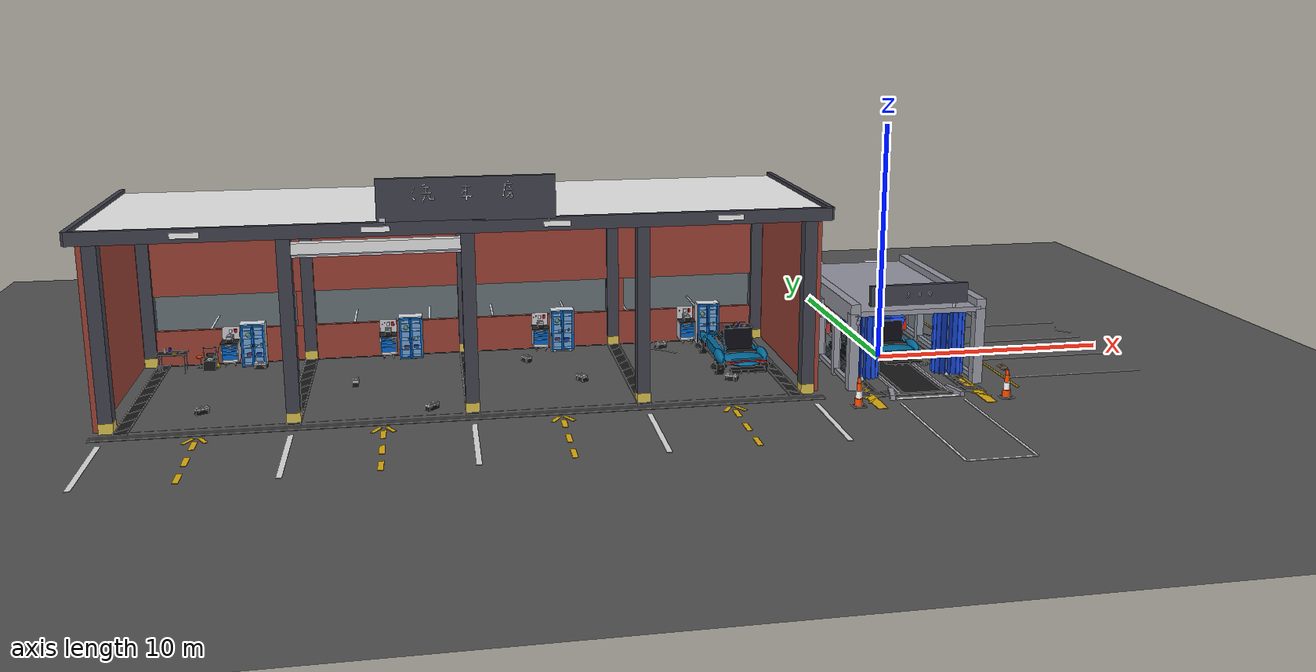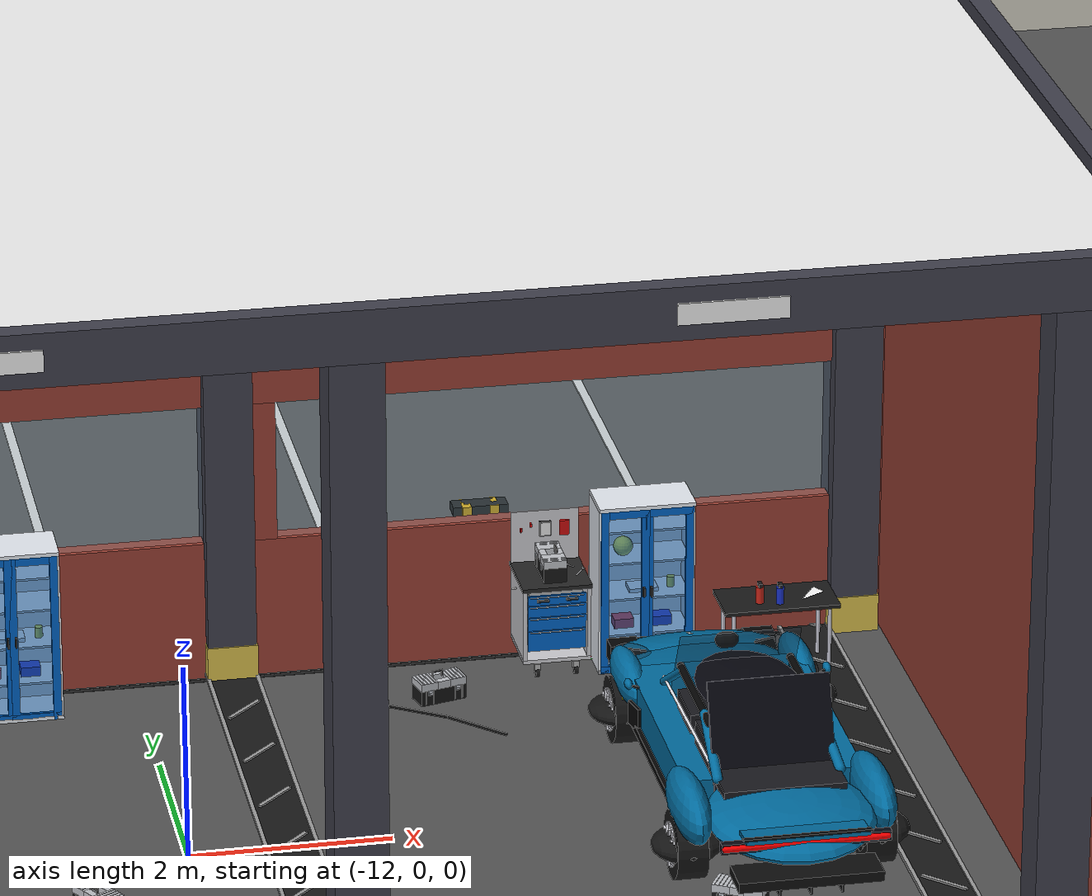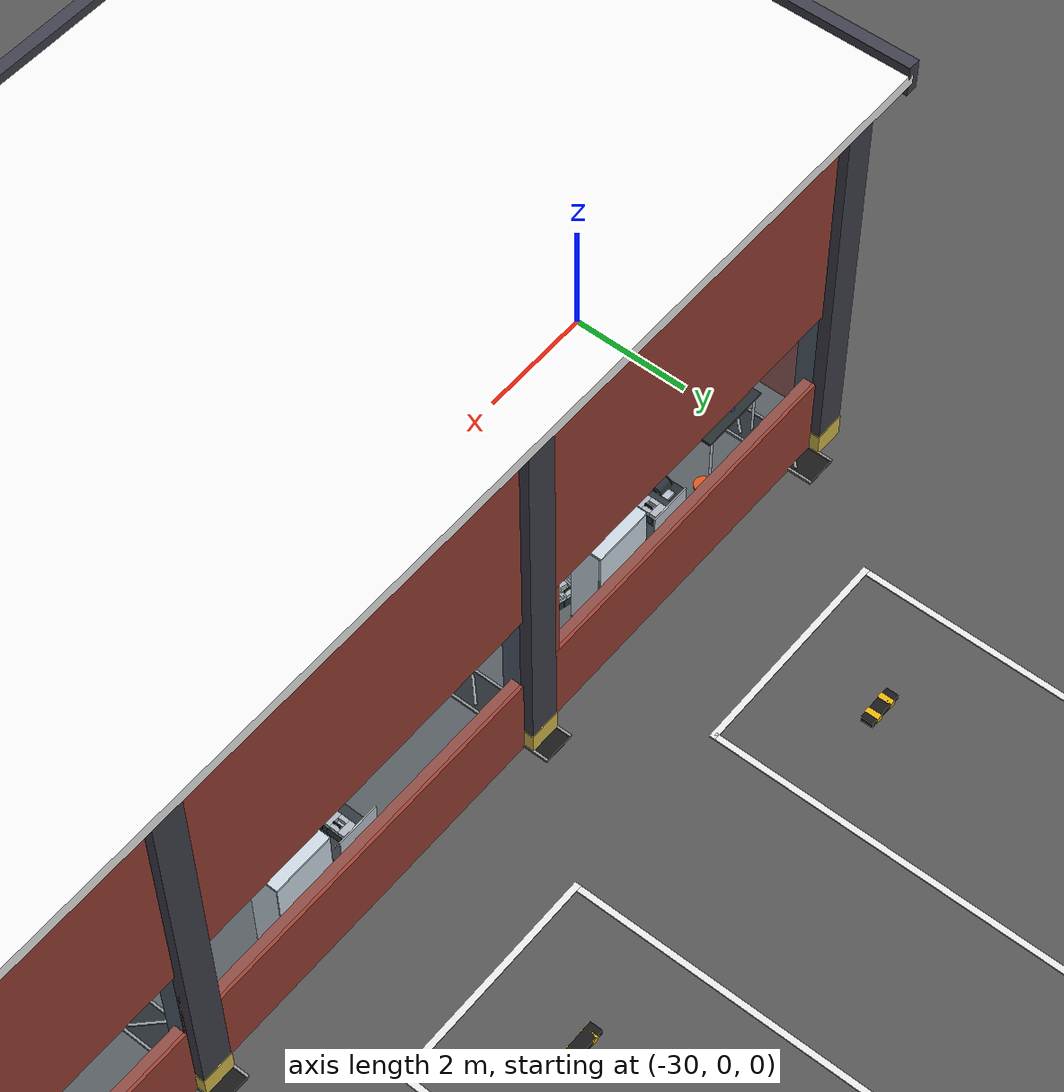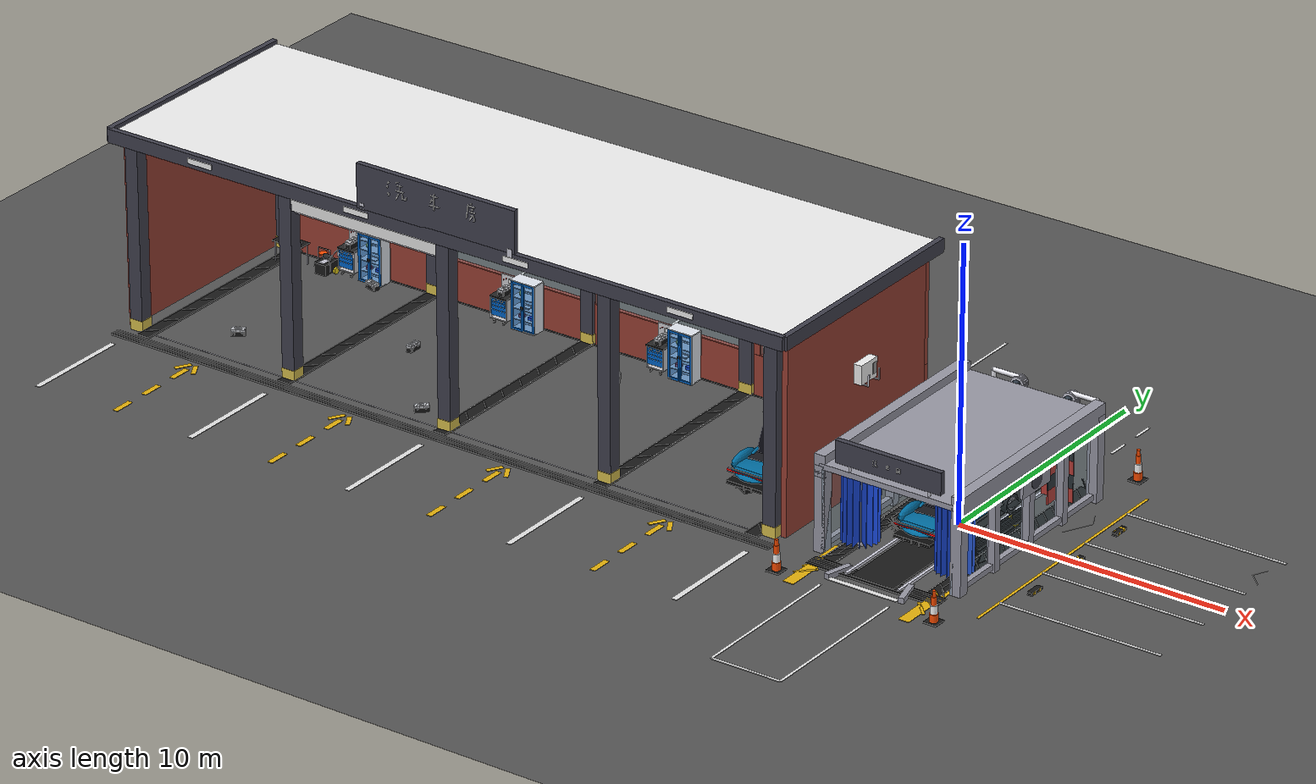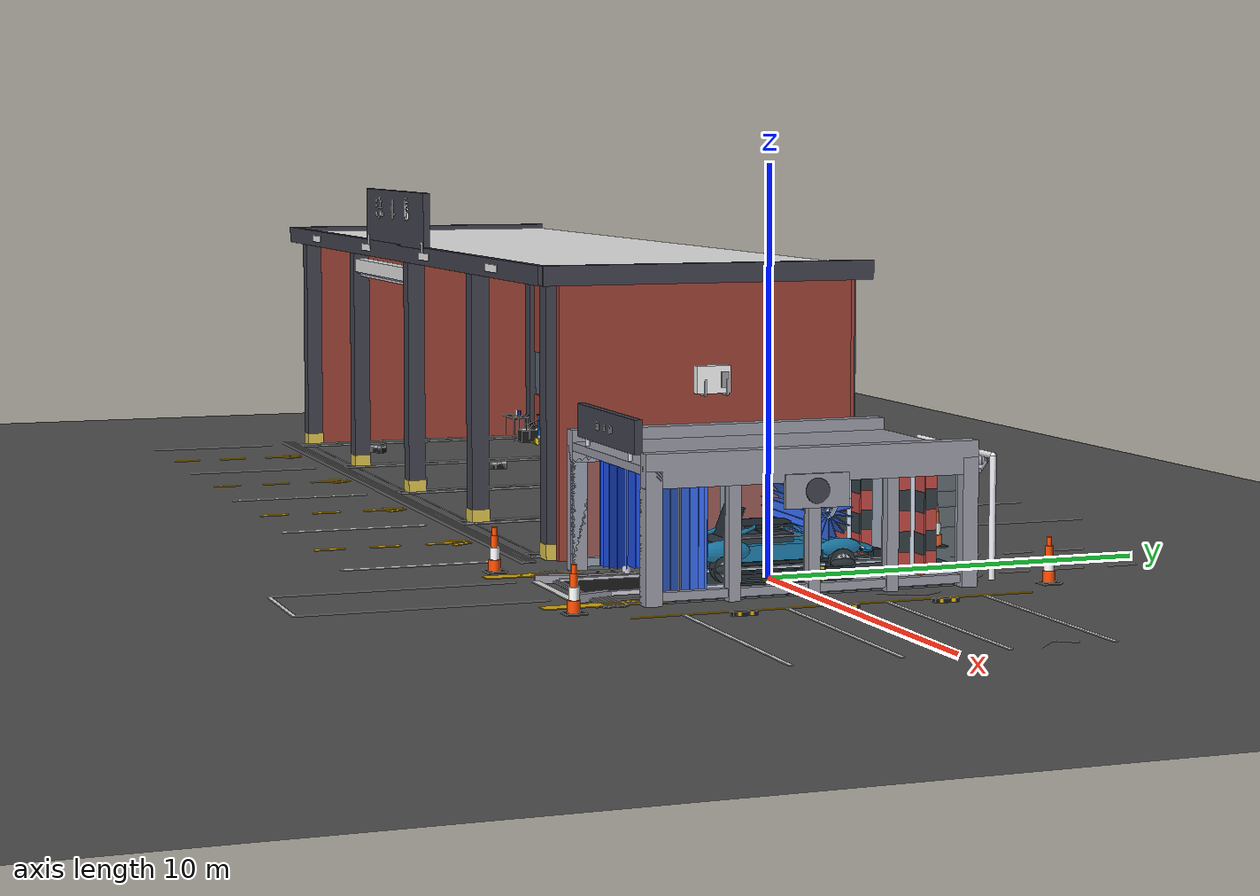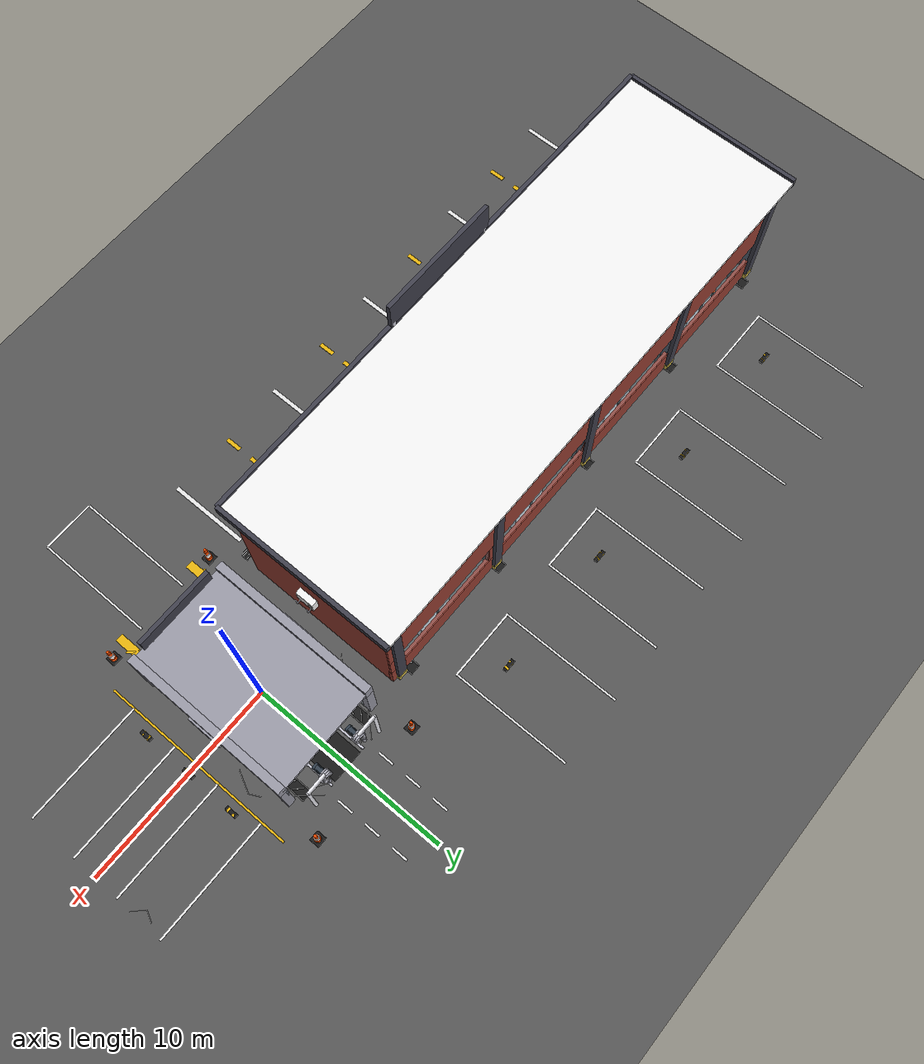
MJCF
<mujoco model="Tunnel Car Wash KSL">
    <compiler angle="degree" coordinate="local" inertiafromgeom="true"/>
    <option timestep="0.01" gravity="0 0 -9.81" density="1.2" viscosity="0.00002" integrator="RK4"/>
    <visual>
        <headlight diffuse="0.6 0.6 0.6" ambient="0.3 0.3 0.3" specular="0 0 0"/>
        <rgba haze="0.15 0.25 0.35 1"/>
        <global azimuth="140" elevation="-20"/>
    </visual>

    <asset>
        <texture type="skybox" builtin="gradient" rgb1="0.3 0.5 0.7" rgb2="0.1 0.1 0.15" width="512" height="3072"/>
        <texture type="2d" name="groundplane" builtin="checker" rgb1="0.35 0.35 0.35" rgb2="0.32 0.32 0.32" width="512" height="512" mark="edge" markrgb="0.3 0.3 0.3"/>
        <material name="groundplane" texture="groundplane" texrepeat="50 50" texuniform="true" reflectance="0.1" shininess="0.2" specular="0.1"/>

        <!-- Updated Colors based on KSL reference (Bright Yellow Tunnel) -->
        <material name="ksl_yellow" rgba="0.6 0.6 0.65 1" shininess="0.5" specular="0.3" reflectance="0.1"/>
        <material name="ksl_logo_red" rgba="0.8 0.1 0.1 1" shininess="0.5" specular="0.3"/>

        <!-- Brush Materials -->
        <material name="brush_red" rgba="0.8 0.15 0.1 1" shininess="0.2" specular="0.1"/>
        <material name="brush_black" rgba="0.1 0.1 0.1 1" shininess="0.3" specular="0.2"/>
        <material name="brush_blue" rgba="0.1 0.2 0.8 1" shininess="0.3" specular="0.2"/>
        <material name="brush_yellow" rgba="0.9 0.8 0.1 1" shininess="0.3" specular="0.2"/>
        <material name="brush_dark_blue" rgba="0.05 0.1 0.3 1" shininess="0.3" specular="0.2"/>
        <material name="brush_mix" rgba="0.5 0.5 0.5 1" shininess="0.2"/>

        <material name="steel" rgba="0.8 0.8 0.85 1" shininess="0.9" specular="1.0" reflectance="0.8"/>
        <material name="black_plastic" rgba="0.05 0.05 0.05 1" shininess="0.2" specular="0.1"/>
        <material name="conveyor_belt" rgba="0.1 0.1 0.1 1" shininess="0.1" roughness="0.8"/>

        <!-- Floor Markings (Worn Paint Look) -->
        <material name="paint_white" rgba="0.9 0.9 0.9 1" shininess="0.1" specular="0" reflectance="0.2"/>
        <material name="paint_yellow" rgba="0.9 0.7 0.05 1" shininess="0.1" specular="0" reflectance="0.2"/>

        <!-- Signboard Materials (Emissive for Neon effect) -->
        <material name="sign_board_blue" rgba="0.25 0.25 0.3 1" shininess="0.8" specular="0.5"/>
        <material name="sign_text_white" rgba="1 1 1 1" shininess="0.5" emission="0.8"/>

        <!-- Glass Material (More transparent and reflective) -->
        <material name="glass" rgba="0.6 0.8 0.9 0.2" shininess="0.9" specular="0.9" reflectance="0.6"/>

        <!-- Metal Grate Material -->
        <material name="metal_grate" rgba="0.6 0.6 0.6 1" shininess="0.6" specular="0.7"/>

        <!-- Rainbow Sign Materials -->
        <material name="rb_red" rgba="0.9 0.1 0.1 1" shininess="0.3"/>
        <material name="rb_orange" rgba="1.0 0.5 0.0 1" shininess="0.3"/>
        <material name="rb_yellow" rgba="1.0 0.9 0.0 1" shininess="0.3"/>
        <material name="rb_green" rgba="0.1 0.8 0.1 1" shininess="0.3"/>
        <material name="rb_blue" rgba="0.1 0.5 1.0 1" shininess="0.3"/>
        <material name="rb_cyan" rgba="0.0 1.0 1.0 1" shininess="0.5" emission="0.3"/>
        <material name="sign_bg_dark" rgba="0.1 0.15 0.2 1" shininess="0.2"/>

        <!-- Dryer Materials -->
        <material name="dryer_white" rgba="0.92 0.92 0.95 1" shininess="0.6" specular="0.6" reflectance="0.1"/>
        <material name="dryer_grill" rgba="0.1 0.1 0.1 1" shininess="0.4"/>
        <material name="cable_black" rgba="0.05 0.05 0.05 1" shininess="0.2" roughness="0.7"/>

        <!-- Traffic Cone Materials -->
        <material name="cone_red" rgba="1.0 0.3 0.0 1" shininess="0.5" emission="0.1"/>
        <material name="cone_white" rgba="1 1 1 1" shininess="0.8" reflectance="0.8" emission="0.2"/> <!-- Reflective tape -->
        <material name="cone_base" rgba="0.1 0.1 0.1 1" shininess="0.1"/>

        <!-- Industrial Blower Materials -->
        <material name="blower_metal" rgba="0.75 0.75 0.8 1" shininess="0.8" specular="0.9" reflectance="0.5"/>
        <material name="blower_motor" rgba="0.2 0.25 0.3 1" shininess="0.6" specular="0.4"/>

        <!-- New Detailed Brush Materials -->
        <material name="brush_yellow_bright" rgba="1.0 0.85 0.0 1" shininess="0.4" specular="0.3"/>
        <material name="brush_blue_bright" rgba="0.1 0.3 0.9 1" shininess="0.4" specular="0.3"/>
        <material name="plastic_white" rgba="0.9 0.9 0.9 1" shininess="0.5"/>
        <texture name="camry_tex_paint" type="cube" builtin="flat" rgb1="0.9 0.9 0.95" width="100" height="100"/>
        <material name="camry_paint_silver" texture="camry_tex_paint" reflectance="0.6" shininess="0.9" rgba="0.92 0.92 0.95 1"/>
        <material name="camry_paint_blue" texture="camry_tex_paint" reflectance="0.6" shininess="0.9" rgba="0.05 0.2 0.8 1"/>
        <material name="camry_glass" reflectance="0.5" shininess="0.9" rgba="0.1 0.15 0.2 0.7"/>
        <material name="camry_rubber" reflectance="0.1" roughness="0.8" rgba="0.1 0.1 0.1 1"/>
        <material name="camry_chrome" reflectance="0.9" shininess="1.0" rgba="0.9 0.9 0.9 1"/>
        <material name="camry_rim_alloy" reflectance="0.7" shininess="0.8" rgba="0.7 0.7 0.75 1"/>
        <material name="camry_light_front" emission="15" rgba="0.9 0.9 1 1"/>
        <material name="camry_light_rear" emission="8" rgba="0.9 0 0 1"/>
        <material name="camry_grille_mat" reflectance="0.3" rgba="0.05 0.05 0.05 1"/>

        <material name="shutter_metal" rgba="0.7 0.75 0.8 1" shininess="0.5" specular="0.6" reflectance="0.4"/>
        <material name="shutter_box_paint" rgba="0.9 0.9 0.9 1" shininess="0.4"/>

        <!-- Manual Wash Bay Materials -->
        <material name="carshome_blue" rgba="0.25 0.25 0.3 1" shininess="0.6" specular="0.4"/>
        <material name="carshome_white" rgba="0.95 0.95 0.95 1" shininess="0.4" specular="0.2"/>
        <material name="floor_tile_blue" rgba="0.2 0.4 0.9 1" shininess="0.8" reflectance="0.3"/>
        <material name="floor_tile_yellow" rgba="1.0 0.8 0.1 1" shininess="0.5"/>
        <material name="gold_trim" rgba="0.85 0.75 0.3 1" shininess="0.9" specular="0.9" reflectance="0.7"/>

        <!-- Cable Materials -->
        <material name="cable_rubber_black" rgba="0.15 0.15 0.15 1" shininess="0.2" specular="0.1" roughness="0.6"/>
        <material name="pipe_pvc_grey" rgba="0.7 0.7 0.75 1" shininess="0.4" specular="0.3"/>
        <material name="cable_yellow_warning" rgba="0.9 0.8 0.1 1" shininess="0.3"/>
        <material name="cable_clip_metal" rgba="0.6 0.6 0.65 1" shininess="0.7" specular="0.6"/>
        <material name="cable_protector_yellow" rgba="0.9 0.7 0.1 1" shininess="0.3" roughness="0.5"/>
        <material name="cable_protector_black" rgba="0.1 0.1 0.1 1" shininess="0.3" roughness="0.5"/>

        <!-- Brick Wall Material (Style 2) - Procedural Fallback -->
        <material name="mat_brick" rgba="0.6 0.25 0.2 1" reflectance="0.05" shininess="0.1" specular="0.05" roughness="0.95"/>

        <!-- Tool Cabinet Materials -->
        <material name="silver_metal" rgba="0.9 0.92 0.95 1" shininess="0.9" specular="1.0" reflectance="0.7"/>
        <material name="door_blue" rgba="0.0 0.392 0.784 1" shininess="0.6" specular="0.7" reflectance="0.3"/>
        <material name="glass_blue" rgba="0.0 0.392 0.784 0.5" shininess="0.9" specular="0.9" reflectance="0.4"/>
        <material name="tool_red" rgba="0.8 0.2 0.2 1"/>
        <material name="tool_blue" rgba="0.2 0.2 0.8 1"/>
        <material name="tool_yellow" rgba="0.8 0.8 0.2 1"/>
        <material name="handle_metal" rgba="0.2 0.2 0.2 1" shininess="0.5"/>
        <material name="mat_silver_body" rgba="0.8 0.8 0.82 1" shininess="0.6" specular="0.7" reflectance="0.5"/>
        <material name="mat_silver_bright" rgba="0.9 0.9 0.92 1" shininess="0.95" specular="1.0" reflectance="0.9"/>
        <material name="mat_handle_black" rgba="0.05 0.05 0.05 1" shininess="0.1" specular="0.1" reflectance="0.05"/>
        <material name="mat_top_surface" rgba="0.15 0.15 0.15 1" shininess="0.1" specular="0.1" reflectance="0.0"/>
        <material name="mat_red_tool" rgba="0.8 0.05 0.05 1" shininess="0.6" specular="0.4" reflectance="0.1"/>
        <material name="mat_chrome" rgba="0.98 0.98 0.99 1" shininess="1.0" specular="1.0" reflectance="0.98"/>
        <material name="mat_tb_silver" rgba="0.75 0.76 0.78 1" specular="0.9" shininess="0.7" reflectance="0.7"/>
        <material name="mat_tb_latch" rgba="0.8 0.82 0.85 1" specular="1.0" shininess="0.9" reflectance="0.8"/>
        <material name="mat_tb_body" rgba="0.08 0.08 0.08 1" specular="0.3" shininess="0.1" reflectance="0.05"/>
        <material name="mat_tb_handle" rgba="0.05 0.05 0.05 1" specular="0.7" shininess="0.8" reflectance="0.3"/>
        <material name="mat_tb_text" rgba="0.8 0.1 0.1 1" specular="0.5" shininess="0.5" emission="0.2"/>
        <material name="mat_wheel_rubber" rgba="0.1 0.1 0.1 1" shininess="0.3" specular="0.2"/>
        <material name="mat_wheel_metal" rgba="0.7 0.7 0.7 1" shininess="0.9" specular="0.9"/>
        <material name="mat_towel" rgba="0.9 0.9 0.8 1" shininess="0.1" specular="0.0" reflectance="0.0"/>

        <!-- Toolbox Portable Materials -->
        <material name="mat_silver_metal" rgba="0.75 0.76 0.78 1" specular="0.9" shininess="0.7" reflectance="0.7"/>
        <material name="mat_metal_latch" rgba="0.8 0.82 0.85 1" specular="1.0" shininess="0.9" reflectance="0.8"/>
        <material name="mat_black_body" rgba="0.08 0.08 0.08 1" specular="0.3" shininess="0.1" reflectance="0.05"/>
        <material name="mat_red_text" rgba="0.8 0.1 0.1 1" specular="0.5" shininess="0.5" emission="0.2"/>
        <material name="mat_rag" rgba="0.8 0.6 0.2 1" specular="0.05" shininess="0.1" reflectance="0.0"/>
        <material name="mat_drawer_blue" rgba="0 0.392 0.784 1" shininess="0.7" specular="0.5"/>

    <!-- Xiaomi SU7 Materials -->
    <material name="body_paint" rgba="0.0 0.42 0.62 1" shininess="0.95" specular="0.85" reflectance="0.3"/>
    <material name="black_trim" rgba="0.05 0.05 0.05 1" shininess="0.3" specular="0.3"/>
    <material name="black_gloss" rgba="0.01 0.01 0.01 1" shininess="0.95" specular="1.0" reflectance="0.3"/>
    <material name="chrome" rgba="0.9 0.9 0.92 1" shininess="1.0" specular="1.0" reflectance="0.8"/>
    <material name="interior_dark" rgba="0.1 0.1 0.12 1" shininess="0.1"/>
    <material name="glass_front" rgba="0.1 0.15 0.2 0.3" shininess="1.0" specular="1.0" reflectance="0.4"/>
    <material name="glass_dark" rgba="0.02 0.02 0.05 0.9" shininess="1.0" specular="1.0" reflectance="0.7"/>
    <material name="rim_silver" rgba="0.85 0.85 0.88 1" shininess="0.9" specular="0.9"/>
    <material name="rim_black" rgba="0.05 0.05 0.05 1" shininess="0.6"/>
    <material name="tire_rubber" rgba="0.08 0.08 0.08 1" shininess="0.1" specular="0.1" reflectance="0.02"/>
    <material name="tire_sidewall" rgba="0.08 0.08 0.08 1" shininess="0.3" specular="0.2" reflectance="0.05"/>
    <material name="light_white" rgba="0.95 0.95 1.0 1" emission="1.0"/>
    <material name="light_red" rgba="1.0 0.0 0.0 1" emission="0.8"/>
    <material name="caliper_yellow" rgba="1.0 0.85 0.0 1" shininess="0.9"/>
    <material name="logo_silver" rgba="0.95 0.95 0.95 1" shininess="1.0" specular="1.0"/>

    </asset>

    <worldbody>
        <!-- Main Sun Light (Casting shadows) -->
        <light pos="8 -8 15" dir="-0.5 0.5 -1" castshadow="true" diffuse="0.8 0.8 0.8" specular="0.3 0.3 0.3"/>
        <!-- Fill Light (Softer, blue-ish tint for sky) -->
        <light pos="-8 8 10" dir="0.5 -0.5 -1" castshadow="false" diffuse="0.4 0.4 0.5" specular="0.1 0.1 0.1"/>
        <!-- Interior Point Light (Warm tone for wash bay) -->
        <light pos="0 0 6" dir="0 0 -1" castshadow="false" diffuse="0.5 0.4 0.3" attenuation="1 0 0.1"/>

        <geom name="floor" size="0 0 0.1" type="plane" material="groundplane"/>

        <!-- ==================== FLOOR MARKINGS ==================== -->
        <body name="floor_markings" pos="0 0 0.02">
            <!-- DRAINAGE GRATES -->
            <!-- Front Entrance Drain (Transverse) -->
            <geom name="drain_front_frame" type="box" size="2.5 0.3 0.02" pos="0 -4.8 -0.01" material="brush_black"/> <!-- Dark pit background -->
            <!-- Grate bars (Front) -->
            <geom type="box" size="2.5 0.02 0.02" pos="0 -4.6 0" material="metal_grate"/>
            <geom type="box" size="2.5 0.02 0.02" pos="0 -4.7 0" material="metal_grate"/>
            <geom type="box" size="2.5 0.02 0.02" pos="0 -4.8 0" material="metal_grate"/>
            <geom type="box" size="2.5 0.02 0.02" pos="0 -4.9 0" material="metal_grate"/>
            <geom type="box" size="2.5 0.02 0.02" pos="0 -5.0 0" material="metal_grate"/>

            <!-- Left Side Drain (Longitudinal) -->
            <geom name="drain_side_L_frame" type="box" size="0.25 4.5 0.02" pos="-2.0 0 -0.01" material="brush_black"/>
            <!-- Grate bars (Left) - angled for style -->
            <geom type="box" size="0.25 0.02 0.02" pos="-2.0 -4.0 0" euler="0 0 45" material="metal_grate"/>
            <geom type="box" size="0.25 0.02 0.02" pos="-2.0 -3.5 0" euler="0 0 45" material="metal_grate"/>
            <geom type="box" size="0.25 0.02 0.02" pos="-2.0 -3.0 0" euler="0 0 45" material="metal_grate"/>
            <geom type="box" size="0.25 0.02 0.02" pos="-2.0 -2.5 0" euler="0 0 45" material="metal_grate"/>
            <geom type="box" size="0.25 0.02 0.02" pos="-2.0 -2.0 0" euler="0 0 45" material="metal_grate"/>
            <geom type="box" size="0.25 0.02 0.02" pos="-2.0 -1.5 0" euler="0 0 45" material="metal_grate"/>
            <geom type="box" size="0.25 0.02 0.02" pos="-2.0 -1.0 0" euler="0 0 45" material="metal_grate"/>
            <geom type="box" size="0.25 0.02 0.02" pos="-2.0 -0.5 0" euler="0 0 45" material="metal_grate"/>
            <geom type="box" size="0.25 0.02 0.02" pos="-2.0 0.0 0" euler="0 0 45" material="metal_grate"/>
            <geom type="box" size="0.25 0.02 0.02" pos="-2.0 0.5 0" euler="0 0 45" material="metal_grate"/>
            <geom type="box" size="0.25 0.02 0.02" pos="-2.0 1.0 0" euler="0 0 45" material="metal_grate"/>
            <geom type="box" size="0.25 0.02 0.02" pos="-2.0 1.5 0" euler="0 0 45" material="metal_grate"/>
            <geom type="box" size="0.25 0.02 0.02" pos="-2.0 2.0 0" euler="0 0 45" material="metal_grate"/>
            <geom type="box" size="0.25 0.02 0.02" pos="-2.0 2.5 0" euler="0 0 45" material="metal_grate"/>
            <geom type="box" size="0.25 0.02 0.02" pos="-2.0 3.0 0" euler="0 0 45" material="metal_grate"/>
            <geom type="box" size="0.25 0.02 0.02" pos="-2.0 3.5 0" euler="0 0 45" material="metal_grate"/>
            <geom type="box" size="0.25 0.02 0.02" pos="-2.0 4.0 0" euler="0 0 45" material="metal_grate"/>
            <!-- Side rails for drain -->
            <geom type="box" size="0.02 4.5 0.02" pos="-1.75 0 0" material="metal_grate"/>
            <geom type="box" size="0.02 4.5 0.02" pos="-2.25 0 0" material="metal_grate"/>

            <!-- Right Side Drain (Longitudinal) -->
            <geom name="drain_side_R_frame" type="box" size="0.25 4.5 0.02" pos="2.0 0 -0.01" material="brush_black"/>
            <!-- Grate bars (Right) -->
            <geom type="box" size="0.25 0.02 0.02" pos="2.0 -4.0 0" euler="0 0 -45" material="metal_grate"/>
            <geom type="box" size="0.25 0.02 0.02" pos="2.0 -3.5 0" euler="0 0 -45" material="metal_grate"/>
            <geom type="box" size="0.25 0.02 0.02" pos="2.0 -3.0 0" euler="0 0 -45" material="metal_grate"/>
            <geom type="box" size="0.25 0.02 0.02" pos="2.0 -2.5 0" euler="0 0 -45" material="metal_grate"/>
            <geom type="box" size="0.25 0.02 0.02" pos="2.0 -2.0 0" euler="0 0 -45" material="metal_grate"/>
            <geom type="box" size="0.25 0.02 0.02" pos="2.0 -1.5 0" euler="0 0 -45" material="metal_grate"/>
            <geom type="box" size="0.25 0.02 0.02" pos="2.0 -1.0 0" euler="0 0 -45" material="metal_grate"/>
            <geom type="box" size="0.25 0.02 0.02" pos="2.0 -0.5 0" euler="0 0 -45" material="metal_grate"/>
            <geom type="box" size="0.25 0.02 0.02" pos="2.0 0.0 0" euler="0 0 -45" material="metal_grate"/>
            <geom type="box" size="0.25 0.02 0.02" pos="2.0 0.5 0" euler="0 0 -45" material="metal_grate"/>
            <geom type="box" size="0.25 0.02 0.02" pos="2.0 1.0 0" euler="0 0 -45" material="metal_grate"/>
            <geom type="box" size="0.25 0.02 0.02" pos="2.0 1.5 0" euler="0 0 -45" material="metal_grate"/>
            <geom type="box" size="0.25 0.02 0.02" pos="2.0 2.0 0" euler="0 0 -45" material="metal_grate"/>
            <geom type="box" size="0.25 0.02 0.02" pos="2.0 2.5 0" euler="0 0 -45" material="metal_grate"/>
            <geom type="box" size="0.25 0.02 0.02" pos="2.0 3.0 0" euler="0 0 -45" material="metal_grate"/>
            <geom type="box" size="0.25 0.02 0.02" pos="2.0 3.5 0" euler="0 0 -45" material="metal_grate"/>
            <geom type="box" size="0.25 0.02 0.02" pos="2.0 4.0 0" euler="0 0 -45" material="metal_grate"/>
            <!-- Side rails for drain -->
            <geom type="box" size="0.02 4.5 0.02" pos="1.75 0 0" material="metal_grate"/>
            <geom type="box" size="0.02 4.5 0.02" pos="2.25 0 0" material="metal_grate"/>

            <!-- Parking/Queue Lane (White) -->
            <!-- Left Lane Line (Longitudinal) -->
            <geom name="line_lane_L" type="box" size="0.05 3 0.01" pos="-1.3 -9 0" material="paint_white"/>
            <!-- Right Lane Line (Longitudinal) -->
            <geom name="line_lane_R" type="box" size="0.05 3 0.01" pos="1.3 -9 0" material="paint_white"/>
            <!-- Stop Line (Transverse) -->
            <geom name="line_stop" type="box" size="1.3 0.1 0.01" pos="0 -5.5 0" material="paint_white"/>
            <!-- Back Parking Box Line -->
            <geom name="line_park_back" type="box" size="1.3 0.05 0.01" pos="0 -12 0" material="paint_white"/>

            <!-- Safety Zones (Yellow) - Near Entrance -->
            <!-- Left Safety Strip -->
            <geom name="safety_L" type="box" size="0.2 1.5 0.01" pos="-2.2 -5.0 0" material="paint_yellow"/>
            <!-- Right Safety Strip -->
            <geom name="safety_R" type="box" size="0.2 1.5 0.01" pos="2.2 -5.0 0" material="paint_yellow"/>

            <!-- Diagonal Hazard Stripes -->
            <geom name="hatch_L1" type="box" size="0.4 0.05 0.01" pos="-2.2 -5.5 0" euler="0 0 45" material="paint_yellow"/>
            <geom name="hatch_L2" type="box" size="0.4 0.05 0.01" pos="-2.2 -5.0 0" euler="0 0 45" material="paint_yellow"/>
            <geom name="hatch_L3" type="box" size="0.4 0.05 0.01" pos="-2.2 -4.5 0" euler="0 0 45" material="paint_yellow"/>

            <geom name="hatch_R1" type="box" size="0.4 0.05 0.01" pos="2.2 -5.5 0" euler="0 0 -45" material="paint_yellow"/>
            <geom name="hatch_R2" type="box" size="0.4 0.05 0.01" pos="2.2 -5.0 0" euler="0 0 -45" material="paint_yellow"/>
            <geom name="hatch_R3" type="box" size="0.4 0.05 0.01" pos="2.2 -4.5 0" euler="0 0 -45" material="paint_yellow"/>

            <!-- PARKING SPACES (Right Side) -->
            <!-- Yellow Lane Line -->
            <geom name="park_lane_line" type="box" size="0.05 5.0 0.01" pos="4.0 0 0" material="paint_yellow"/>

            <!-- Spot 1 (Top) -->
            <geom name="park_line_1" type="box" size="3.0 0.05 0.01" pos="7.0 3.75 0" material="paint_white"/>
            <geom name="park_line_2" type="box" size="3.0 0.05 0.01" pos="7.0 1.25 0" material="paint_white"/>
            <geom name="stopper_1_base" type="box" size="0.1 0.3 0.05" pos="4.5 2.5 0.05" material="brush_black"/>
            <geom name="stopper_1_y1" type="box" size="0.11 0.05 0.05" pos="4.5 2.35 0.05" material="paint_yellow"/>
            <geom name="stopper_1_y2" type="box" size="0.11 0.05 0.05" pos="4.5 2.65 0.05" material="paint_yellow"/>

            <!-- Spot 2 (Middle) -->
            <geom name="park_line_3" type="box" size="3.0 0.05 0.01" pos="7.0 -1.25 0" material="paint_white"/>
            <geom name="stopper_2_base" type="box" size="0.1 0.3 0.05" pos="4.5 0.0 0.05" material="brush_black"/>
            <geom name="stopper_2_y1" type="box" size="0.11 0.05 0.05" pos="4.5 -0.15 0.05" material="paint_yellow"/>
            <geom name="stopper_2_y2" type="box" size="0.11 0.05 0.05" pos="4.5 0.15 0.05" material="paint_yellow"/>

            <!-- Spot 3 (Bottom) -->
            <geom name="park_line_4" type="box" size="3.0 0.05 0.01" pos="7.0 -3.75 0" material="paint_white"/>
            <geom name="stopper_3_base" type="box" size="0.1 0.3 0.05" pos="4.5 -2.5 0.05" material="brush_black"/>
            <geom name="stopper_3_y1" type="box" size="0.11 0.05 0.05" pos="4.5 -2.65 0.05" material="paint_yellow"/>
            <geom name="stopper_3_y2" type="box" size="0.11 0.05 0.05" pos="4.5 -2.35 0.05" material="paint_yellow"/>

            <!-- Exit Guide Lines (Dashed White) -->
            <geom name="guide_L1" type="box" size="0.05 0.4 0.01" pos="-1.3 6.0 0" material="paint_white"/>
            <geom name="guide_L2" type="box" size="0.05 0.4 0.01" pos="-1.3 7.5 0" material="paint_white"/>
            <geom name="guide_L3" type="box" size="0.05 0.4 0.01" pos="-1.3 9.0 0" material="paint_white"/>

            <geom name="guide_R1" type="box" size="0.05 0.4 0.01" pos="1.3 6.0 0" material="paint_white"/>
            <geom name="guide_R2" type="box" size="0.05 0.4 0.01" pos="1.3 7.5 0" material="paint_white"/>
            <geom name="guide_R3" type="box" size="0.05 0.4 0.01" pos="1.3 9.0 0" material="paint_white"/>
        </body>

        <!-- CAMRY REMOVED -->

        <!-- ==================== TUNNEL STRUCTURE ==================== -->
        <!-- The tunnel is longer now, approximately 8 meters long (y: -4 to 4) -->
        <body name="tunnel_frame" pos="0 0 0">
            <!-- ROOF -->
            <geom name="roof_plate" type="box" size="2.6 4.2 0.1" pos="0 0 3.1" material="ksl_yellow"/>
            <geom name="roof_side_L" type="box" size="0.2 4.2 0.4" pos="-2.6 0 3.1" material="ksl_yellow"/>
            <geom name="roof_side_R" type="box" size="0.2 4.2 0.4" pos="2.6 0 3.1" material="ksl_yellow"/>

            <!-- ================= MANUAL WASH BAY (Left Side - Expanded 4 Bays) ================= -->
            <!-- Position: Shifted further left to accommodate double width (Width ~14m) -->
            <!-- Center at -11.0 ensures right edge is at ~ -4.0, similar to before -->
            <body name="manual_wash_bay" pos="-17.5 0 0">

                <!-- 1. FLOORING -->
                <!-- Main Floor Base removed to expose original ground -->

                <!-- Yellow Bay Frames REMOVED -->
                <!-- Double Bay 1 (Right Side) -->
                <!-- Inner Grid Pattern Bay 1 -->

                <!-- Double Bay 2 (Left Side) -->
                <!-- Inner Grid Pattern Bay 2 -->

                <!-- 2. STRUCTURE COLUMNS (5 Pairs - Height 7.2m) -->
                <!-- Front Pillars -->
                <geom name="col_F_1" type="box" size="0.25 0.25 3.6" pos="-13.0 -4.0 3.6" material="carshome_blue"/>
                <geom name="col_F_2" type="box" size="0.25 0.25 3.6" pos="-6.5 -4.0 3.6" material="carshome_blue"/>
                <geom name="col_F_3" type="box" size="0.25 0.25 3.6" pos="0 -4.0 3.6" material="carshome_blue"/>
                <geom name="col_F_4" type="box" size="0.25 0.25 3.6" pos="6.5 -4.0 3.6" material="carshome_blue"/>
                <geom name="col_F_5" type="box" size="0.25 0.25 3.6" pos="13.0 -4.0 3.6" material="carshome_blue"/>

                <!-- Gold Trim Front -->
                <geom name="trim_F_1" type="box" size="0.26 0.26 0.2" pos="-13.0 -4.0 0.2" material="gold_trim"/>
                <geom name="trim_F_2" type="box" size="0.26 0.26 0.2" pos="-6.5 -4.0 0.2" material="gold_trim"/>
                <geom name="trim_F_3" type="box" size="0.26 0.26 0.2" pos="0 -4.0 0.2" material="gold_trim"/>
                <geom name="trim_F_4" type="box" size="0.26 0.26 0.2" pos="6.5 -4.0 0.2" material="gold_trim"/>
                <geom name="trim_F_5" type="box" size="0.26 0.26 0.2" pos="13.0 -4.0 0.2" material="gold_trim"/>

                <!-- Back Pillars -->
                <geom name="col_B_1" type="box" size="0.25 0.25 3.6" pos="-13.0 4.0 3.6" material="carshome_blue"/>
                <geom name="col_B_2" type="box" size="0.25 0.25 3.6" pos="-6.5 4.0 3.6" material="carshome_blue"/>
                <geom name="col_B_3" type="box" size="0.25 0.25 3.6" pos="0 4.0 3.6" material="carshome_blue"/>
                <geom name="col_B_4" type="box" size="0.25 0.25 3.6" pos="6.5 4.0 3.6" material="carshome_blue"/>
                <geom name="col_B_5" type="box" size="0.25 0.25 3.6" pos="13.0 4.0 3.6" material="carshome_blue"/>

                <geom name="trim_B_1" type="box" size="0.26 0.26 0.2" pos="-13.0 4.0 0.2" material="gold_trim"/>
                <geom name="trim_B_2" type="box" size="0.26 0.26 0.2" pos="-6.5 4.0 0.2" material="gold_trim"/>
                <geom name="trim_B_3" type="box" size="0.26 0.26 0.2" pos="0 4.0 0.2" material="gold_trim"/>
                <geom name="trim_B_4" type="box" size="0.26 0.26 0.2" pos="6.5 4.0 0.2" material="gold_trim"/>
                <geom name="trim_B_5" type="box" size="0.26 0.26 0.2" pos="13.0 4.0 0.2" material="gold_trim"/>

                <!-- 3. WALLS (Interior White - Height Increased to 7.2m) -->
                <!-- Back Wall split into sections to allow for windows -->
                <!-- Windows will be placed at height 1.5m to 3.0m -->
                <!-- Lower Wall (0 to 1.5m) -->
                <geom name="bay_wall_back_low" type="box" size="13.5 0.1 0.75" pos="0 4.0 0.75" material="mat_brick"/>
                <!-- Upper Wall (3.0m to 7.2m) -->
                <geom name="bay_wall_back_high" type="box" size="13.5 0.1 2.1" pos="0 4.0 5.1" material="mat_brick"/>

                <!-- Vertical Columns between windows (at -13.5, -6.75, 0, 6.75, 13.5) -->
                <geom name="bay_wall_col_1" type="box" size="0.25 0.1 0.75" pos="-13.25 4.0 2.25" material="mat_brick"/>
                <geom name="bay_wall_col_2" type="box" size="0.25 0.1 0.75" pos="-6.75 4.0 2.25" material="mat_brick"/>
                <geom name="bay_wall_col_3" type="box" size="0.25 0.1 0.75" pos="0 4.0 2.25" material="mat_brick"/>
                <geom name="bay_wall_col_4" type="box" size="0.25 0.1 0.75" pos="6.75 4.0 2.25" material="mat_brick"/>
                <geom name="bay_wall_col_5" type="box" size="0.25 0.1 0.75" pos="13.25 4.0 2.25" material="mat_brick"/>

                <!-- Windows (Glass) -->
                <!-- Window 1 (Leftmost) -->
                <geom name="window_1" type="box" size="3.125 0.05 0.75" pos="-10.0 4.0 2.25" material="glass"/>
                <!-- Window 2 (Left-Center) -->
                <geom name="window_2" type="box" size="3.125 0.05 0.75" pos="-3.375 4.0 2.25" material="glass"/>
                <!-- Window 3 (Right-Center) -->
                <geom name="window_3" type="box" size="3.125 0.05 0.75" pos="3.375 4.0 2.25" material="glass"/>
                <!-- Window 4 (Rightmost) -->
                <geom name="window_4" type="box" size="3.125 0.05 0.75" pos="10.0 4.0 2.25" material="glass"/>

                <geom name="bay_wall_L" type="box" size="0.1 4.0 3.6" pos="-13.4 0 3.6" material="mat_brick"/>
                <geom name="bay_wall_R" type="box" size="0.1 4.0 3.6" pos="13.4 0 3.6" material="mat_brick"/>

                <!-- 4. ROOF (Raised to 7.2m) -->
                <geom name="bay_roof" type="box" size="13.7 4.5 0.1" pos="0 0 7.2" material="carshome_white"/>
                <!-- Fascia -->
                <geom name="bay_fascia_F" type="box" size="13.7 0.1 0.25" pos="0 -4.5 7.2" material="carshome_blue"/>
                <geom name="bay_fascia_L" type="box" size="0.1 4.5 0.25" pos="-13.7 0 7.2" material="carshome_blue"/>
                <geom name="bay_fascia_R" type="box" size="0.1 4.5 0.25" pos="13.7 0 7.2" material="carshome_blue"/>

                <!-- Simulated Text "Carshome" - Distributed -->
                <geom name="logo_text_1" type="box" size="0.5 0.02 0.1" pos="-9.75 -4.6 7.2" material="carshome_white"/>
                <geom name="logo_text_2" type="box" size="0.5 0.02 0.1" pos="-3.25 -4.6 7.2" material="carshome_white"/>
                <geom name="logo_text_3" type="box" size="0.5 0.02 0.1" pos="3.25 -4.6 7.2" material="carshome_white"/>
                <geom name="logo_text_4" type="box" size="0.5 0.02 0.1" pos="9.75 -4.6 7.2" material="carshome_white"/>

                <!-- DOORS REMOVED -->

                <!-- ROLLED UP SHUTTER DOOR (Added to Bay 2) -->
                <body name="roller_shutter_bay2" pos="-3.25 -4.0 6.5">
                    <!-- 1. Shutter Housing Box (Top) -->
                    <geom name="shutter_box" type="box" size="3.1 0.2 0.2" pos="0 0 0" material="shutter_box_paint"/>

                    <!-- 2. Rolled Door (Cylinder visible inside/below) -->
                    <geom name="shutter_roll" type="cylinder" size="0.18 3.0" pos="0 0 -0.1" euler="0 90 0" material="shutter_metal"/>

                    <!-- 3. Bottom Bar (Hanging slightly) -->
                    <geom name="shutter_bar" type="box" size="3.0 0.02 0.05" pos="0 0 -0.3" material="steel"/>

                    <!-- 4. Side Tracks (Guide Rails running down) -->
                    <!-- Left Track (on pillar col_F_2 side) -->
                    <!-- Height is ~6.5m from ground to box -->
                    <geom name="shutter_track_L" type="box" size="0.05 0.05 3.25" pos="-3.1 0 -3.25" material="shutter_metal"/>
                    <!-- Right Track (on pillar col_F_3 side) -->
                    <geom name="shutter_track_R" type="box" size="0.05 0.05 3.25" pos="3.1 0 -3.25" material="shutter_metal"/>

                    <!-- Motor Box (Side) -->
                    <geom name="shutter_motor" type="box" size="0.15 0.15 0.15" pos="3.3 0 0" material="brush_black"/>
                    <!-- Manual Chain (Hanging) -->
                    <geom name="shutter_chain" type="capsule" fromto="3.3 0 0 3.3 0 -1.5" size="0.01" material="steel"/>
                </body>

                <!-- 5. DRAINAGE CHANNEL -->
                <!-- Front Drain (Detailed) -->
                <geom name="bay_drain_frame" type="box" size="13.5 0.2 0.02" pos="0 -4.8 0.02" material="brush_black"/>
                <!-- Grate bars (Parallel) - Stretched -->
                <geom type="box" size="13.5 0.02 0.02" pos="0 -4.65 0.04" material="metal_grate"/>
                <geom type="box" size="13.5 0.02 0.02" pos="0 -4.72 0.04" material="metal_grate"/>
                <geom type="box" size="13.5 0.02 0.02" pos="0 -4.80 0.04" material="metal_grate"/>
                <geom type="box" size="13.5 0.02 0.02" pos="0 -4.87 0.04" material="metal_grate"/>
                <geom type="box" size="13.5 0.02 0.02" pos="0 -4.95 0.04" material="metal_grate"/>

                <!-- Side Drains (Left & Right) -->
                <!-- Left Side Drain -->
                <geom name="bay_drain_L_frame" type="box" size="0.25 4.5 0.02" pos="-12.5 0 0.02" material="brush_black"/>
                <!-- Grate Bars Left -->
                <geom type="box" size="0.25 0.02 0.02" pos="-12.5 -4.0 0.04" euler="0 0 45" material="metal_grate"/>
                <geom type="box" size="0.25 0.02 0.02" pos="-12.5 -3.0 0.04" euler="0 0 45" material="metal_grate"/>
                <geom type="box" size="0.25 0.02 0.02" pos="-12.5 -2.0 0.04" euler="0 0 45" material="metal_grate"/>
                <geom type="box" size="0.25 0.02 0.02" pos="-12.5 -1.0 0.04" euler="0 0 45" material="metal_grate"/>
                <geom type="box" size="0.25 0.02 0.02" pos="-12.5 0.0 0.04" euler="0 0 45" material="metal_grate"/>
                <geom type="box" size="0.25 0.02 0.02" pos="-12.5 1.0 0.04" euler="0 0 45" material="metal_grate"/>
                <geom type="box" size="0.25 0.02 0.02" pos="-12.5 2.0 0.04" euler="0 0 45" material="metal_grate"/>
                <geom type="box" size="0.25 0.02 0.02" pos="-12.5 3.0 0.04" euler="0 0 45" material="metal_grate"/>
                <geom type="box" size="0.25 0.02 0.02" pos="-12.5 4.0 0.04" euler="0 0 45" material="metal_grate"/>
                <!-- Longitudinal rails Left -->
                <geom type="box" size="0.02 4.5 0.02" pos="-12.75 0 0.04" material="metal_grate"/>
                <geom type="box" size="0.02 4.5 0.02" pos="-12.25 0 0.04" material="metal_grate"/>

                <!-- Right Side Drain -->
                <geom name="bay_drain_R_frame" type="box" size="0.25 4.5 0.02" pos="12.5 0 0.02" material="brush_black"/>
                <!-- Grate Bars Right -->
                <geom type="box" size="0.25 0.02 0.02" pos="12.5 -4.0 0.04" euler="0 0 -45" material="metal_grate"/>
                <geom type="box" size="0.25 0.02 0.02" pos="12.5 -3.0 0.04" euler="0 0 -45" material="metal_grate"/>
                <geom type="box" size="0.25 0.02 0.02" pos="12.5 -2.0 0.04" euler="0 0 -45" material="metal_grate"/>
                <geom type="box" size="0.25 0.02 0.02" pos="12.5 -1.0 0.04" euler="0 0 -45" material="metal_grate"/>
                <geom type="box" size="0.25 0.02 0.02" pos="12.5 0.0 0.04" euler="0 0 -45" material="metal_grate"/>
                <geom type="box" size="0.25 0.02 0.02" pos="12.5 1.0 0.04" euler="0 0 -45" material="metal_grate"/>
                <geom type="box" size="0.25 0.02 0.02" pos="12.5 2.0 0.04" euler="0 0 -45" material="metal_grate"/>
                <geom type="box" size="0.25 0.02 0.02" pos="12.5 3.0 0.04" euler="0 0 -45" material="metal_grate"/>
                <geom type="box" size="0.25 0.02 0.02" pos="12.5 4.0 0.04" euler="0 0 -45" material="metal_grate"/>
                <!-- Longitudinal rails Right -->
                <geom type="box" size="0.02 4.5 0.02" pos="12.75 0 0.04" material="metal_grate"/>
                <geom type="box" size="0.02 4.5 0.02" pos="12.25 0 0.04" material="metal_grate"/>

                <!-- Middle Drains (Behind Intermediate Pillars) -->
                <!-- Drain 1 (at x = -6.5) -->
                <geom name="bay_drain_M1_frame" type="box" size="0.25 4.5 0.02" pos="-6.5 0 0.02" material="brush_black"/>
                <geom type="box" size="0.25 0.02 0.02" pos="-6.5 -4.0 0.04" euler="0 0 45" material="metal_grate"/>
                <geom type="box" size="0.25 0.02 0.02" pos="-6.5 -3.0 0.04" euler="0 0 45" material="metal_grate"/>
                <geom type="box" size="0.25 0.02 0.02" pos="-6.5 -2.0 0.04" euler="0 0 45" material="metal_grate"/>
                <geom type="box" size="0.25 0.02 0.02" pos="-6.5 -1.0 0.04" euler="0 0 45" material="metal_grate"/>
                <geom type="box" size="0.25 0.02 0.02" pos="-6.5 0.0 0.04" euler="0 0 45" material="metal_grate"/>
                <geom type="box" size="0.25 0.02 0.02" pos="-6.5 1.0 0.04" euler="0 0 45" material="metal_grate"/>
                <geom type="box" size="0.25 0.02 0.02" pos="-6.5 2.0 0.04" euler="0 0 45" material="metal_grate"/>
                <geom type="box" size="0.25 0.02 0.02" pos="-6.5 3.0 0.04" euler="0 0 45" material="metal_grate"/>
                <geom type="box" size="0.25 0.02 0.02" pos="-6.5 4.0 0.04" euler="0 0 45" material="metal_grate"/>
                <geom type="box" size="0.02 4.5 0.02" pos="-6.75 0 0.04" material="metal_grate"/>
                <geom type="box" size="0.02 4.5 0.02" pos="-6.25 0 0.04" material="metal_grate"/>

                <!-- Drain 2 (at x = 0) -->
                <geom name="bay_drain_M2_frame" type="box" size="0.25 4.5 0.02" pos="0 0 0.02" material="brush_black"/>
                <geom type="box" size="0.25 0.02 0.02" pos="0 -4.0 0.04" euler="0 0 -45" material="metal_grate"/>
                <geom type="box" size="0.25 0.02 0.02" pos="0 -3.0 0.04" euler="0 0 -45" material="metal_grate"/>
                <geom type="box" size="0.25 0.02 0.02" pos="0 -2.0 0.04" euler="0 0 -45" material="metal_grate"/>
                <geom type="box" size="0.25 0.02 0.02" pos="0 -1.0 0.04" euler="0 0 -45" material="metal_grate"/>
                <geom type="box" size="0.25 0.02 0.02" pos="0 0.0 0.04" euler="0 0 -45" material="metal_grate"/>
                <geom type="box" size="0.25 0.02 0.02" pos="0 1.0 0.04" euler="0 0 -45" material="metal_grate"/>
                <geom type="box" size="0.25 0.02 0.02" pos="0 2.0 0.04" euler="0 0 -45" material="metal_grate"/>
                <geom type="box" size="0.25 0.02 0.02" pos="0 3.0 0.04" euler="0 0 -45" material="metal_grate"/>
                <geom type="box" size="0.25 0.02 0.02" pos="0 4.0 0.04" euler="0 0 -45" material="metal_grate"/>
                <geom type="box" size="0.02 4.5 0.02" pos="-0.25 0 0.04" material="metal_grate"/>
                <geom type="box" size="0.02 4.5 0.02" pos="0.25 0 0.04" material="metal_grate"/>

                <!-- Drain 3 (at x = 6.5) -->
                <geom name="bay_drain_M3_frame" type="box" size="0.25 4.5 0.02" pos="6.5 0 0.02" material="brush_black"/>
                <geom type="box" size="0.25 0.02 0.02" pos="6.5 -4.0 0.04" euler="0 0 45" material="metal_grate"/>
                <geom type="box" size="0.25 0.02 0.02" pos="6.5 -3.0 0.04" euler="0 0 45" material="metal_grate"/>
                <geom type="box" size="0.25 0.02 0.02" pos="6.5 -2.0 0.04" euler="0 0 45" material="metal_grate"/>
                <geom type="box" size="0.25 0.02 0.02" pos="6.5 -1.0 0.04" euler="0 0 45" material="metal_grate"/>
                <geom type="box" size="0.25 0.02 0.02" pos="6.5 0.0 0.04" euler="0 0 45" material="metal_grate"/>
                <geom type="box" size="0.25 0.02 0.02" pos="6.5 1.0 0.04" euler="0 0 45" material="metal_grate"/>
                <geom type="box" size="0.25 0.02 0.02" pos="6.5 2.0 0.04" euler="0 0 45" material="metal_grate"/>
                <geom type="box" size="0.25 0.02 0.02" pos="6.5 3.0 0.04" euler="0 0 45" material="metal_grate"/>
                <geom type="box" size="0.25 0.02 0.02" pos="6.5 4.0 0.04" euler="0 0 45" material="metal_grate"/>
                <geom type="box" size="0.02 4.5 0.02" pos="6.25 0 0.04" material="metal_grate"/>
                <geom type="box" size="0.02 4.5 0.02" pos="6.75 0 0.04" material="metal_grate"/>

                <!-- 6. EQUIPMENT (4 Bays) - REPLACED WITH CABINETS -->

                <body name="cabinet_group_1" pos="-9.75 3.5 0" euler="0 0 -90">
                    <!-- Wrench 1 -->
                    <body name="wrench_1_1" pos="0.1 0.25 1.062" euler="0 90 45">

                        <geom name="w1_handle_1" type="box" size="0.006 0.08 0.002" material="mat_silver_bright"/>
                        <body name="w1_head_open_1" pos="0 0.085 0">
                            <geom type="cylinder" size="0.015 0.002" euler="90 0 0" material="mat_silver_bright"/>
                            <geom type="box" size="0.005 0.015 0.002" pos="-0.008 0.01 0" euler="0 0 15" material="mat_silver_bright"/>
                            <geom type="box" size="0.005 0.015 0.002" pos="0.008 0.01 0" euler="0 0 -15" material="mat_silver_bright"/>
                        </body>
                        <body name="w1_head_ring_1" pos="0 -0.085 0">
                            <geom type="cylinder" size="0.012 0.002" euler="90 0 0" material="mat_silver_bright"/>
                        </body>
                    </body>

                    <!-- Wrench 2 -->
                    <body name="wrench_2_1" pos="-0.1 0.25 1.062" euler="0 90 -30">

                        <geom name="w2_handle_1" type="box" size="0.005 0.06 0.002" material="mat_silver_bright"/>
                        <body name="w2_head_open_1" pos="0 0.065 0">
                            <geom type="cylinder" size="0.012 0.002" euler="90 0 0" material="mat_silver_bright"/>
                            <geom type="box" size="0.004 0.012 0.002" pos="-0.006 0.008 0" euler="0 0 15" material="mat_silver_bright"/>
                            <geom type="box" size="0.004 0.012 0.002" pos="0.006 0.008 0" euler="0 0 -15" material="mat_silver_bright"/>
                        </body>
                        <body name="w2_head_ring_1" pos="0 -0.065 0">
                            <geom type="cylinder" size="0.01 0.002" euler="90 0 0" material="mat_silver_bright"/>
                        </body>
                    </body>

                    <!-- Toolbox -->
                    <body name="toolbox_1" pos="0 0 1.14">
                      <geom name="tb_body_base_1" type="box" size="0.25 0.12 0.08" pos="0 0 0" material="mat_tb_body"/>
                      <geom name="tb_rib_L1_1" type="box" size="0.005 0.122 0.07" pos="-0.20 0 0" material="mat_tb_body"/>
                      <geom name="tb_rib_L2_1" type="box" size="0.005 0.122 0.07" pos="-0.12 0 0" material="mat_tb_body"/>
                      <geom name="tb_rib_R1_1" type="box" size="0.005 0.122 0.07" pos="0.12 0 0" material="mat_tb_body"/>
                      <geom name="tb_rib_R2_1" type="box" size="0.005 0.122 0.07" pos="0.20 0 0" material="mat_tb_body"/>

                      <body name="tb_lid_1" pos="0 0.12 0.08">
                        <joint name="tb_lid_hinge_1" axis="1 0 0" range="0 0" pos="0 0 0" stiffness="1000" springref="0"/>
                        <geom name="tb_lid_left_1" type="box" size="0.09 0.12 0.04" pos="-0.16 -0.12 0.04" material="mat_tb_silver"/>
                        <geom name="tb_lid_right_1" type="box" size="0.09 0.12 0.04" pos="0.16 -0.12 0.04" material="mat_tb_silver"/>
                        <geom name="tb_lid_front_1" type="box" size="0.07 0.035 0.04" pos="0 -0.205 0.04" material="mat_tb_silver"/>
                        <geom name="tb_lid_back_1" type="box" size="0.07 0.035 0.04" pos="0 -0.035 0.04" material="mat_tb_silver"/>
                        <geom name="tb_lid_recess_1" type="box" size="0.07 0.05 0.005" pos="0 -0.12 0.005" material="mat_tb_silver"/>
                        <geom name="tb_label_1" type="box" size="0.05 0.01 0.001" pos="0 -0.12 0.011" material="mat_tb_text"/>
                        <geom name="tb_rib_L1_lid_1" type="box" size="0.003 0.12 0.002" pos="-0.22 -0.12 0.082" material="mat_tb_silver"/>
                        <geom name="tb_rib_L2_lid_1" type="box" size="0.003 0.12 0.002" pos="-0.18 -0.12 0.082" material="mat_tb_silver"/>
                        <geom name="tb_rib_R1_lid_1" type="box" size="0.003 0.12 0.002" pos="0.22 -0.12 0.082" material="mat_tb_silver"/>
                        <geom name="tb_rib_R2_lid_1" type="box" size="0.003 0.12 0.002" pos="0.18 -0.12 0.082" material="mat_tb_silver"/>

                        <body name="tb_handle_1" pos="0 -0.07 0.06" euler="-90 0 0">
                            <joint name="tb_handle_hinge_1" axis="1 0 0" range="-90 90" stiffness="1" springref="0"/>
                            <geom name="tb_h_top_1" type="box" size="0.06 0.01 0.01" pos="0 -0.06 0" material="mat_tb_handle"/>
                            <geom name="tb_h_leg_L_1" type="box" size="0.008 0.03 0.01" pos="-0.052 -0.03 0" material="mat_tb_handle"/>
                            <geom name="tb_h_leg_R_1" type="box" size="0.008 0.03 0.01" pos="0.052 -0.03 0" material="mat_tb_handle"/>
                        </body>
                      </body>
                      <body name="tb_latch_L_1" pos="-0.15 -0.12 0.06">
                        <geom name="tb_latch_L_base_1" type="box" size="0.025 0.008 0.025" pos="0 -0.005 0" material="mat_tb_latch"/>
                        <geom name="tb_latch_L_lever_1" type="box" size="0.02 0.005 0.01" pos="0 -0.01 -0.01" material="mat_tb_latch"/>
                      </body>
                      <body name="tb_latch_R_1" pos="0.15 -0.12 0.06">
                        <geom name="tb_latch_R_base_1" type="box" size="0.025 0.008 0.025" pos="0 -0.005 0" material="mat_tb_latch"/>
                        <geom name="tb_latch_R_lever_1" type="box" size="0.02 0.005 0.01" pos="0 -0.01 -0.01" material="mat_tb_latch"/>
                      </body>
                    </body>

                    <!-- Cabinet -->
                    <body name="tool_cabinet_1" pos="0 0 0.1">
                      <body name="wheel_fl_1" pos="0.3 0.2 0">
                        <joint name="wheel_fl_steer_1" axis="0 0 1" type="hinge"/>
                        <geom name="wheel_fl_1" type="cylinder" size="0.05 0.02" zaxis="0 1 0" material="mat_wheel_rubber"/>
                        <geom name="wheel_fl_bracket_1" type="box" size="0.03 0.03 0.04" pos="0 0 0.06" material="mat_wheel_metal"/>
                      </body>
                      <body name="wheel_fr_1" pos="0.3 -0.2 0">
                        <joint name="wheel_fr_steer_1" axis="0 0 1" type="hinge"/>
                        <geom name="wheel_fr_1" type="cylinder" size="0.05 0.02" zaxis="0 1 0" material="mat_wheel_rubber"/>
                        <geom name="wheel_fr_bracket_1" type="box" size="0.03 0.03 0.04" pos="0 0 0.06" material="mat_wheel_metal"/>
                      </body>
                      <body name="wheel_rl_1" pos="-0.3 0.2 0">
                        <geom name="wheel_rl_1" type="cylinder" size="0.05 0.02" zaxis="0 1 0" material="mat_wheel_rubber"/>
                        <geom name="wheel_rl_bracket_1" type="box" size="0.03 0.03 0.04" pos="0 0 0.06" material="mat_wheel_metal"/>
                      </body>
                      <body name="wheel_rr_1" pos="-0.3 -0.2 0">
                        <geom name="wheel_rr_1" type="cylinder" size="0.05 0.02" zaxis="0 1 0" material="mat_wheel_rubber"/>
                        <geom name="wheel_rr_bracket_1" type="box" size="0.03 0.03 0.04" pos="0 0 0.06" material="mat_wheel_metal"/>
                      </body>

                      <body name="cabinet_body_1" pos="0 0 0.12">
                        <geom name="bottom_plate_1" type="box" size="0.35 0.35 0.02" pos="0 0 0.02" material="mat_silver_body"/>
                        <geom name="top_surface_1" type="box" size="0.36 0.36 0.02" pos="0 0 0.82" material="mat_top_surface"/>
                        <geom name="wall_left_1" type="box" size="0.35 0.02 0.4" pos="0 0.33 0.42" material="mat_silver_body"/>
                        <geom name="wall_right_1" type="box" size="0.35 0.02 0.4" pos="0 -0.33 0.42" material="mat_silver_body"/>
                        <geom name="wall_back_1" type="box" size="0.02 0.35 0.4" pos="-0.33 0 0.42" material="mat_silver_body"/>

                        <body name="drawer_1_1" pos="0 0 0.7">
                           <joint name="slide_1_1" axis="1 0 0" type="slide" range="0 0.3"/>
                           <geom name="d1_face_1" type="box" size="0.01 0.30 0.05" pos="0.34 0 0" material="mat_drawer_blue"/>
                           <geom name="d1_body_1" type="box" size="0.32 0.28 0.04" pos="0 0 0" rgba="0.5 0.5 0.5 1"/>
                           <geom name="d1_handle_L_1" type="box" size="0.02 0.06 0.01" pos="0.36 0.15 0" material="mat_handle_black"/>
                           <geom name="d1_handle_R_1" type="box" size="0.02 0.06 0.01" pos="0.36 -0.15 0" material="mat_handle_black"/>
                           <geom name="d1_trim_1" type="box" size="0.012 0.28 0.005" pos="0.34 0 0.03" material="mat_chrome"/>
                        </body>

                        <body name="drawer_2_1" pos="0 0 0.58">
                           <joint name="slide_2_1" axis="1 0 0" type="slide" range="0 0.3"/>
                           <geom name="d2_face_1" type="box" size="0.01 0.30 0.06" pos="0.34 0 0" material="mat_drawer_blue"/>
                           <geom name="d2_body_1" type="box" size="0.32 0.28 0.05" pos="0 0 0" rgba="0.5 0.5 0.5 1"/>
                           <geom name="d2_trim_1" type="box" size="0.012 0.28 0.005" pos="0.34 0 0.04" material="mat_chrome"/>
                        </body>

                        <body name="drawer_3_1" pos="0 0 0.44">
                           <joint name="slide_3_1" axis="1 0 0" type="slide" range="0 0.3"/>
                           <geom name="d3_face_1" type="box" size="0.01 0.30 0.07" pos="0.34 0 0" material="mat_drawer_blue"/>
                           <geom name="d3_body_1" type="box" size="0.32 0.28 0.06" pos="0 0 0" rgba="0.5 0.5 0.5 1"/>
                           <geom name="d3_trim_1" type="box" size="0.012 0.28 0.005" pos="0.34 0 0.05" material="mat_chrome"/>
                        </body>

                        <body name="drawer_4_1" pos="0 0 0.25">
                           <joint name="slide_4_1" axis="1 0 0" type="slide" range="0 0.3"/>
                           <geom name="d4_face_1" type="box" size="0.01 0.30 0.11" pos="0.34 0 0" material="mat_drawer_blue"/>
                           <geom name="d4_body_1" type="box" size="0.32 0.28 0.10" pos="0 0 0" rgba="0.5 0.5 0.5 1"/>
                           <geom name="d4_trim_1" type="box" size="0.012 0.28 0.005" pos="0.34 0 0.09" material="mat_chrome"/>
                        </body>

                        <body name="pegboard_1" pos="-0.33 0 1.1">
                            <geom name="pegboard_panel_1" type="box" size="0.01 0.35 0.3" material="mat_silver_body"/>
                            <geom name="tool_holder_1_1" type="box" size="0.02 0.05 0.08" pos="0.02 0.2 0.1" material="mat_red_tool"/>
                            <geom name="tool_package_1" type="box" size="0.015 0.06 0.08" pos="0.02 0 0.1" rgba="0.1 0.1 0.1 1"/>
                            <geom name="tool_package_white_1" type="box" size="0.016 0.05 0.07" pos="0.02 0 0.1" rgba="0.9 0.9 0.9 1"/>
                            <geom name="hook_1_1" type="box" size="0.02 0.01 0.02" pos="0.02 -0.15 0.15" material="mat_red_tool"/>
                            <geom name="hook_2_1" type="box" size="0.02 0.01 0.02" pos="0.02 -0.25 0.10" material="mat_red_tool"/>
                        </body>

                        <body name="towel_holder_1" pos="0 -0.36 0.7">
                             <geom name="towel_bar_1" type="cylinder" size="0.01 0.1" fromto="0 0 0 0 -0.05 0" material="mat_chrome"/>
                        </body>
                      </body>
                    </body>
                </body>

                <body name="cabinet_group_2" pos="-3.25 3.5 0" euler="0 0 -90">
                    <!-- Wrench 1 -->
                    <body name="wrench_1_2" pos="0.1 0.25 1.062" euler="0 90 45">

                        <geom name="w1_handle_2" type="box" size="0.006 0.08 0.002" material="mat_silver_bright"/>
                        <body name="w1_head_open_2" pos="0 0.085 0">
                            <geom type="cylinder" size="0.015 0.002" euler="90 0 0" material="mat_silver_bright"/>
                            <geom type="box" size="0.005 0.015 0.002" pos="-0.008 0.01 0" euler="0 0 15" material="mat_silver_bright"/>
                            <geom type="box" size="0.005 0.015 0.002" pos="0.008 0.01 0" euler="0 0 -15" material="mat_silver_bright"/>
                        </body>
                        <body name="w1_head_ring_2" pos="0 -0.085 0">
                            <geom type="cylinder" size="0.012 0.002" euler="90 0 0" material="mat_silver_bright"/>
                        </body>
                    </body>

                    <!-- Wrench 2 -->
                    <body name="wrench_2_2" pos="-0.1 0.25 1.062" euler="0 90 -30">

                        <geom name="w2_handle_2" type="box" size="0.005 0.06 0.002" material="mat_silver_bright"/>
                        <body name="w2_head_open_2" pos="0 0.065 0">
                            <geom type="cylinder" size="0.012 0.002" euler="90 0 0" material="mat_silver_bright"/>
                            <geom type="box" size="0.004 0.012 0.002" pos="-0.006 0.008 0" euler="0 0 15" material="mat_silver_bright"/>
                            <geom type="box" size="0.004 0.012 0.002" pos="0.006 0.008 0" euler="0 0 -15" material="mat_silver_bright"/>
                        </body>
                        <body name="w2_head_ring_2" pos="0 -0.065 0">
                            <geom type="cylinder" size="0.01 0.002" euler="90 0 0" material="mat_silver_bright"/>
                        </body>
                    </body>

                    <!-- Toolbox -->
                    <body name="toolbox_2" pos="0 0 1.14">
                      <geom name="tb_body_base_2" type="box" size="0.25 0.12 0.08" pos="0 0 0" material="mat_tb_body"/>
                      <geom name="tb_rib_L1_2" type="box" size="0.005 0.122 0.07" pos="-0.20 0 0" material="mat_tb_body"/>
                      <geom name="tb_rib_L2_2" type="box" size="0.005 0.122 0.07" pos="-0.12 0 0" material="mat_tb_body"/>
                      <geom name="tb_rib_R1_2" type="box" size="0.005 0.122 0.07" pos="0.12 0 0" material="mat_tb_body"/>
                      <geom name="tb_rib_R2_2" type="box" size="0.005 0.122 0.07" pos="0.20 0 0" material="mat_tb_body"/>

                      <body name="tb_lid_2" pos="0 0.12 0.08">
                        <joint name="tb_lid_hinge_2" axis="1 0 0" range="0 0" pos="0 0 0" stiffness="1000" springref="0"/>
                        <geom name="tb_lid_left_2" type="box" size="0.09 0.12 0.04" pos="-0.16 -0.12 0.04" material="mat_tb_silver"/>
                        <geom name="tb_lid_right_2" type="box" size="0.09 0.12 0.04" pos="0.16 -0.12 0.04" material="mat_tb_silver"/>
                        <geom name="tb_lid_front_2" type="box" size="0.07 0.035 0.04" pos="0 -0.205 0.04" material="mat_tb_silver"/>
                        <geom name="tb_lid_back_2" type="box" size="0.07 0.035 0.04" pos="0 -0.035 0.04" material="mat_tb_silver"/>
                        <geom name="tb_lid_recess_2" type="box" size="0.07 0.05 0.005" pos="0 -0.12 0.005" material="mat_tb_silver"/>
                        <geom name="tb_label_2" type="box" size="0.05 0.01 0.001" pos="0 -0.12 0.011" material="mat_tb_text"/>
                        <geom name="tb_rib_L1_lid_2" type="box" size="0.003 0.12 0.002" pos="-0.22 -0.12 0.082" material="mat_tb_silver"/>
                        <geom name="tb_rib_L2_lid_2" type="box" size="0.003 0.12 0.002" pos="-0.18 -0.12 0.082" material="mat_tb_silver"/>
                        <geom name="tb_rib_R1_lid_2" type="box" size="0.003 0.12 0.002" pos="0.22 -0.12 0.082" material="mat_tb_silver"/>
                        <geom name="tb_rib_R2_lid_2" type="box" size="0.003 0.12 0.002" pos="0.18 -0.12 0.082" material="mat_tb_silver"/>

                        <body name="tb_handle_2" pos="0 -0.07 0.06" euler="-90 0 0">
                            <joint name="tb_handle_hinge_2" axis="1 0 0" range="-90 90" stiffness="1" springref="0"/>
                            <geom name="tb_h_top_2" type="box" size="0.06 0.01 0.01" pos="0 -0.06 0" material="mat_tb_handle"/>
                            <geom name="tb_h_leg_L_2" type="box" size="0.008 0.03 0.01" pos="-0.052 -0.03 0" material="mat_tb_handle"/>
                            <geom name="tb_h_leg_R_2" type="box" size="0.008 0.03 0.01" pos="0.052 -0.03 0" material="mat_tb_handle"/>
                        </body>
                      </body>
                      <body name="tb_latch_L_2" pos="-0.15 -0.12 0.06">
                        <geom name="tb_latch_L_base_2" type="box" size="0.025 0.008 0.025" pos="0 -0.005 0" material="mat_tb_latch"/>
                        <geom name="tb_latch_L_lever_2" type="box" size="0.02 0.005 0.01" pos="0 -0.01 -0.01" material="mat_tb_latch"/>
                      </body>
                      <body name="tb_latch_R_2" pos="0.15 -0.12 0.06">
                        <geom name="tb_latch_R_base_2" type="box" size="0.025 0.008 0.025" pos="0 -0.005 0" material="mat_tb_latch"/>
                        <geom name="tb_latch_R_lever_2" type="box" size="0.02 0.005 0.01" pos="0 -0.01 -0.01" material="mat_tb_latch"/>
                      </body>
                    </body>

                    <!-- Cabinet -->
                    <body name="tool_cabinet_2" pos="0 0 0.1">
                      <body name="wheel_fl_2" pos="0.3 0.2 0">
                        <joint name="wheel_fl_steer_2" axis="0 0 1" type="hinge"/>
                        <geom name="wheel_fl_2" type="cylinder" size="0.05 0.02" zaxis="0 1 0" material="mat_wheel_rubber"/>
                        <geom name="wheel_fl_bracket_2" type="box" size="0.03 0.03 0.04" pos="0 0 0.06" material="mat_wheel_metal"/>
                      </body>
                      <body name="wheel_fr_2" pos="0.3 -0.2 0">
                        <joint name="wheel_fr_steer_2" axis="0 0 1" type="hinge"/>
                        <geom name="wheel_fr_2" type="cylinder" size="0.05 0.02" zaxis="0 1 0" material="mat_wheel_rubber"/>
                        <geom name="wheel_fr_bracket_2" type="box" size="0.03 0.03 0.04" pos="0 0 0.06" material="mat_wheel_metal"/>
                      </body>
                      <body name="wheel_rl_2" pos="-0.3 0.2 0">
                        <geom name="wheel_rl_2" type="cylinder" size="0.05 0.02" zaxis="0 1 0" material="mat_wheel_rubber"/>
                        <geom name="wheel_rl_bracket_2" type="box" size="0.03 0.03 0.04" pos="0 0 0.06" material="mat_wheel_metal"/>
                      </body>
                      <body name="wheel_rr_2" pos="-0.3 -0.2 0">
                        <geom name="wheel_rr_2" type="cylinder" size="0.05 0.02" zaxis="0 1 0" material="mat_wheel_rubber"/>
                        <geom name="wheel_rr_bracket_2" type="box" size="0.03 0.03 0.04" pos="0 0 0.06" material="mat_wheel_metal"/>
                      </body>

                      <body name="cabinet_body_2" pos="0 0 0.12">
                        <geom name="bottom_plate_2" type="box" size="0.35 0.35 0.02" pos="0 0 0.02" material="mat_silver_body"/>
                        <geom name="top_surface_2" type="box" size="0.36 0.36 0.02" pos="0 0 0.82" material="mat_top_surface"/>
                        <geom name="wall_left_2" type="box" size="0.35 0.02 0.4" pos="0 0.33 0.42" material="mat_silver_body"/>
                        <geom name="wall_right_2" type="box" size="0.35 0.02 0.4" pos="0 -0.33 0.42" material="mat_silver_body"/>
                        <geom name="wall_back_2" type="box" size="0.02 0.35 0.4" pos="-0.33 0 0.42" material="mat_silver_body"/>

                        <body name="drawer_1_2" pos="0 0 0.7">
                           <joint name="slide_1_2" axis="1 0 0" type="slide" range="0 0.3"/>
                           <geom name="d1_face_2" type="box" size="0.01 0.30 0.05" pos="0.34 0 0" material="mat_drawer_blue"/>
                           <geom name="d1_body_2" type="box" size="0.32 0.28 0.04" pos="0 0 0" rgba="0.5 0.5 0.5 1"/>
                           <geom name="d1_handle_L_2" type="box" size="0.02 0.06 0.01" pos="0.36 0.15 0" material="mat_handle_black"/>
                           <geom name="d1_handle_R_2" type="box" size="0.02 0.06 0.01" pos="0.36 -0.15 0" material="mat_handle_black"/>
                           <geom name="d1_trim_2" type="box" size="0.012 0.28 0.005" pos="0.34 0 0.03" material="mat_chrome"/>
                        </body>

                        <body name="drawer_2_2" pos="0 0 0.58">
                           <joint name="slide_2_2" axis="1 0 0" type="slide" range="0 0.3"/>
                           <geom name="d2_face_2" type="box" size="0.01 0.30 0.06" pos="0.34 0 0" material="mat_drawer_blue"/>
                           <geom name="d2_body_2" type="box" size="0.32 0.28 0.05" pos="0 0 0" rgba="0.5 0.5 0.5 1"/>
                           <geom name="d2_trim_2" type="box" size="0.012 0.28 0.005" pos="0.34 0 0.04" material="mat_chrome"/>
                        </body>

                        <body name="drawer_3_2" pos="0 0 0.44">
                           <joint name="slide_3_2" axis="1 0 0" type="slide" range="0 0.3"/>
                           <geom name="d3_face_2" type="box" size="0.01 0.30 0.07" pos="0.34 0 0" material="mat_drawer_blue"/>
                           <geom name="d3_body_2" type="box" size="0.32 0.28 0.06" pos="0 0 0" rgba="0.5 0.5 0.5 1"/>
                           <geom name="d3_trim_2" type="box" size="0.012 0.28 0.005" pos="0.34 0 0.05" material="mat_chrome"/>
                        </body>

                        <body name="drawer_4_2" pos="0 0 0.25">
                           <joint name="slide_4_2" axis="1 0 0" type="slide" range="0 0.3"/>
                           <geom name="d4_face_2" type="box" size="0.01 0.30 0.11" pos="0.34 0 0" material="mat_drawer_blue"/>
                           <geom name="d4_body_2" type="box" size="0.32 0.28 0.10" pos="0 0 0" rgba="0.5 0.5 0.5 1"/>
                           <geom name="d4_trim_2" type="box" size="0.012 0.28 0.005" pos="0.34 0 0.09" material="mat_chrome"/>
                        </body>

                        <body name="pegboard_2" pos="-0.33 0 1.1">
                            <geom name="pegboard_panel_2" type="box" size="0.01 0.35 0.3" material="mat_silver_body"/>
                            <geom name="tool_holder_1_2" type="box" size="0.02 0.05 0.08" pos="0.02 0.2 0.1" material="mat_red_tool"/>
                            <geom name="tool_package_2" type="box" size="0.015 0.06 0.08" pos="0.02 0 0.1" rgba="0.1 0.1 0.1 1"/>
                            <geom name="tool_package_white_2" type="box" size="0.016 0.05 0.07" pos="0.02 0 0.1" rgba="0.9 0.9 0.9 1"/>
                            <geom name="hook_1_2" type="box" size="0.02 0.01 0.02" pos="0.02 -0.15 0.15" material="mat_red_tool"/>
                            <geom name="hook_2_2" type="box" size="0.02 0.01 0.02" pos="0.02 -0.25 0.10" material="mat_red_tool"/>
                        </body>

                        <body name="towel_holder_2" pos="0 -0.36 0.7">
                             <geom name="towel_bar_2" type="cylinder" size="0.01 0.1" fromto="0 0 0 0 -0.05 0" material="mat_chrome"/>
                        </body>
                      </body>
                    </body>
                </body>

                <body name="cabinet_group_3" pos="3.25 3.5 0" euler="0 0 -90">
                    <!-- Wrench 1 -->
                    <body name="wrench_1_3" pos="0.1 0.25 1.062" euler="0 90 45">

                        <geom name="w1_handle_3" type="box" size="0.006 0.08 0.002" material="mat_silver_bright"/>
                        <body name="w1_head_open_3" pos="0 0.085 0">
                            <geom type="cylinder" size="0.015 0.002" euler="90 0 0" material="mat_silver_bright"/>
                            <geom type="box" size="0.005 0.015 0.002" pos="-0.008 0.01 0" euler="0 0 15" material="mat_silver_bright"/>
                            <geom type="box" size="0.005 0.015 0.002" pos="0.008 0.01 0" euler="0 0 -15" material="mat_silver_bright"/>
                        </body>
                        <body name="w1_head_ring_3" pos="0 -0.085 0">
                            <geom type="cylinder" size="0.012 0.002" euler="90 0 0" material="mat_silver_bright"/>
                        </body>
                    </body>

                    <!-- Wrench 2 -->
                    <body name="wrench_2_3" pos="-0.1 0.25 1.062" euler="0 90 -30">
                        <geom name="w2_handle_3" type="box" size="0.005 0.06 0.002" material="mat_silver_bright"/>
                        <body name="w2_head_open_3" pos="0 0.065 0">
                            <geom type="cylinder" size="0.012 0.002" euler="90 0 0" material="mat_silver_bright"/>
                            <geom type="box" size="0.004 0.012 0.002" pos="-0.006 0.008 0" euler="0 0 15" material="mat_silver_bright"/>
                            <geom type="box" size="0.004 0.012 0.002" pos="0.006 0.008 0" euler="0 0 -15" material="mat_silver_bright"/>
                        </body>
                        <body name="w2_head_ring_3" pos="0 -0.065 0">
                            <geom type="cylinder" size="0.01 0.002" euler="90 0 0" material="mat_silver_bright"/>
                        </body>
                    </body>

                    <!-- Toolbox -->
                    <body name="toolbox_3" pos="0 0 1.14">
                      <geom name="tb_body_base_3" type="box" size="0.25 0.12 0.08" pos="0 0 0" material="mat_tb_body"/>
                      <geom name="tb_rib_L1_3" type="box" size="0.005 0.122 0.07" pos="-0.20 0 0" material="mat_tb_body"/>
                      <geom name="tb_rib_L2_3" type="box" size="0.005 0.122 0.07" pos="-0.12 0 0" material="mat_tb_body"/>
                      <geom name="tb_rib_R1_3" type="box" size="0.005 0.122 0.07" pos="0.12 0 0" material="mat_tb_body"/>
                      <geom name="tb_rib_R2_3" type="box" size="0.005 0.122 0.07" pos="0.20 0 0" material="mat_tb_body"/>

                      <body name="tb_lid_3" pos="0 0.12 0.08">
                        <joint name="tb_lid_hinge_3" axis="1 0 0" range="0 0" pos="0 0 0" stiffness="1000" springref="0"/>
                        <geom name="tb_lid_left_3" type="box" size="0.09 0.12 0.04" pos="-0.16 -0.12 0.04" material="mat_tb_silver"/>
                        <geom name="tb_lid_right_3" type="box" size="0.09 0.12 0.04" pos="0.16 -0.12 0.04" material="mat_tb_silver"/>
                        <geom name="tb_lid_front_3" type="box" size="0.07 0.035 0.04" pos="0 -0.205 0.04" material="mat_tb_silver"/>
                        <geom name="tb_lid_back_3" type="box" size="0.07 0.035 0.04" pos="0 -0.035 0.04" material="mat_tb_silver"/>
                        <geom name="tb_lid_recess_3" type="box" size="0.07 0.05 0.005" pos="0 -0.12 0.005" material="mat_tb_silver"/>
                        <geom name="tb_label_3" type="box" size="0.05 0.01 0.001" pos="0 -0.12 0.011" material="mat_tb_text"/>
                        <geom name="tb_rib_L1_lid_3" type="box" size="0.003 0.12 0.002" pos="-0.22 -0.12 0.082" material="mat_tb_silver"/>
                        <geom name="tb_rib_L2_lid_3" type="box" size="0.003 0.12 0.002" pos="-0.18 -0.12 0.082" material="mat_tb_silver"/>
                        <geom name="tb_rib_R1_lid_3" type="box" size="0.003 0.12 0.002" pos="0.22 -0.12 0.082" material="mat_tb_silver"/>
                        <geom name="tb_rib_R2_lid_3" type="box" size="0.003 0.12 0.002" pos="0.18 -0.12 0.082" material="mat_tb_silver"/>

                        <body name="tb_handle_3" pos="0 -0.07 0.06" euler="-90 0 0">
                            <joint name="tb_handle_hinge_3" axis="1 0 0" range="-90 90" stiffness="1" springref="0"/>
                            <geom name="tb_h_top_3" type="box" size="0.06 0.01 0.01" pos="0 -0.06 0" material="mat_tb_handle"/>
                            <geom name="tb_h_leg_L_3" type="box" size="0.008 0.03 0.01" pos="-0.052 -0.03 0" material="mat_tb_handle"/>
                            <geom name="tb_h_leg_R_3" type="box" size="0.008 0.03 0.01" pos="0.052 -0.03 0" material="mat_tb_handle"/>
                        </body>
                      </body>
                      <body name="tb_latch_L_3" pos="-0.15 -0.12 0.06">
                        <geom name="tb_latch_L_base_3" type="box" size="0.025 0.008 0.025" pos="0 -0.005 0" material="mat_tb_latch"/>
                        <geom name="tb_latch_L_lever_3" type="box" size="0.02 0.005 0.01" pos="0 -0.01 -0.01" material="mat_tb_latch"/>
                      </body>
                      <body name="tb_latch_R_3" pos="0.15 -0.12 0.06">
                        <geom name="tb_latch_R_base_3" type="box" size="0.025 0.008 0.025" pos="0 -0.005 0" material="mat_tb_latch"/>
                        <geom name="tb_latch_R_lever_3" type="box" size="0.02 0.005 0.01" pos="0 -0.01 -0.01" material="mat_tb_latch"/>
                      </body>
                    </body>

                    <!-- Cabinet -->
                    <body name="tool_cabinet_3" pos="0 0 0.1">
                      <body name="wheel_fl_3" pos="0.3 0.2 0">
                        <joint name="wheel_fl_steer_3" axis="0 0 1" type="hinge"/>
                        <geom name="wheel_fl_3" type="cylinder" size="0.05 0.02" zaxis="0 1 0" material="mat_wheel_rubber"/>
                        <geom name="wheel_fl_bracket_3" type="box" size="0.03 0.03 0.04" pos="0 0 0.06" material="mat_wheel_metal"/>
                      </body>
                      <body name="wheel_fr_3" pos="0.3 -0.2 0">
                        <joint name="wheel_fr_steer_3" axis="0 0 1" type="hinge"/>
                        <geom name="wheel_fr_3" type="cylinder" size="0.05 0.02" zaxis="0 1 0" material="mat_wheel_rubber"/>
                        <geom name="wheel_fr_bracket_3" type="box" size="0.03 0.03 0.04" pos="0 0 0.06" material="mat_wheel_metal"/>
                      </body>
                      <body name="wheel_rl_3" pos="-0.3 0.2 0">
                        <geom name="wheel_rl_3" type="cylinder" size="0.05 0.02" zaxis="0 1 0" material="mat_wheel_rubber"/>
                        <geom name="wheel_rl_bracket_3" type="box" size="0.03 0.03 0.04" pos="0 0 0.06" material="mat_wheel_metal"/>
                      </body>
                      <body name="wheel_rr_3" pos="-0.3 -0.2 0">
                        <geom name="wheel_rr_3" type="cylinder" size="0.05 0.02" zaxis="0 1 0" material="mat_wheel_rubber"/>
                        <geom name="wheel_rr_bracket_3" type="box" size="0.03 0.03 0.04" pos="0 0 0.06" material="mat_wheel_metal"/>
                      </body>

                      <body name="cabinet_body_3" pos="0 0 0.12">
                        <geom name="bottom_plate_3" type="box" size="0.35 0.35 0.02" pos="0 0 0.02" material="mat_silver_body"/>
                        <geom name="top_surface_3" type="box" size="0.36 0.36 0.02" pos="0 0 0.82" material="mat_top_surface"/>
                        <geom name="wall_left_3" type="box" size="0.35 0.02 0.4" pos="0 0.33 0.42" material="mat_silver_body"/>
                        <geom name="wall_right_3" type="box" size="0.35 0.02 0.4" pos="0 -0.33 0.42" material="mat_silver_body"/>
                        <geom name="wall_back_3" type="box" size="0.02 0.35 0.4" pos="-0.33 0 0.42" material="mat_silver_body"/>

                        <body name="drawer_1_3" pos="0 0 0.7">
                           <joint name="slide_1_3" axis="1 0 0" type="slide" range="0 0.3"/>
                           <geom name="d1_face_3" type="box" size="0.01 0.30 0.05" pos="0.34 0 0" material="mat_drawer_blue"/>
                           <geom name="d1_body_3" type="box" size="0.32 0.28 0.04" pos="0 0 0" rgba="0.5 0.5 0.5 1"/>
                           <geom name="d1_handle_L_3" type="box" size="0.02 0.06 0.01" pos="0.36 0.15 0" material="mat_handle_black"/>
                           <geom name="d1_handle_R_3" type="box" size="0.02 0.06 0.01" pos="0.36 -0.15 0" material="mat_handle_black"/>
                           <geom name="d1_trim_3" type="box" size="0.012 0.28 0.005" pos="0.34 0 0.03" material="mat_chrome"/>
                        </body>

                        <body name="drawer_2_3" pos="0 0 0.58">
                           <joint name="slide_2_3" axis="1 0 0" type="slide" range="0 0.3"/>
                           <geom name="d2_face_3" type="box" size="0.01 0.30 0.06" pos="0.34 0 0" material="mat_drawer_blue"/>
                           <geom name="d2_body_3" type="box" size="0.32 0.28 0.05" pos="0 0 0" rgba="0.5 0.5 0.5 1"/>
                           <geom name="d2_trim_3" type="box" size="0.012 0.28 0.005" pos="0.34 0 0.04" material="mat_chrome"/>
                        </body>

                        <body name="drawer_3_3" pos="0 0 0.44">
                           <joint name="slide_3_3" axis="1 0 0" type="slide" range="0 0.3"/>
                           <geom name="d3_face_3" type="box" size="0.01 0.30 0.07" pos="0.34 0 0" material="mat_drawer_blue"/>
                           <geom name="d3_body_3" type="box" size="0.32 0.28 0.06" pos="0 0 0" rgba="0.5 0.5 0.5 1"/>
                           <geom name="d3_trim_3" type="box" size="0.012 0.28 0.005" pos="0.34 0 0.05" material="mat_chrome"/>
                        </body>

                        <body name="drawer_4_3" pos="0 0 0.25">
                           <joint name="slide_4_3" axis="1 0 0" type="slide" range="0 0.3"/>
                           <geom name="d4_face_3" type="box" size="0.01 0.30 0.11" pos="0.34 0 0" material="mat_drawer_blue"/>
                           <geom name="d4_body_3" type="box" size="0.32 0.28 0.10" pos="0 0 0" rgba="0.5 0.5 0.5 1"/>
                           <geom name="d4_trim_3" type="box" size="0.012 0.28 0.005" pos="0.34 0 0.09" material="mat_chrome"/>
                        </body>

                        <body name="pegboard_3" pos="-0.33 0 1.1">
                            <geom name="pegboard_panel_3" type="box" size="0.01 0.35 0.3" material="mat_silver_body"/>
                            <geom name="tool_holder_1_3" type="box" size="0.02 0.05 0.08" pos="0.02 0.2 0.1" material="mat_red_tool"/>
                            <geom name="tool_package_3" type="box" size="0.015 0.06 0.08" pos="0.02 0 0.1" rgba="0.1 0.1 0.1 1"/>
                            <geom name="tool_package_white_3" type="box" size="0.016 0.05 0.07" pos="0.02 0 0.1" rgba="0.9 0.9 0.9 1"/>
                            <geom name="hook_1_3" type="box" size="0.02 0.01 0.02" pos="0.02 -0.15 0.15" material="mat_red_tool"/>
                            <geom name="hook_2_3" type="box" size="0.02 0.01 0.02" pos="0.02 -0.25 0.10" material="mat_red_tool"/>
                        </body>

                        <body name="towel_holder_3" pos="0 -0.36 0.7">
                             <geom name="towel_bar_3" type="cylinder" size="0.01 0.1" fromto="0 0 0 0 -0.05 0" material="mat_chrome"/>
                        </body>
                      </body>
                    </body>
                </body>

                <body name="cabinet_group_4" pos="9.75 3.5 0" euler="0 0 -90">
                    <!-- Wrench 1 -->
                    <body name="wrench_1_4" pos="0.1 0.25 1.062" euler="0 90 45">
                        <geom name="w1_handle_4" type="box" size="0.006 0.08 0.002" material="mat_silver_bright"/>
                        <body name="w1_head_open_4" pos="0 0.085 0">
                            <geom type="cylinder" size="0.015 0.002" euler="90 0 0" material="mat_silver_bright"/>
                            <geom type="box" size="0.005 0.015 0.002" pos="-0.008 0.01 0" euler="0 0 15" material="mat_silver_bright"/>
                            <geom type="box" size="0.005 0.015 0.002" pos="0.008 0.01 0" euler="0 0 -15" material="mat_silver_bright"/>
                        </body>
                        <body name="w1_head_ring_4" pos="0 -0.085 0">
                            <geom type="cylinder" size="0.012 0.002" euler="90 0 0" material="mat_silver_bright"/>
                        </body>
                    </body>

                    <!-- Wrench 2 -->
                    <body name="wrench_2_4" pos="-0.1 0.25 1.062" euler="0 90 -30">
                        <geom name="w2_handle_4" type="box" size="0.005 0.06 0.002" material="mat_silver_bright"/>
                        <body name="w2_head_open_4" pos="0 0.065 0">
                            <geom type="cylinder" size="0.012 0.002" euler="90 0 0" material="mat_silver_bright"/>
                            <geom type="box" size="0.004 0.012 0.002" pos="-0.006 0.008 0" euler="0 0 15" material="mat_silver_bright"/>
                            <geom type="box" size="0.004 0.012 0.002" pos="0.006 0.008 0" euler="0 0 -15" material="mat_silver_bright"/>
                        </body>
                        <body name="w2_head_ring_4" pos="0 -0.065 0">
                            <geom type="cylinder" size="0.01 0.002" euler="90 0 0" material="mat_silver_bright"/>
                        </body>
                    </body>

                    <!-- Toolbox -->
                    <body name="toolbox_4" pos="0 0 1.14">
                      <geom name="tb_body_base_4" type="box" size="0.25 0.12 0.08" pos="0 0 0" material="mat_tb_body"/>
                      <geom name="tb_rib_L1_4" type="box" size="0.005 0.122 0.07" pos="-0.20 0 0" material="mat_tb_body"/>
                      <geom name="tb_rib_L2_4" type="box" size="0.005 0.122 0.07" pos="-0.12 0 0" material="mat_tb_body"/>
                      <geom name="tb_rib_R1_4" type="box" size="0.005 0.122 0.07" pos="0.12 0 0" material="mat_tb_body"/>
                      <geom name="tb_rib_R2_4" type="box" size="0.005 0.122 0.07" pos="0.20 0 0" material="mat_tb_body"/>

                      <body name="tb_lid_4" pos="0 0.12 0.08">
                        <joint name="tb_lid_hinge_4" axis="1 0 0" range="0 0" pos="0 0 0" stiffness="1000" springref="0"/>
                        <geom name="tb_lid_left_4" type="box" size="0.09 0.12 0.04" pos="-0.16 -0.12 0.04" material="mat_tb_silver"/>
                        <geom name="tb_lid_right_4" type="box" size="0.09 0.12 0.04" pos="0.16 -0.12 0.04" material="mat_tb_silver"/>
                        <geom name="tb_lid_front_4" type="box" size="0.07 0.035 0.04" pos="0 -0.205 0.04" material="mat_tb_silver"/>
                        <geom name="tb_lid_back_4" type="box" size="0.07 0.035 0.04" pos="0 -0.035 0.04" material="mat_tb_silver"/>
                        <geom name="tb_lid_recess_4" type="box" size="0.07 0.05 0.005" pos="0 -0.12 0.005" material="mat_tb_silver"/>
                        <geom name="tb_label_4" type="box" size="0.05 0.01 0.001" pos="0 -0.12 0.011" material="mat_tb_text"/>
                        <geom name="tb_rib_L1_lid_4" type="box" size="0.003 0.12 0.002" pos="-0.22 -0.12 0.082" material="mat_tb_silver"/>
                        <geom name="tb_rib_L2_lid_4" type="box" size="0.003 0.12 0.002" pos="-0.18 -0.12 0.082" material="mat_tb_silver"/>
                        <geom name="tb_rib_R1_lid_4" type="box" size="0.003 0.12 0.002" pos="0.22 -0.12 0.082" material="mat_tb_silver"/>
                        <geom name="tb_rib_R2_lid_4" type="box" size="0.003 0.12 0.002" pos="0.18 -0.12 0.082" material="mat_tb_silver"/>

                        <body name="tb_handle_4" pos="0 -0.07 0.06" euler="-90 0 0">
                            <joint name="tb_handle_hinge_4" axis="1 0 0" range="-90 90" stiffness="1" springref="0"/>
                            <geom name="tb_h_top_4" type="box" size="0.06 0.01 0.01" pos="0 -0.06 0" material="mat_tb_handle"/>
                            <geom name="tb_h_leg_L_4" type="box" size="0.008 0.03 0.01" pos="-0.052 -0.03 0" material="mat_tb_handle"/>
                            <geom name="tb_h_leg_R_4" type="box" size="0.008 0.03 0.01" pos="0.052 -0.03 0" material="mat_tb_handle"/>
                        </body>
                      </body>
                      <body name="tb_latch_L_4" pos="-0.15 -0.12 0.06">
                        <geom name="tb_latch_L_base_4" type="box" size="0.025 0.008 0.025" pos="0 -0.005 0" material="mat_tb_latch"/>
                        <geom name="tb_latch_L_lever_4" type="box" size="0.02 0.005 0.01" pos="0 -0.01 -0.01" material="mat_tb_latch"/>
                      </body>
                      <body name="tb_latch_R_4" pos="0.15 -0.12 0.06">
                        <geom name="tb_latch_R_base_4" type="box" size="0.025 0.008 0.025" pos="0 -0.005 0" material="mat_tb_latch"/>
                        <geom name="tb_latch_R_lever_4" type="box" size="0.02 0.005 0.01" pos="0 -0.01 -0.01" material="mat_tb_latch"/>
                      </body>
                    </body>

                    <!-- Cabinet -->
                    <body name="tool_cabinet_4" pos="0 0 0.1">
                      <body name="wheel_fl_4" pos="0.3 0.2 0">
                        <joint name="wheel_fl_steer_4" axis="0 0 1" type="hinge"/>
                        <geom name="wheel_fl_4" type="cylinder" size="0.05 0.02" zaxis="0 1 0" material="mat_wheel_rubber"/>
                        <geom name="wheel_fl_bracket_4" type="box" size="0.03 0.03 0.04" pos="0 0 0.06" material="mat_wheel_metal"/>
                      </body>
                      <body name="wheel_fr_4" pos="0.3 -0.2 0">
                        <joint name="wheel_fr_steer_4" axis="0 0 1" type="hinge"/>
                        <geom name="wheel_fr_4" type="cylinder" size="0.05 0.02" zaxis="0 1 0" material="mat_wheel_rubber"/>
                        <geom name="wheel_fr_bracket_4" type="box" size="0.03 0.03 0.04" pos="0 0 0.06" material="mat_wheel_metal"/>
                      </body>
                      <body name="wheel_rl_4" pos="-0.3 0.2 0">
                        <geom name="wheel_rl_4" type="cylinder" size="0.05 0.02" zaxis="0 1 0" material="mat_wheel_rubber"/>
                        <geom name="wheel_rl_bracket_4" type="box" size="0.03 0.03 0.04" pos="0 0 0.06" material="mat_wheel_metal"/>
                      </body>
                      <body name="wheel_rr_4" pos="-0.3 -0.2 0">
                        <geom name="wheel_rr_4" type="cylinder" size="0.05 0.02" zaxis="0 1 0" material="mat_wheel_rubber"/>
                        <geom name="wheel_rr_bracket_4" type="box" size="0.03 0.03 0.04" pos="0 0 0.06" material="mat_wheel_metal"/>
                      </body>

                      <body name="cabinet_body_4" pos="0 0 0.12">
                        <geom name="bottom_plate_4" type="box" size="0.35 0.35 0.02" pos="0 0 0.02" material="mat_silver_body"/>
                        <geom name="top_surface_4" type="box" size="0.36 0.36 0.02" pos="0 0 0.82" material="mat_top_surface"/>
                        <geom name="wall_left_4" type="box" size="0.35 0.02 0.4" pos="0 0.33 0.42" material="mat_silver_body"/>
                        <geom name="wall_right_4" type="box" size="0.35 0.02 0.4" pos="0 -0.33 0.42" material="mat_silver_body"/>
                        <geom name="wall_back_4" type="box" size="0.02 0.35 0.4" pos="-0.33 0 0.42" material="mat_silver_body"/>

                        <body name="drawer_1_4" pos="0 0 0.7">
                           <joint name="slide_1_4" axis="1 0 0" type="slide" range="0 0.3"/>
                           <geom name="d1_face_4" type="box" size="0.01 0.30 0.05" pos="0.34 0 0" material="mat_drawer_blue"/>
                           <geom name="d1_body_4" type="box" size="0.32 0.28 0.04" pos="0 0 0" rgba="0.5 0.5 0.5 1"/>
                           <geom name="d1_handle_L_4" type="box" size="0.02 0.06 0.01" pos="0.36 0.15 0" material="mat_handle_black"/>
                           <geom name="d1_handle_R_4" type="box" size="0.02 0.06 0.01" pos="0.36 -0.15 0" material="mat_handle_black"/>
                           <geom name="d1_trim_4" type="box" size="0.012 0.28 0.005" pos="0.34 0 0.03" material="mat_chrome"/>
                        </body>

                        <body name="drawer_2_4" pos="0 0 0.58">
                           <joint name="slide_2_4" axis="1 0 0" type="slide" range="0 0.3"/>
                           <geom name="d2_face_4" type="box" size="0.01 0.30 0.06" pos="0.34 0 0" material="mat_drawer_blue"/>
                           <geom name="d2_body_4" type="box" size="0.32 0.28 0.05" pos="0 0 0" rgba="0.5 0.5 0.5 1"/>
                           <geom name="d2_trim_4" type="box" size="0.012 0.28 0.005" pos="0.34 0 0.04" material="mat_chrome"/>
                        </body>

                        <body name="drawer_3_4" pos="0 0 0.44">
                           <joint name="slide_3_4" axis="1 0 0" type="slide" range="0 0.3"/>
                           <geom name="d3_face_4" type="box" size="0.01 0.30 0.07" pos="0.34 0 0" material="mat_drawer_blue"/>
                           <geom name="d3_body_4" type="box" size="0.32 0.28 0.06" pos="0 0 0" rgba="0.5 0.5 0.5 1"/>
                           <geom name="d3_trim_4" type="box" size="0.012 0.28 0.005" pos="0.34 0 0.05" material="mat_chrome"/>
                        </body>

                        <body name="drawer_4_4" pos="0 0 0.25">
                           <joint name="slide_4_4" axis="1 0 0" type="slide" range="0 0.3"/>
                           <geom name="d4_face_4" type="box" size="0.01 0.30 0.11" pos="0.34 0 0" material="mat_drawer_blue"/>
                           <geom name="d4_body_4" type="box" size="0.32 0.28 0.10" pos="0 0 0" rgba="0.5 0.5 0.5 1"/>
                           <geom name="d4_trim_4" type="box" size="0.012 0.28 0.005" pos="0.34 0 0.09" material="mat_chrome"/>
                        </body>

                        <body name="pegboard_4" pos="-0.33 0 1.1">
                            <geom name="pegboard_panel_4" type="box" size="0.01 0.35 0.3" material="mat_silver_body"/>
                            <geom name="tool_holder_1_4" type="box" size="0.02 0.05 0.08" pos="0.02 0.2 0.1" material="mat_red_tool"/>
                            <geom name="tool_package_4" type="box" size="0.015 0.06 0.08" pos="0.02 0 0.1" rgba="0.1 0.1 0.1 1"/>
                            <geom name="tool_package_white_4" type="box" size="0.016 0.05 0.07" pos="0.02 0 0.1" rgba="0.9 0.9 0.9 1"/>
                            <geom name="hook_1_4" type="box" size="0.02 0.01 0.02" pos="0.02 -0.15 0.15" material="mat_red_tool"/>
                            <geom name="hook_2_4" type="box" size="0.02 0.01 0.02" pos="0.02 -0.25 0.10" material="mat_red_tool"/>
                        </body>

                        <body name="towel_holder_4" pos="0 -0.36 0.7">
                             <geom name="towel_bar_4" type="cylinder" size="0.01 0.1" fromto="0 0 0 0 -0.05 0" material="mat_chrome"/>
                        </body>
                      </body>
                    </body>
                </body>

                <!-- 7. GROUND GUIDE LINES (Front) -->
                <!-- White Divider Lines (Between Bays) -->
                <geom name="line_div_1" type="box" size="0.1 2.0 0.01" pos="-13.0 -7.5 0.01" material="paint_white"/>
                <geom name="line_div_2" type="box" size="0.1 2.0 0.01" pos="-6.5 -7.5 0.01" material="paint_white"/>
                <geom name="line_div_3" type="box" size="0.1 2.0 0.01" pos="0 -7.5 0.01" material="paint_white"/>
                <geom name="line_div_4" type="box" size="0.1 2.0 0.01" pos="6.5 -7.5 0.01" material="paint_white"/>
                <geom name="line_div_5" type="box" size="0.1 2.0 0.01" pos="13.0 -7.5 0.01" material="paint_white"/>

                <!-- Yellow Center Guide Lines (Dashed + Arrow) -->
                <!-- Bay 1 (Left) -->
                <geom name="guide_1_1" type="box" size="0.1 0.4 0.01" pos="-9.75 -6.0 0.01" material="paint_yellow"/>
                <geom name="guide_1_2" type="box" size="0.1 0.4 0.01" pos="-9.75 -7.5 0.01" material="paint_yellow"/>
                <geom name="guide_1_3" type="box" size="0.1 0.4 0.01" pos="-9.75 -9.0 0.01" material="paint_yellow"/>
                <!-- Arrow Head 1 -->
                <geom name="arrow_1_L" type="box" size="0.08 0.3 0.01" pos="-10.0 -5.5 0.01" euler="0 0 -30" material="paint_yellow"/>
                <geom name="arrow_1_R" type="box" size="0.08 0.3 0.01" pos="-9.5 -5.5 0.01" euler="0 0 30" material="paint_yellow"/>

                <!-- Bay 2 -->
                <geom name="guide_2_1" type="box" size="0.1 0.4 0.01" pos="-3.25 -6.0 0.01" material="paint_yellow"/>
                <geom name="guide_2_2" type="box" size="0.1 0.4 0.01" pos="-3.25 -7.5 0.01" material="paint_yellow"/>
                <geom name="guide_2_3" type="box" size="0.1 0.4 0.01" pos="-3.25 -9.0 0.01" material="paint_yellow"/>
                <!-- Arrow Head 2 -->
                <geom name="arrow_2_L" type="box" size="0.08 0.3 0.01" pos="-3.5 -5.5 0.01" euler="0 0 -30" material="paint_yellow"/>
                <geom name="arrow_2_R" type="box" size="0.08 0.3 0.01" pos="-3.0 -5.5 0.01" euler="0 0 30" material="paint_yellow"/>

                <!-- Bay 3 -->
                <geom name="guide_3_1" type="box" size="0.1 0.4 0.01" pos="3.25 -6.0 0.01" material="paint_yellow"/>
                <geom name="guide_3_2" type="box" size="0.1 0.4 0.01" pos="3.25 -7.5 0.01" material="paint_yellow"/>
                <geom name="guide_3_3" type="box" size="0.1 0.4 0.01" pos="3.25 -9.0 0.01" material="paint_yellow"/>
                <!-- Arrow Head 3 -->
                <geom name="arrow_3_L" type="box" size="0.08 0.3 0.01" pos="3.0 -5.5 0.01" euler="0 0 -30" material="paint_yellow"/>
                <geom name="arrow_3_R" type="box" size="0.08 0.3 0.01" pos="3.5 -5.5 0.01" euler="0 0 30" material="paint_yellow"/>

                <!-- Bay 4 (Right) -->
                <geom name="guide_4_1" type="box" size="0.1 0.4 0.01" pos="9.75 -6.0 0.01" material="paint_yellow"/>
                <geom name="guide_4_2" type="box" size="0.1 0.4 0.01" pos="9.75 -7.5 0.01" material="paint_yellow"/>
                <geom name="guide_4_3" type="box" size="0.1 0.4 0.01" pos="9.75 -9.0 0.01" material="paint_yellow"/>
                <!-- Arrow Head 4 -->
                <geom name="arrow_4_L" type="box" size="0.08 0.3 0.01" pos="9.5 -5.5 0.01" euler="0 0 -30" material="paint_yellow"/>
                <geom name="arrow_4_R" type="box" size="0.08 0.3 0.01" pos="10.0 -5.5 0.01" euler="0 0 30" material="paint_yellow"/>

                <!-- 7.1 GROUND GUIDE LINES (Back - Exit/Drying Area) -->
                <!-- Rectangular Parking Boxes with Stoppers (U-Shape) -->
                <!-- Rotated 180 degrees: Open end facing Away from wash bay, Closed end near wash bay -->
                <!-- This matches the request: "closed end facing wash bay" -->

                <!-- Bay 1 (Left) X = -9.75 -->
                <!-- Left Line -->
                <geom name="box_B1_L" type="box" size="0.05 3.0 0.01" pos="-11.5 9.0 0.01" material="paint_white"/>
                <!-- Right Line -->
                <geom name="box_B1_R" type="box" size="0.05 3.0 0.01" pos="-8.0 9.0 0.01" material="paint_white"/>
                <!-- Front Line (Closed End near wash bay) -->
                <geom name="box_B1_F" type="box" size="1.8 0.05 0.01" pos="-9.75 6.0 0.01" material="paint_white"/>
                <!-- Stopper (Inside the box, near the closed end) -->
                <geom name="stop_B1_base" type="box" size="0.3 0.1 0.05" pos="-9.75 7.5 0.05" material="brush_black"/>
                <geom name="stop_B1_y1" type="box" size="0.05 0.11 0.05" pos="-9.9 7.5 0.05" material="paint_yellow"/>
                <geom name="stop_B1_y2" type="box" size="0.05 0.11 0.05" pos="-9.6 7.5 0.05" material="paint_yellow"/>

                <!-- Bay 2 X = -3.25 -->
                <geom name="box_B2_L" type="box" size="0.05 3.0 0.01" pos="-5.0 9.0 0.01" material="paint_white"/>
                <geom name="box_B2_R" type="box" size="0.05 3.0 0.01" pos="-1.5 9.0 0.01" material="paint_white"/>
                <geom name="box_B2_F" type="box" size="1.8 0.05 0.01" pos="-3.25 6.0 0.01" material="paint_white"/>
                <geom name="stop_B2_base" type="box" size="0.3 0.1 0.05" pos="-3.25 7.5 0.05" material="brush_black"/>
                <geom name="stop_B2_y1" type="box" size="0.05 0.11 0.05" pos="-3.4 7.5 0.05" material="paint_yellow"/>
                <geom name="stop_B2_y2" type="box" size="0.05 0.11 0.05" pos="-3.1 7.5 0.05" material="paint_yellow"/>

                <!-- Bay 3 X = 3.25 -->
                <geom name="box_B3_L" type="box" size="0.05 3.0 0.01" pos="1.5 9.0 0.01" material="paint_white"/>
                <geom name="box_B3_R" type="box" size="0.05 3.0 0.01" pos="5.0 9.0 0.01" material="paint_white"/>
                <geom name="box_B3_F" type="box" size="1.8 0.05 0.01" pos="3.25 6.0 0.01" material="paint_white"/>
                <geom name="stop_B3_base" type="box" size="0.3 0.1 0.05" pos="3.25 7.5 0.05" material="brush_black"/>
                <geom name="stop_B3_y1" type="box" size="0.05 0.11 0.05" pos="3.1 7.5 0.05" material="paint_yellow"/>
                <geom name="stop_B3_y2" type="box" size="0.05 0.11 0.05" pos="3.4 7.5 0.05" material="paint_yellow"/>

                <!-- Bay 4 X = 9.75 -->
                <geom name="box_B4_L" type="box" size="0.05 3.0 0.01" pos="8.0 9.0 0.01" material="paint_white"/>
                <geom name="box_B4_R" type="box" size="0.05 3.0 0.01" pos="11.5 9.0 0.01" material="paint_white"/>
                <geom name="box_B4_F" type="box" size="1.8 0.05 0.01" pos="9.75 6.0 0.01" material="paint_white"/>
                <geom name="stop_B4_base" type="box" size="0.3 0.1 0.05" pos="9.75 7.5 0.05" material="brush_black"/>
                <geom name="stop_B4_y1" type="box" size="0.05 0.11 0.05" pos="9.6 7.5 0.05" material="paint_yellow"/>
                <geom name="stop_B4_y2" type="box" size="0.05 0.11 0.05" pos="9.9 7.5 0.05" material="paint_yellow"/>

                <!-- 8. AIR CONDITIONER UNITS (Outer Walls) -->
                <!-- Left AC Unit (Mounted on Left Wall Outer Side) -->
                <!-- Wall L is at -13.4, so AC is at -13.8 -->
                <body name="ac_unit_L" pos="-13.8 0 4.5" euler="0 0 90">
                    <!-- Main Box (White) -->
                    <geom name="ac_box_L" type="box" size="0.45 0.15 0.35" pos="0 0 0" material="carshome_white"/>
                    <!-- Fan Grill (Black) -->
                    <geom name="ac_fan_L" type="cylinder" size="0.25 0.02" pos="0 -0.14 0" euler="90 0 0" material="brush_black"/>
                    <!-- Side Vents (Texture simulation) -->
                    <geom name="ac_vent_L" type="box" size="0.1 0.16 0.2" pos="0.3 0 0" material="metal_grate"/>
                    <!-- Brackets (L-shaped) -->
                    <geom name="ac_bracket_L1" type="box" size="0.02 0.2 0.02" pos="-0.3 0.15 -0.37" material="steel"/> <!-- Horizontal leg -->
                    <geom name="ac_bracket_L2" type="box" size="0.02 0.02 0.2" pos="-0.3 0.33 -0.17" material="steel"/> <!-- Vertical leg -->
                    <geom name="ac_bracket_L3" type="box" size="0.02 0.2 0.02" pos="0.3 0.15 -0.37" material="steel"/>
                    <geom name="ac_bracket_L4" type="box" size="0.02 0.02 0.2" pos="0.3 0.33 -0.17" material="steel"/>
                </body>

                <!-- Right AC Unit (Mounted on Right Wall Outer Side) -->
                <!-- Wall R is at 13.4, so AC is at 13.8 -->
                <body name="ac_unit_R" pos="13.8 0 4.5" euler="0 0 -90">
                    <!-- Main Box (White) -->
                    <geom name="ac_box_R" type="box" size="0.45 0.15 0.35" pos="0 0 0" material="carshome_white"/>
                    <!-- Fan Grill (Black) -->
                    <geom name="ac_fan_R" type="cylinder" size="0.25 0.02" pos="0 -0.14 0" euler="90 0 0" material="brush_black"/>
                    <!-- Side Vents -->
                    <geom name="ac_vent_R" type="box" size="0.1 0.16 0.2" pos="-0.3 0 0" material="metal_grate"/>
                    <!-- Brackets -->
                    <geom name="ac_bracket_R1" type="box" size="0.02 0.2 0.02" pos="-0.3 0.15 -0.37" material="steel"/>
                    <geom name="ac_bracket_R2" type="box" size="0.02 0.02 0.2" pos="-0.3 0.33 -0.17" material="steel"/>
                    <geom name="ac_bracket_R3" type="box" size="0.02 0.2 0.02" pos="0.3 0.15 -0.37" material="steel"/>
                    <geom name="ac_bracket_R4" type="box" size="0.02 0.02 0.2" pos="0.3 0.33 -0.17" material="steel"/>
                </body>

                <!-- 9. INDOOR AIR CONDITIONERS (Wall Mounted on Back Wall) -->
                <!-- Modeled as Split System Indoor Units -->

                <!-- Left Indoor Unit (Centered in Left Double-Bay Zone) -->
                <body name="ac_indoor_L" pos="-6.75 3.8 6.0">
                    <!-- Main Body (Sleek White Curved Box) -->
                    <geom name="ac_in_body_L" type="box" size="0.6 0.15 0.2" material="carshome_white"/>
                    <!-- Air Vent / Louver (Bottom angled) -->
                    <geom name="ac_in_vent_L" type="box" size="0.55 0.02 0.05" pos="0 -0.14 -0.12" euler="30 0 0" material="steel"/>
                    <!-- LED Display Area (Black strip on right) -->
                    <geom name="ac_in_display_L" type="box" size="0.1 0.01 0.04" pos="0.4 -0.151 0.1" material="black_plastic"/>
                    <!-- Decorative Line/Groove -->
                    <geom name="ac_in_line_L" type="box" size="0.58 0.01 0.005" pos="0 -0.151 0.0" material="steel"/>
                </body>

                <!-- Right Indoor Unit (Centered in Right Double-Bay Zone) -->
                <body name="ac_indoor_R" pos="6.75 3.8 6.0">
                    <!-- Main Body -->
                    <geom name="ac_in_body_R" type="box" size="0.6 0.15 0.2" material="carshome_white"/>
                    <!-- Air Vent -->
                    <geom name="ac_in_vent_R" type="box" size="0.55 0.02 0.05" pos="0 -0.14 -0.12" euler="30 0 0" material="steel"/>
                    <!-- LED Display -->
                    <geom name="ac_in_display_R" type="box" size="0.1 0.01 0.04" pos="0.4 -0.151 0.1" material="black_plastic"/>
                    <!-- Decorative Line -->
                    <geom name="ac_in_line_R" type="box" size="0.58 0.01 0.005" pos="0 -0.151 0.0" material="steel"/>
                </body>

                <!-- 10. INTERIOR ITEMS (Tables, Chairs, Car, Buckets) -->
                <!-- Table in Bay 1 Corner -->
                <body name="table_1" pos="-12.0 3.0 0">
                    <!-- Table Top -->
                    <geom name="table_top" type="box" size="0.6 0.3 0.02" pos="0 0 0.8" material="brush_black"/>
                    <!-- Legs -->
                    <geom name="table_leg1" type="cylinder" size="0.02 0.4" pos="-0.5 -0.25 0.4" material="steel"/>
                    <geom name="table_leg2" type="cylinder" size="0.02 0.4" pos="0.5 -0.25 0.4" material="steel"/>
                    <geom name="table_leg3" type="cylinder" size="0.02 0.4" pos="-0.5 0.25 0.4" material="steel"/>
                    <geom name="table_leg4" type="cylinder" size="0.02 0.4" pos="0.5 0.25 0.4" material="steel"/>

                    <!-- Items on table 1 -->
                    <geom name="bottle_1" type="cylinder" size="0.04 0.1" pos="-0.3 0.1 0.9" material="cone_white"/>
                    <geom name="bottle_2" type="cylinder" size="0.04 0.1" pos="-0.1 0.15 0.9" material="brush_blue"/>
                    <!-- Wrench -->
                    <geom name="wrench_handle" type="box" size="0.015 0.15 0.005" pos="0.3 0 0.82" euler="0 0 45" material="steel"/>
                    <geom name="wrench_head" type="box" size="0.03 0.03 0.005" pos="0.4 0.1 0.82" euler="0 0 45" material="steel"/>
                    <!-- Sponge -->
                    <geom name="sponge_1" type="box" size="0.08 0.05 0.03" pos="0.1 -0.1 0.83" material="brush_yellow"/>
                </body>

                <!-- Table in Bay 4 (Right Side) -->
                <body name="table_2" pos="12.0 3.0 0">
                    <!-- Table Top -->
                    <geom name="table2_top" type="box" size="0.6 0.3 0.02" pos="0 0 0.8" material="brush_black"/>
                    <!-- Legs -->
                    <geom name="table2_leg1" type="cylinder" size="0.02 0.4" pos="-0.5 -0.25 0.4" material="steel"/>
                    <geom name="table2_leg2" type="cylinder" size="0.02 0.4" pos="0.5 -0.25 0.4" material="steel"/>
                    <geom name="table2_leg3" type="cylinder" size="0.02 0.4" pos="-0.5 0.25 0.4" material="steel"/>
                    <geom name="table2_leg4" type="cylinder" size="0.02 0.4" pos="0.5 0.25 0.4" material="steel"/>

                    <!-- Items on table 2 -->
                    <!-- Spray Bottle Red -->
                    <geom name="spray_body_1" type="cylinder" size="0.04 0.1" pos="-0.2 -0.1 0.9" material="brush_red"/>
                    <geom name="spray_head_1" type="box" size="0.02 0.04 0.02" pos="-0.2 -0.1 1.02" material="brush_black"/>
                    <!-- Spray Bottle Green -->
                    <geom name="spray_body_2" type="cylinder" size="0.04 0.1" pos="0.0 -0.15 0.9" material="brush_blue"/>
                    <geom name="spray_head_2" type="box" size="0.02 0.04 0.02" pos="0.0 -0.15 1.02" material="brush_black"/>
                    <!-- Rag/Cloth -->
                    <geom name="rag_1" type="box" size="0.15 0.15 0.01" pos="0.3 0.1 0.81" euler="0 0 30" material="cone_white"/>
                </body>

                <!-- High Pressure Washer (Modeled from Reference) -->
                <!-- Placed in Bay 1 (Left) near the wall -->
                <body name="pressure_washer" pos="-10.5 3.0 0">
                    <!-- Main Body (Black/Grey Cart) -->
                    <geom name="pw_body" type="box" size="0.25 0.35 0.2" pos="0 0 0.3" material="brush_black"/>
                    <!-- Motor Housing (Silver/Grey) -->
                    <geom name="pw_motor" type="cylinder" size="0.15 0.3" pos="0 0 0.4" euler="90 0 0" material="steel"/>
                    <!-- Handle (Upright) -->
                    <geom name="pw_handle_L" type="cylinder" size="0.015 0.4" pos="-0.25 -0.1 0.6" material="steel"/>
                    <geom name="pw_handle_R" type="cylinder" size="0.015 0.4" pos="0.25 -0.1 0.6" material="steel"/>
                    <geom name="pw_handle_top" type="cylinder" fromto="-0.25 -0.1 1.0 0.25 -0.1 1.0" size="0.015" material="brush_black"/>

                    <!-- Wheels (Big Rear Wheels) -->
                    <geom name="pw_wheel_L" type="cylinder" size="0.12 0.03" pos="-0.28 0.2 0.12" euler="0 90 0" material="cable_yellow_warning"/>
                    <geom name="pw_wheel_R" type="cylinder" size="0.12 0.03" pos="0.28 0.2 0.12" euler="0 90 0" material="cable_yellow_warning"/>

                    <!-- Hose Reel (On top) -->
                    <geom name="pw_reel" type="cylinder" size="0.1 0.15" pos="0 0.1 0.6" euler="0 90 0" material="brush_black"/>
                    <geom name="pw_hose_coiled" type="cylinder" size="0.11 0.12" pos="0 0.1 0.6" euler="0 90 0" material="cable_rubber_black"/>

                    <!-- Spray Gun (Holstered) -->
                    <geom name="pw_gun_handle" type="capsule" fromto="0.3 -0.2 0.5 0.3 -0.2 0.7" size="0.02" material="brush_black"/>
                    <geom name="pw_gun_lance" type="capsule" fromto="0.3 -0.2 0.7 0.3 0.3 0.9" size="0.015" material="steel"/>
                </body>

                <!-- 11. GROUND CABLES & PIPES -->
                <body name="cable_system" pos="0 0 0">
                    <!-- Main Power Cable (Black) - Along Back Wall -->
                    <!-- Running from X=-13 to X=13 at Y=3.8 (near back wall) -->
                    <geom name="cable_main_1" type="capsule" fromto="-13.0 3.8 0.02 13.0 3.8 0.02" size="0.015" material="cable_rubber_black"/>

                    <!-- Drops to Equipment Boxes REMOVED -->

                    <!-- Water Pipes (Grey) - Along Front Drain -->
                    <!-- Running from X=-13 to X=13 at Y=-4.2 (near front drain) -->
                    <geom name="pipe_main_1" type="capsule" fromto="-13.0 -4.2 0.02 13.0 -4.2 0.02" size="0.01" material="pipe_pvc_grey"/>
                    <!-- Pipe Clips -->
                    <geom name="pipe_clip_1" type="cylinder" size="0.012 0.02" pos="-10.0 -4.2 0.02" euler="90 0 0" material="cable_clip_metal"/>
                    <geom name="pipe_clip_2" type="cylinder" size="0.012 0.02" pos="0.0 -4.2 0.02" euler="90 0 0" material="cable_clip_metal"/>
                    <geom name="pipe_clip_3" type="cylinder" size="0.012 0.02" pos="10.0 -4.2 0.02" euler="90 0 0" material="cable_clip_metal"/>

                    <!-- Signal Cables (Bundled Colorful) - Near Box 4 -->
                    <geom name="sig_cable_1" type="capsule" fromto="9.75 3.8 0.02 10.5 3.5 0.02" size="0.005" material="rb_red"/>
                    <geom name="sig_cable_2" type="capsule" fromto="9.75 3.8 0.02 10.5 3.6 0.02" size="0.005" material="rb_blue"/>
                    <geom name="sig_cable_3" type="capsule" fromto="9.75 3.8 0.02 10.5 3.4 0.02" size="0.005" material="rb_green"/>

                    <!-- Cable Protector (Yellow/Black) REMOVED -->
                </body>

                <!-- Chair/Stool in Bay 1 -->
                <body name="stool_1" pos="-11.0 3.5 0">
                    <geom name="stool_seat" type="cylinder" size="0.15 0.02" pos="0 0 0.45" material="cone_red"/>
                    <geom name="stool_leg" type="cylinder" size="0.02 0.225" pos="0 0 0.225" material="steel"/>
                    <geom name="stool_base" type="cylinder" size="0.15 0.01" pos="0 0 0.01" material="brush_black"/>
                </body>

                <!-- Buckets on floor in Bay 3 REMOVED -->

                <!-- Waiting Car in Bay 2 (Simplified Low Poly) -->
                <!-- REPLACED WITH DETAILED CAMRY - MOVED TO TOP LEVEL -->
                <!-- Placeholder comment to keep structure clear -->
            </body>

            <!-- Side Glass Walls -->
            <geom name="glass_L" type="box" size="0.05 4.2 1.55" pos="-2.45 0 1.55" material="glass"/>
            <geom name="glass_R" type="box" size="0.05 4.2 1.55" pos="2.45 0 1.55" material="glass"/>

            <!-- PILLARS (Left and Right) -->
            <!-- We create 5 pairs of pillars for the tunnel look -->

            <!-- Pair 1: Entrance (Y = -4) -->
            <geom name="p1_L" type="box" size="0.2 0.2 1.55" pos="-2.6 -4 1.55" material="ksl_yellow"/>
            <geom name="p1_R" type="box" size="0.2 0.2 1.55" pos="2.6 -4 1.55" material="ksl_yellow"/>

            <!-- Pair 2 (Y = -2) -->
            <geom name="p2_L" type="box" size="0.15 0.15 1.55" pos="-2.6 -2 1.55" material="ksl_yellow"/>
            <geom name="p2_R" type="box" size="0.15 0.15 1.55" pos="2.6 -2 1.55" material="ksl_yellow"/>

            <!-- Pair 3 (Y = 0) -->
            <geom name="p3_L" type="box" size="0.15 0.15 1.55" pos="-2.6 0 1.55" material="ksl_yellow"/>
            <geom name="p3_R" type="box" size="0.15 0.15 1.55" pos="2.6 0 1.55" material="ksl_yellow"/>

            <!-- Pair 4 (Y = 2) -->
            <geom name="p4_L" type="box" size="0.15 0.15 1.55" pos="-2.6 2 1.55" material="ksl_yellow"/>
            <geom name="p4_R" type="box" size="0.15 0.15 1.55" pos="2.6 2 1.55" material="ksl_yellow"/>

            <!-- Pair 5: Exit (Y = 4) -->
            <geom name="p5_L" type="box" size="0.2 0.2 1.55" pos="-2.6 4 1.55" material="ksl_yellow"/>
            <geom name="p5_R" type="box" size="0.2 0.2 1.55" pos="2.6 4 1.55" material="ksl_yellow"/>

            <!-- SIDE BEAMS (Connecting pillars) -->
            <geom name="beam_L_low" type="box" size="0.1 4.1 0.1" pos="-2.6 0 0.2" material="ksl_yellow"/>
            <geom name="beam_R_low" type="box" size="0.1 4.1 0.1" pos="2.6 0 0.2" material="ksl_yellow"/>

            <!-- LOGO PLATES (Simulated) -->
            <geom name="logo_plate_L" type="box" size="0.05 0.8 0.4" pos="-2.85 0 2.5" material="ksl_yellow"/>
            <geom name="logo_text_L" type="cylinder" size="0.3 0.06" pos="-2.85 0 2.5" euler="0 90 0" material="sign_board_blue"/>

            <geom name="logo_plate_R" type="box" size="0.05 0.8 0.4" pos="2.85 0 2.5" material="ksl_yellow"/>
            <geom name="logo_text_R" type="cylinder" size="0.3 0.06" pos="2.85 0 2.5" euler="0 90 0" material="sign_board_blue"/>

            <!-- ENTRANCE SIGNBOARD -->
            <body name="entrance_sign" pos="0 -4.1 3.8">
                <!-- Main Board -->
                <geom name="sign_board_main" type="box" size="2.0 0.1 0.4" material="sign_board_blue"/>
                <!-- Supports -->
                <geom name="sign_leg_L" type="cylinder" fromto="-1.5 0 -0.4 -1.5 0 -0.8" size="0.05" material="steel"/>
                <geom name="sign_leg_R" type="cylinder" fromto="1.5 0 -0.4 1.5 0 -0.8" size="0.05" material="steel"/>

                <!-- Simulated Text "洗车间" (Xi Che Jian) -->
                <!-- Position shifted to center -->

                <!-- Character 1: 洗 (Xi) at X ~ -0.4 -->
                <!-- Radical: Water (Left) -->
                <geom type="box" size="0.015 0.06 0.015" pos="-0.55 -0.06 0.08" euler="0 45 0" material="sign_text_white"/> <!-- Dot 1 -->
                <geom type="box" size="0.015 0.06 0.015" pos="-0.56 -0.06 0.0" material="sign_text_white"/> <!-- Dot 2 -->
                <geom type="box" size="0.015 0.06 0.03" pos="-0.55 -0.06 -0.08" euler="0 -45 0" material="sign_text_white"/> <!-- Dash 3 -->

                <!-- Right Part: Xian -->
                <geom type="box" size="0.02 0.06 0.01" pos="-0.45 -0.06 0.09" euler="0 -30 0" material="sign_text_white"/> <!-- Top Stroke -->
                <geom type="box" size="0.04 0.06 0.01" pos="-0.45 -0.06 0.05" material="sign_text_white"/> <!-- Horizontal -->
                <geom type="box" size="0.01 0.06 0.03" pos="-0.45 -0.06 0.01" material="sign_text_white"/> <!-- Vertical -->
                <geom type="box" size="0.03 0.06 0.01" pos="-0.45 -0.06 -0.03" material="sign_text_white"/> <!-- Bot Horizontal -->
                <geom type="box" size="0.01 0.06 0.03" pos="-0.47 -0.06 -0.07" euler="0 20 0" material="sign_text_white"/> <!-- Left Leg -->
                <geom type="box" size="0.01 0.06 0.03" pos="-0.42 -0.06 -0.07" euler="0 -20 0" material="sign_text_white"/> <!-- Right Leg -->

                <!-- Character 2: 车 (Che) at X ~ 0.0 -->
                <geom type="box" size="0.05 0.06 0.01" pos="0 -0.06 0.05" material="sign_text_white"/> <!-- Top Horiz -->
                <geom type="box" size="0.05 0.06 0.01" pos="-0.01 -0.06 0.0" material="sign_text_white"/> <!-- Mid Horiz -->
                <geom type="box" size="0.01 0.06 0.03" pos="-0.05 -0.06 -0.02" euler="0 20 0" material="sign_text_white"/> <!-- Angled Vertical -->
                <geom type="box" size="0.07 0.06 0.01" pos="0 -0.06 -0.05" material="sign_text_white"/> <!-- Bot Horiz -->
                <geom type="box" size="0.01 0.06 0.08" pos="0 -0.06 0" material="sign_text_white"/> <!-- Center Vertical -->

                <!-- Character 3: 间 (Jian) at X ~ 0.4 -->
                <!-- Door Frame (Men) -->
                <geom type="box" size="0.01 0.06 0.01" pos="0.35 -0.06 0.08" material="sign_text_white"/> <!-- Top Dot -->
                <geom type="box" size="0.01 0.06 0.08" pos="0.35 -0.06 -0.02" material="sign_text_white"/> <!-- Left Vert -->
                <geom type="box" size="0.05 0.06 0.01" pos="0.42 -0.06 0.08" material="sign_text_white"/> <!-- Top Horiz -->
                <geom type="box" size="0.01 0.06 0.08" pos="0.48 -0.06 0" material="sign_text_white"/> <!-- Right Vert -->
                <geom type="box" size="0.01 0.06 0.01" pos="0.47 -0.06 -0.07" euler="0 30 0" material="sign_text_white"/> <!-- Hook -->

                <!-- Inside Sun (Ri) -->
                <geom type="box" size="0.008 0.06 0.04" pos="0.38 -0.06 -0.03" material="sign_text_white"/> <!-- Left Box -->
                <geom type="box" size="0.008 0.06 0.04" pos="0.45 -0.06 -0.03" material="sign_text_white"/> <!-- Right Box -->
                <geom type="box" size="0.03 0.06 0.008" pos="0.415 -0.06 0.005" material="sign_text_white"/> <!-- Top -->
                <geom type="box" size="0.03 0.06 0.008" pos="0.415 -0.06 -0.03" material="sign_text_white"/> <!-- Mid -->
                <geom type="box" size="0.03 0.06 0.008" pos="0.415 -0.06 -0.065" material="sign_text_white"/> <!-- Bot -->
            </body>
        </body>

        <!-- ==================== CONVEYOR SYSTEM ==================== -->
        <body name="floor_system" pos="0 0 0.05">
            <geom name="guide_rail_L" type="box" size="0.05 5 0.05" pos="-1.0 0 0" material="steel"/>
            <geom name="guide_rail_R" type="box" size="0.05 5 0.05" pos="1.0 0 0" material="steel"/>

            <geom name="conveyor_belt" type="box" size="0.8 5 0.02" pos="0 0 0" material="conveyor_belt"/>
            <!-- Yellow entry guides -->
            <geom name="entry_guide_L" type="box" size="0.1 0.5 0.1" pos="-1.3 -5 0" euler="0 0 -15" material="ksl_yellow"/>
            <geom name="entry_guide_R" type="box" size="0.1 0.5 0.1" pos="1.3 -5 0" euler="0 0 15" material="ksl_yellow"/>
        </body>

        <!-- ==================== BRUSHES & EQUIPMENT ==================== -->

        <!-- 1. ENTRY VERTICAL BRUSHES (Bright Yellow, Dense) -->
        <body name="brush_v1_L" pos="-1.8 -3 1.5">
            <!-- Shaft is static relative to the joint -->
            <geom type="cylinder" size="0.1 1.5" material="steel" conaffinity="0" contype="0"/>
            <!-- Spinning part -->
            <body name="brush_v1_L_spin" pos="0 0 0">
                <joint name="j_v1_L" axis="0 0 1" damping="0" limited="false"/>

                <!-- White Core Hub -->
                <geom type="cylinder" size="0.12 1.3" pos="0 0 0" material="plastic_white"/>

                <!-- Dense Blue Bristles (9 Intersecting Planes) -->
                <geom type="box" size="0.65 0.01 1.3" pos="0 0 0" material="brush_blue_bright" density="0.001"/>
                <geom type="box" size="0.65 0.01 1.3" pos="0 0 0" euler="0 0 20" material="brush_blue_bright" density="0.001"/>
                <geom type="box" size="0.65 0.01 1.3" pos="0 0 0" euler="0 0 40" material="brush_blue_bright" density="0.001"/>
                <geom type="box" size="0.65 0.01 1.3" pos="0 0 0" euler="0 0 60" material="brush_blue_bright" density="0.001"/>
                <geom type="box" size="0.65 0.01 1.3" pos="0 0 0" euler="0 0 80" material="brush_blue_bright" density="0.001"/>
                <geom type="box" size="0.65 0.01 1.3" pos="0 0 0" euler="0 0 100" material="brush_blue_bright" density="0.001"/>
                <geom type="box" size="0.65 0.01 1.3" pos="0 0 0" euler="0 0 120" material="brush_blue_bright" density="0.001"/>
                <geom type="box" size="0.65 0.01 1.3" pos="0 0 0" euler="0 0 140" material="brush_blue_bright" density="0.001"/>
                <geom type="box" size="0.65 0.01 1.3" pos="0 0 0" euler="0 0 160" material="brush_blue_bright" density="0.001"/>
            </body>
        </body>

        <body name="brush_v1_R" pos="1.8 -3 1.5">
            <geom type="cylinder" size="0.1 1.5" material="steel" conaffinity="0" contype="0"/>
            <body name="brush_v1_R_spin" pos="0 0 0">
                <joint name="j_v1_R" axis="0 0 1" damping="0" limited="false"/>

                <!-- White Core Hub -->
                <geom type="cylinder" size="0.12 1.3" pos="0 0 0" material="plastic_white"/>

                <!-- Dense Blue Bristles -->
                <geom type="box" size="0.65 0.01 1.3" pos="0 0 0" material="brush_blue_bright" density="0.001"/>
                <geom type="box" size="0.65 0.01 1.3" pos="0 0 0" euler="0 0 20" material="brush_blue_bright" density="0.001"/>
                <geom type="box" size="0.65 0.01 1.3" pos="0 0 0" euler="0 0 40" material="brush_blue_bright" density="0.001"/>
                <geom type="box" size="0.65 0.01 1.3" pos="0 0 0" euler="0 0 60" material="brush_blue_bright" density="0.001"/>
                <geom type="box" size="0.65 0.01 1.3" pos="0 0 0" euler="0 0 80" material="brush_blue_bright" density="0.001"/>
                <geom type="box" size="0.65 0.01 1.3" pos="0 0 0" euler="0 0 100" material="brush_blue_bright" density="0.001"/>
                <geom type="box" size="0.65 0.01 1.3" pos="0 0 0" euler="0 0 120" material="brush_blue_bright" density="0.001"/>
                <geom type="box" size="0.65 0.01 1.3" pos="0 0 0" euler="0 0 140" material="brush_blue_bright" density="0.001"/>
                <geom type="box" size="0.65 0.01 1.3" pos="0 0 0" euler="0 0 160" material="brush_blue_bright" density="0.001"/>
            </body>
        </body>

        <!-- 2. WHEEL WASHERS (Horizontal Floor Rollers) -->
        <body name="brush_wheel_L" pos="-1.5 0 0.2"> <!-- Changed from skirt to wheel roller -->
            <geom type="cylinder" size="0.05 1.5" material="steel" euler="90 0 0" conaffinity="0" contype="0"/> <!-- Horizontal shaft along Y -->
            <body name="brush_wheel_L_spin" pos="0 0 0">
                <joint name="j_wheel_L" axis="0 1 0" damping="0" limited="false"/> <!-- Rotate around Y -->

                <!-- Bristles along the length -->
                <!-- Section 1 -->
                <geom type="box" size="0.25 1.5 0.02" pos="0 0 0" material="brush_black" density="0.001"/>
                <geom type="box" size="0.25 1.5 0.02" pos="0 0 0" euler="0 30 0" material="brush_black" density="0.001"/>
                <geom type="box" size="0.25 1.5 0.02" pos="0 0 0" euler="0 60 0" material="brush_black" density="0.001"/>

                <geom type="box" size="0.02 1.5 0.25" pos="0 0 0" material="brush_black" density="0.001"/>
                <geom type="box" size="0.02 1.5 0.25" pos="0 0 0" euler="0 30 0" material="brush_black" density="0.001"/>
                <geom type="box" size="0.02 1.5 0.25" pos="0 0 0" euler="0 60 0" material="brush_black" density="0.001"/>

                <!-- Yellow tips/spirals simulation -->
                <geom type="box" size="0.26 0.1 0.02" pos="0 -0.7 0" material="brush_yellow" density="0.001"/>
                <geom type="box" size="0.02 0.1 0.26" pos="0 -0.7 0" material="brush_yellow" density="0.001"/>

                <geom type="box" size="0.26 0.1 0.02" pos="0 0.7 0" material="brush_yellow" density="0.001"/>
                <geom type="box" size="0.02 0.1 0.26" pos="0 0.7 0" material="brush_yellow" density="0.001"/>
            </body>
        </body>

        <body name="brush_wheel_R" pos="1.5 0 0.2">
            <geom type="cylinder" size="0.05 1.5" material="steel" euler="90 0 0" conaffinity="0" contype="0"/>
            <body name="brush_wheel_R_spin" pos="0 0 0">
                <joint name="j_wheel_R" axis="0 1 0" damping="0" limited="false"/>

                <!-- Bristles along the length -->
                <geom type="box" size="0.25 1.5 0.02" pos="0 0 0" material="brush_black" density="0.001"/>
                <geom type="box" size="0.25 1.5 0.02" pos="0 0 0" euler="0 30 0" material="brush_black" density="0.001"/>
                <geom type="box" size="0.25 1.5 0.02" pos="0 0 0" euler="0 60 0" material="brush_black" density="0.001"/>

                <geom type="box" size="0.02 1.5 0.25" pos="0 0 0" material="brush_black" density="0.001"/>
                <geom type="box" size="0.02 1.5 0.25" pos="0 0 0" euler="0 30 0" material="brush_black" density="0.001"/>
                <geom type="box" size="0.02 1.5 0.25" pos="0 0 0" euler="0 60 0" material="brush_black" density="0.001"/>

                <!-- Yellow tips -->
                <geom type="box" size="0.26 0.1 0.02" pos="0 -0.7 0" material="brush_yellow" density="0.001"/>
                <geom type="box" size="0.02 0.1 0.26" pos="0 -0.7 0" material="brush_yellow" density="0.001"/>

                <geom type="box" size="0.26 0.1 0.02" pos="0 0.7 0" material="brush_yellow" density="0.001"/>
                <geom type="box" size="0.02 0.1 0.26" pos="0 0.7 0" material="brush_yellow" density="0.001"/>
            </body>
        </body>

        <!-- 3. TOP BRUSH (Horizontal, Bright Yellow - Dense) -->
        <body name="brush_top" pos="0 1 2.2">
            <!-- Support mechanism -->
            <geom name="top_arm_L" type="capsule" fromto="-2 0 0 -1.5 0 -0.5" size="0.05" material="steel"/>
            <geom name="top_arm_R" type="capsule" fromto="2 0 0 1.5 0 -0.5" size="0.05" material="steel"/>

            <body name="brush_top_spin" pos="0 0 -0.5">
                <!-- AXIS CHANGED TO X (1 0 0) to rotate along the length of the tunnel width -->
                <joint name="j_top" axis="1 0 0" damping="0" limited="false"/>

                <!-- White Core Hub -->
                <geom type="cylinder" size="0.12 1.3" pos="0 0 0" euler="0 90 0" material="plastic_white"/>

                <!-- Dense Blue Bristles (Horizontal) -->
                <geom type="box" size="1.3 0.01 0.65" pos="0 0 0" material="brush_blue_bright" density="0.001"/>
                <geom type="box" size="1.3 0.01 0.65" pos="0 0 0" euler="20 0 0" material="brush_blue_bright" density="0.001"/>
                <geom type="box" size="1.3 0.01 0.65" pos="0 0 0" euler="40 0 0" material="brush_blue_bright" density="0.001"/>
                <geom type="box" size="1.3 0.01 0.65" pos="0 0 0" euler="60 0 0" material="brush_blue_bright" density="0.001"/>
                <geom type="box" size="1.3 0.01 0.65" pos="0 0 0" euler="80 0 0" material="brush_blue_bright" density="0.001"/>
                <geom type="box" size="1.3 0.01 0.65" pos="0 0 0" euler="100 0 0" material="brush_blue_bright" density="0.001"/>
                <geom type="box" size="1.3 0.01 0.65" pos="0 0 0" euler="120 0 0" material="brush_blue_bright" density="0.001"/>
                <geom type="box" size="1.3 0.01 0.65" pos="0 0 0" euler="140 0 0" material="brush_blue_bright" density="0.001"/>
                <geom type="box" size="1.3 0.01 0.65" pos="0 0 0" euler="160 0 0" material="brush_blue_bright" density="0.001"/>
            </body>
        </body>

        <!-- 4. SECONDARY VERTICAL BRUSHES (Exit, Layered) -->
        <body name="brush_v2_L" pos="-1.8 3 1.5">
            <geom type="cylinder" size="0.1 1.5" material="steel" conaffinity="0" contype="0"/>
            <body name="brush_v2_L_spin" pos="0 0 0">
                <joint name="j_v2_L" axis="0 0 1" damping="0" limited="false"/>

                <!-- Layer 1 (Bottom): Red -->
                <geom type="box" size="0.6 0.02 0.25" pos="0 0 -1.0" material="brush_red" density="0.001"/>
                <geom type="box" size="0.6 0.02 0.25" pos="0 0 -1.0" euler="0 0 90" material="brush_red" density="0.001"/>

                <!-- Layer 2: Black -->
                <geom type="box" size="0.6 0.02 0.25" pos="0 0 -0.5" material="brush_black" density="0.001"/>
                <geom type="box" size="0.6 0.02 0.25" pos="0 0 -0.5" euler="0 0 90" material="brush_black" density="0.001"/>

                <!-- Layer 3: Red -->
                <geom type="box" size="0.6 0.02 0.25" pos="0 0 0.0" material="brush_red" density="0.001"/>
                <geom type="box" size="0.6 0.02 0.25" pos="0 0 0.0" euler="0 0 90" material="brush_red" density="0.001"/>

                <!-- Layer 4: Black -->
                <geom type="box" size="0.6 0.02 0.25" pos="0 0 0.5" material="brush_black" density="0.001"/>
                <geom type="box" size="0.6 0.02 0.25" pos="0 0 0.5" euler="0 0 90" material="brush_black" density="0.001"/>

                <!-- Layer 5 (Top): Red -->
                <geom type="box" size="0.6 0.02 0.25" pos="0 0 1.0" material="brush_red" density="0.001"/>
                <geom type="box" size="0.6 0.02 0.25" pos="0 0 1.0" euler="0 0 90" material="brush_red" density="0.001"/>
            </body>
        </body>

        <body name="brush_v2_R" pos="1.8 3 1.5">
            <geom type="cylinder" size="0.1 1.5" material="steel" conaffinity="0" contype="0"/>
            <body name="brush_v2_R_spin" pos="0 0 0">
                <joint name="j_v2_R" axis="0 0 1" damping="0" limited="false"/>
                 <!-- Layer 1 (Bottom): Red -->
                <geom type="box" size="0.6 0.02 0.25" pos="0 0 -1.0" material="brush_red" density="0.001"/>
                <geom type="box" size="0.6 0.02 0.25" pos="0 0 -1.0" euler="0 0 90" material="brush_red" density="0.001"/>

                <!-- Layer 2: Black -->
                <geom type="box" size="0.6 0.02 0.25" pos="0 0 -0.5" material="brush_black" density="0.001"/>
                <geom type="box" size="0.6 0.02 0.25" pos="0 0 -0.5" euler="0 0 90" material="brush_black" density="0.001"/>

                <!-- Layer 3: Red -->
                <geom type="box" size="0.6 0.02 0.25" pos="0 0 0.0" material="brush_red" density="0.001"/>
                <geom type="box" size="0.6 0.02 0.25" pos="0 0 0.0" euler="0 0 90" material="brush_red" density="0.001"/>

                <!-- Layer 4: Black -->
                <geom type="box" size="0.6 0.02 0.25" pos="0 0 0.5" material="brush_black" density="0.001"/>
                <geom type="box" size="0.6 0.02 0.25" pos="0 0 0.5" euler="0 0 90" material="brush_black" density="0.001"/>

                <!-- Layer 5 (Top): Red -->
                <geom type="box" size="0.6 0.02 0.25" pos="0 0 1.0" material="brush_red" density="0.001"/>
                <geom type="box" size="0.6 0.02 0.25" pos="0 0 1.0" euler="0 0 90" material="brush_red" density="0.001"/>
            </body>
        </body>

        <!-- BLOW DRYERS (Teardrop style on piping frames) -->
        <!-- Replacing old simple box dryer -->
        <body name="dryers_system" pos="0 5.0 0">
            <!-- 1. Left Dryer Frame (White Piping) -->
            <body name="dryer_frame_L" pos="-1.5 0 0">
                <!-- Vertical Post -->
                <geom type="cylinder" fromto="-0.5 0 0 -0.5 0 3.0" size="0.08" material="dryer_white"/>
                <!-- Horizontal Arm -->
                <geom type="cylinder" fromto="-0.5 0 3.0 0.5 0 3.0" size="0.08" material="dryer_white"/>
                <!-- Elbow -->
                <geom type="sphere" pos="-0.5 0 3.0" size="0.08" material="dryer_white"/>

                <!-- Left Dryer Head (Industrial Vortex Blower Style) -->
                <body name="dryer_head_L" pos="0.5 0 2.8" euler="0 45 180">
                    <!-- 1. Volute Housing (The snail shell) -->
                    <!-- Main Chamber -->
                    <geom type="cylinder" size="0.25 0.15" pos="0 0 0" euler="90 0 0" material="blower_metal"/>
                    <!-- Ribs on Housing (simulating cast aluminum fins) -->
                    <geom type="cylinder" size="0.26 0.01" pos="0 0.1 0" euler="90 0 0" material="blower_metal"/>
                    <geom type="cylinder" size="0.26 0.01" pos="0 0.0 0" euler="90 0 0" material="blower_metal"/>
                    <geom type="cylinder" size="0.26 0.01" pos="0 -0.1 0" euler="90 0 0" material="blower_metal"/>

                    <!-- 2. Electric Motor (Rear) -->
                    <body name="blower_motor_L" pos="0 0.3 0">
                        <geom type="cylinder" size="0.15 0.25" pos="0 0 0" euler="90 0 0" material="blower_motor"/>
                        <!-- Motor Cooling Fins (Box strips) -->
                        <geom type="box" size="0.16 0.2 0.01" pos="0 0 0" material="blower_motor"/> <!-- Horiz Fin -->
                        <geom type="box" size="0.01 0.2 0.16" pos="0 0 0" material="blower_motor"/> <!-- Vert Fin -->
                        <!-- Rear Fan Cover -->
                        <geom type="cylinder" size="0.16 0.05" pos="0 0.25 0" euler="90 0 0" material="blower_motor"/>
                    </body>

                    <!-- 3. Outlet Nozzle (Angled Down) -->
                    <body name="blower_nozzle_L" pos="0 -0.15 -0.2" euler="45 0 0">
                        <geom type="cylinder" size="0.08 0.2" pos="0 0 0" material="blower_metal"/>
                        <geom type="cylinder" size="0.09 0.02" pos="0 0 0.15" material="blower_metal"/> <!-- Flange -->
                    </body>

                    <!-- 4. Intake Grill (Front Face) -->
                    <geom type="cylinder" size="0.15 0.02" pos="0 -0.15 0" euler="90 0 0" material="dryer_grill"/>
                </body>
            </body>

            <!-- 2. Right Dryer Frame -->
            <body name="dryer_frame_R" pos="1.5 0 0">
                <!-- Vertical Post -->
                <geom type="cylinder" fromto="0.5 0 0 0.5 0 3.0" size="0.08" material="dryer_white"/>
                <!-- Horizontal Arm -->
                <geom type="cylinder" fromto="0.5 0 3.0 -0.5 0 3.0" size="0.08" material="dryer_white"/>
                <!-- Elbow -->
                <geom type="sphere" pos="0.5 0 3.0" size="0.08" material="dryer_white"/>

                <!-- Right Dryer Head (Industrial Vortex Blower Style) -->
                <body name="dryer_head_R" pos="-0.5 0 2.8" euler="0 -45 180">
                    <!-- 1. Volute Housing -->
                    <geom type="cylinder" size="0.25 0.15" pos="0 0 0" euler="90 0 0" material="blower_metal"/>
                    <!-- Ribs -->
                    <geom type="cylinder" size="0.26 0.01" pos="0 0.1 0" euler="90 0 0" material="blower_metal"/>
                    <geom type="cylinder" size="0.26 0.01" pos="0 0.0 0" euler="90 0 0" material="blower_metal"/>
                    <geom type="cylinder" size="0.26 0.01" pos="0 -0.1 0" euler="90 0 0" material="blower_metal"/>

                    <!-- 2. Electric Motor -->
                    <body name="blower_motor_R" pos="0 0.3 0">
                        <geom type="cylinder" size="0.15 0.25" pos="0 0 0" euler="90 0 0" material="blower_motor"/>
                        <!-- Fins -->
                        <geom type="box" size="0.16 0.2 0.01" pos="0 0 0" material="blower_motor"/>
                        <geom type="box" size="0.01 0.2 0.16" pos="0 0 0" material="blower_motor"/>
                        <!-- Cover -->
                        <geom type="cylinder" size="0.16 0.05" pos="0 0.25 0" euler="90 0 0" material="blower_motor"/>
                    </body>

                    <!-- 3. Outlet Nozzle -->
                    <body name="blower_nozzle_R" pos="0 -0.15 -0.2" euler="45 0 0">
                        <geom type="cylinder" size="0.08 0.2" pos="0 0 0" material="blower_metal"/>
                        <geom type="cylinder" size="0.09 0.02" pos="0 0 0.15" material="blower_metal"/>
                    </body>

                    <!-- 4. Intake Grill -->
                    <geom type="cylinder" size="0.15 0.02" pos="0 -0.15 0" euler="90 0 0" material="dryer_grill"/>
                </body>
            </body>

            <!-- 3. Top Dryer Frame (REMOVED) -->
        </body>

        <!-- CABLES ON FLOOR -->
        <body name="floor_cables" pos="0 0 0.02">
            <!-- Cable Cluster Left (To Vertical Brush & Wheel Washer) -->
            <geom name="cable_L1" type="capsule" fromto="-2.4 -4.5 0 -2.0 -4.0 0" size="0.02" material="cable_black"/>
            <geom name="cable_L2" type="capsule" fromto="-2.0 -4.0 0 -2.0 -2.0 0" size="0.02" material="cable_black"/>
            <geom name="cable_L3" type="capsule" fromto="-2.0 -2.0 0 -2.2 -1.0 0" size="0.02" material="cable_black"/>
            <!-- New cables Left -->
            <geom name="cable_L4" type="capsule" fromto="-2.4 -3.0 0 -1.8 -3.0 0" size="0.015" material="cable_black"/> <!-- To V1_L -->
            <geom name="cable_L5" type="capsule" fromto="-2.4 -0.5 0 -1.6 0.0 0" size="0.015" material="cable_black"/> <!-- To Wheel_L -->
            <geom name="cable_L6" type="capsule" fromto="-2.0 -2.0 0 -1.8 -1.5 0" size="0.02" material="cable_black"/> <!-- Branch -->

            <!-- Cable Cluster Right (To Vertical Brush & Wheel Washer) -->
            <geom name="cable_R1" type="capsule" fromto="2.4 -4.5 0 2.0 -4.0 0" size="0.02" material="cable_black"/>
            <geom name="cable_R2" type="capsule" fromto="2.0 -4.0 0 2.0 -2.0 0" size="0.02" material="cable_black"/>
            <geom name="cable_R3" type="capsule" fromto="2.0 -2.0 0 2.2 -1.0 0" size="0.02" material="cable_black"/>
            <!-- New cables Right -->
            <geom name="cable_R4" type="capsule" fromto="2.4 -3.0 0 1.8 -3.0 0" size="0.015" material="cable_black"/> <!-- To V1_R -->
            <geom name="cable_R5" type="capsule" fromto="2.4 -0.5 0 1.6 0.0 0" size="0.015" material="cable_black"/> <!-- To Wheel_R -->
            <geom name="cable_R6" type="capsule" fromto="2.0 -2.0 0 1.8 -1.5 0" size="0.02" material="cable_black"/> <!-- Branch -->

            <!-- Cross Cables near exit (Dryers) -->
            <geom name="cable_exit_1" type="capsule" fromto="-1.5 4.5 0 -1.0 4.8 0" size="0.015" material="cable_black"/>
            <geom name="cable_exit_2" type="capsule" fromto="1.5 4.5 0 1.0 4.8 0" size="0.015" material="cable_black"/>
            <!-- New Exit Cables -->
            <geom name="cable_exit_3" type="capsule" fromto="-2.4 4.0 0 -1.5 5.0 0" size="0.02" material="cable_black"/> <!-- To Dryer L -->
            <geom name="cable_exit_4" type="capsule" fromto="2.4 4.0 0 1.5 5.0 0" size="0.02" material="cable_black"/> <!-- To Dryer R -->

            <!-- Additional Ground Cables (Scattered) -->
            <!-- Near Cabinet 1 -->
            <geom name="cable_scat_1" type="capsule" fromto="-9.75 3.0 0 -9.0 2.5 0" size="0.015" material="cable_black"/>
            <geom name="cable_scat_2" type="capsule" fromto="-9.0 2.5 0 -8.5 2.0 0" size="0.015" material="cable_black"/>

            <!-- Near Cabinet 2 -->
            <geom name="cable_scat_3" type="capsule" fromto="-3.25 3.0 0 -3.0 2.0 0" size="0.015" material="cable_black"/>
            <geom name="cable_scat_4" type="capsule" fromto="-3.0 2.0 0 -3.5 1.5 0" size="0.015" material="cable_black"/>

            <!-- Near Cabinet 3 -->
            <geom name="cable_scat_5" type="capsule" fromto="3.25 3.0 0 3.5 2.5 0" size="0.015" material="cable_black"/>
            <geom name="cable_scat_6" type="capsule" fromto="3.5 2.5 0 3.0 1.5 0" size="0.015" material="cable_black"/>

            <!-- Near Cabinet 4 -->
            <geom name="cable_scat_7" type="capsule" fromto="9.75 3.0 0 9.5 2.5 0" size="0.015" material="cable_black"/>
            <geom name="cable_scat_8" type="capsule" fromto="9.5 2.5 0 10.0 2.0 0" size="0.015" material="cable_black"/>

        </body>

        <!-- TRAFFIC CONES -->
        <!-- Left Cone -->
        <body name="traffic_cone_L" pos="-3.0 -6.0 0">
            <!-- Base -->
            <geom type="box" size="0.25 0.25 0.02" pos="0 0 0.02" material="cone_base"/>
            <!-- Stacked Cylinders to approximate cone shape -->
            <geom type="cylinder" size="0.15 0.15" pos="0 0 0.17" material="cone_red"/>
            <geom type="cylinder" size="0.12 0.15" pos="0 0 0.47" material="cone_white"/>
            <geom type="cylinder" size="0.09 0.15" pos="0 0 0.77" material="cone_red"/>
            <geom type="cylinder" size="0.06 0.10" pos="0 0 1.02" material="cone_red"/>
        </body>

        <!-- Right Cone -->
        <body name="traffic_cone_R" pos="3.0 -6.0 0">
            <!-- Base -->
            <geom type="box" size="0.25 0.25 0.02" pos="0 0 0.02" material="cone_base"/>
            <!-- Stacked Cylinders -->
            <geom type="cylinder" size="0.15 0.15" pos="0 0 0.17" material="cone_red"/>
            <geom type="cylinder" size="0.12 0.15" pos="0 0 0.47" material="cone_white"/>
            <geom type="cylinder" size="0.09 0.15" pos="0 0 0.77" material="cone_red"/>
            <geom type="cylinder" size="0.06 0.10" pos="0 0 1.02" material="cone_red"/>
        </body>

        <!-- EXIT TRAFFIC CONES -->
        <!-- Left Exit Cone -->
        <body name="traffic_cone_exit_L" pos="-3.0 6.0 0">
            <!-- Base -->
            <geom type="box" size="0.25 0.25 0.02" pos="0 0 0.02" material="cone_base"/>
            <!-- Stacked Cylinders -->
            <geom type="cylinder" size="0.15 0.15" pos="0 0 0.17" material="cone_red"/>
            <geom type="cylinder" size="0.12 0.15" pos="0 0 0.47" material="cone_white"/>
            <geom type="cylinder" size="0.09 0.15" pos="0 0 0.77" material="cone_red"/>
            <geom type="cylinder" size="0.06 0.10" pos="0 0 1.02" material="cone_red"/>
        </body>

        <!-- Right Exit Cone -->
        <body name="traffic_cone_exit_R" pos="3.0 6.0 0">
            <!-- Base -->
            <geom type="box" size="0.25 0.25 0.02" pos="0 0 0.02" material="cone_base"/>
            <!-- Stacked Cylinders -->
            <geom type="cylinder" size="0.15 0.15" pos="0 0 0.17" material="cone_red"/>
            <geom type="cylinder" size="0.12 0.15" pos="0 0 0.47" material="cone_white"/>
            <geom type="cylinder" size="0.09 0.15" pos="0 0 0.77" material="cone_red"/>
            <geom type="cylinder" size="0.06 0.10" pos="0 0 1.02" material="cone_red"/>
        </body>

        <!-- FRONT SIGN BOARD (Roof Mounted) -->
        <body name="front_sign" pos="-17.5 -4.5 7.2">
            <!-- Roof Supports (Small feet) -->
            <geom name="sign_support_L" type="box" size="0.1 0.1 0.2" pos="-3.0 0 0.2" material="steel"/>
            <geom name="sign_support_R" type="box" size="0.1 0.1 0.2" pos="3.0 0 0.2" material="steel"/>

            <!-- Main Board (Blue) - Raised to sit on supports -->
            <!-- Previous Z was 1.8 (relative to ground), now relative to roof (7.2) -->
            <!-- Board center at 1.0 means bottom at 0.2 (on supports) and top at 1.8 -->
            <geom name="front_sign_board" type="box" size="3.2 0.1 0.8" pos="0 0 1.0" material="carshome_blue"/>

            <!-- Text: 洗车房 (Xi Che Fang) - High Fidelity -->
            <!-- Position Y: -0.13 to pop out from board face at -0.1 -->

            <!-- Character 1: 洗 (Xi) Center X ~ -1.5 -->
            <!-- Radical: 氵 -->
            <geom type="box" size="0.025 0.02 0.025" pos="-1.85 -0.13 1.45" euler="0 20 0" material="sign_text_white"/> <!-- Dot 1 -->
            <geom type="box" size="0.025 0.02 0.025" pos="-1.9 -0.13 1.3" euler="0 20 0" material="sign_text_white"/> <!-- Dot 2 -->
            <geom type="box" size="0.025 0.02 0.06" pos="-1.85 -0.13 1.05" euler="0 -40 0" material="sign_text_white"/> <!-- Tick (Ti) -->

            <!-- Right: 先 -->
            <!-- Pie (Top Left) -->
            <geom type="box" size="0.06 0.02 0.015" pos="-1.5 -0.13 1.55" euler="0 -25 0" material="sign_text_white"/>
            <!-- Heng (Top) -->
            <geom type="box" size="0.1 0.02 0.015" pos="-1.4 -0.13 1.45" material="sign_text_white"/>
            <!-- Shu (Mid) -->
            <geom type="box" size="0.015 0.02 0.08" pos="-1.4 -0.13 1.35" material="sign_text_white"/>
            <!-- Heng (Long Mid) -->
            <geom type="box" size="0.16 0.02 0.015" pos="-1.4 -0.13 1.25" material="sign_text_white"/>
            <!-- Pie (Left Leg) -->
            <geom type="box" size="0.018 0.02 0.12" pos="-1.5 -0.13 1.05" euler="0 25 0" material="sign_text_white"/>
            <!-- ShuWanGou (Right Leg) -->
            <geom type="box" size="0.018 0.02 0.08" pos="-1.3 -0.13 1.1" material="sign_text_white"/> <!-- Vert -->
            <geom type="box" size="0.08 0.02 0.018" pos="-1.22 -0.13 1.02" material="sign_text_white"/> <!-- Horiz -->
            <geom type="box" size="0.018 0.02 0.04" pos="-1.14 -0.13 1.06" euler="0 0 0" material="sign_text_white"/> <!-- Hook Up -->

            <!-- Character 2: 车 (Che) Center X ~ 0.0 -->
            <!-- Heng (Top) -->
            <geom type="box" size="0.14 0.02 0.015" pos="0 -0.13 1.45" material="sign_text_white"/>
            <!-- Pie Zhe (7 shape) -->
            <geom type="box" size="0.08 0.02 0.015" pos="-0.05 -0.13 1.3" euler="0 -10 0" material="sign_text_white"/> <!-- Slant horiz -->
            <geom type="box" size="0.015 0.02 0.08" pos="-0.12 -0.13 1.25" euler="0 25 0" material="sign_text_white"/> <!-- Slant vert -->
            <!-- Heng (Bot) -->
            <geom type="box" size="0.2 0.02 0.015" pos="0 -0.13 1.1" material="sign_text_white"/>
            <!-- Shu (Vertical Spine) -->
            <geom type="box" size="0.018 0.02 0.28" pos="0 -0.13 1.25" material="sign_text_white"/>

            <!-- Character 3: 房 (Fang) Center X ~ 1.5 -->
            <!-- Hu (Door Header) -->
            <geom type="box" size="0.02 0.02 0.02" pos="1.5 -0.13 1.6" material="sign_text_white"/> <!-- Dot -->
            <geom type="box" size="0.14 0.02 0.015" pos="1.5 -0.13 1.5" material="sign_text_white"/> <!-- Heng -->
            <geom type="box" size="0.018 0.02 0.25" pos="1.35 -0.13 1.3" euler="0 10 0" material="sign_text_white"/> <!-- Pie (Left wall) -->

            <!-- Fang (Inside) -->
            <geom type="box" size="0.02 0.02 0.02" pos="1.55 -0.13 1.4" material="sign_text_white"/> <!-- Dot -->
            <geom type="box" size="0.12 0.02 0.015" pos="1.55 -0.13 1.3" material="sign_text_white"/> <!-- Heng -->
            <!-- Heng Zhe Gou -->
            <geom type="box" size="0.06 0.02 0.015" pos="1.55 -0.13 1.18" euler="0 15 0" material="sign_text_white"/> <!-- Slant Heng -->
            <geom type="box" size="0.018 0.02 0.1" pos="1.62 -0.13 1.1" euler="0 -10 0" material="sign_text_white"/> <!-- Hook Vert -->
            <geom type="box" size="0.02 0.02 0.015" pos="1.6 -0.13 1.0" euler="0 45 0" material="sign_text_white"/> <!-- Hook Tip -->
            <!-- Pie -->
            <geom type="box" size="0.018 0.02 0.12" pos="1.5 -0.13 1.1" euler="0 35 0" material="sign_text_white"/> <!-- Pie -->
        </body>

                <!-- SCATTERED TOOLBOXES (INSIDE) -->

        <body name="toolbox_ground_1" pos="-27.5 -2.5 0.08" euler="0 0 30">
          <!-- ================= MAIN BODY (Bottom Black Part) ================= -->
          <geom name="body_base_1" type="box" size="0.25 0.12 0.08" pos="0 0 0" material="mat_black_body"/>

          <geom name="body_rib_L1_1" type="box" size="0.005 0.122 0.07" pos="-0.20 0 0" material="mat_black_body"/>
          <geom name="body_rib_L2_1" type="box" size="0.005 0.122 0.07" pos="-0.12 0 0" material="mat_black_body"/>
          <geom name="body_rib_R1_1" type="box" size="0.005 0.122 0.07" pos="0.12 0 0" material="mat_black_body"/>
          <geom name="body_rib_R2_1" type="box" size="0.005 0.122 0.07" pos="0.20 0 0" material="mat_black_body"/>

          <!-- ================= LID (Silver Metal Part) ================= -->
          <body name="lid_1" pos="0 0.12 0.08">
            <!-- Locked lid -->
            <geom name="lid_left_1" type="box" size="0.09 0.12 0.04" pos="-0.16 -0.12 0.04" material="mat_silver_metal"/>
            <geom name="lid_right_1" type="box" size="0.09 0.12 0.04" pos="0.16 -0.12 0.04" material="mat_silver_metal"/>
            <geom name="lid_front_1" type="box" size="0.07 0.035 0.04" pos="0 -0.205 0.04" material="mat_silver_metal"/>
            <geom name="lid_back_1" type="box" size="0.07 0.035 0.04" pos="0 -0.035 0.04" material="mat_silver_metal"/>
            <geom name="lid_recess_floor_1" type="box" size="0.07 0.05 0.005" pos="0 -0.12 0.005" material="mat_silver_metal"/>
            <geom name="label_plate_1" type="box" size="0.05 0.01 0.001" pos="0 -0.12 0.011" material="mat_red_text"/>

            <geom name="rib_L1_1" type="box" size="0.003 0.12 0.002" pos="-0.22 -0.12 0.082" material="mat_silver_metal"/>
            <geom name="rib_L2_1" type="box" size="0.003 0.12 0.002" pos="-0.18 -0.12 0.082" material="mat_silver_metal"/>
            <geom name="rib_L3_1" type="box" size="0.003 0.12 0.002" pos="-0.14 -0.12 0.082" material="mat_silver_metal"/>
            <geom name="rib_L4_1" type="box" size="0.003 0.12 0.002" pos="-0.10 -0.12 0.082" material="mat_silver_metal"/>

            <geom name="rib_R1_1" type="box" size="0.003 0.12 0.002" pos="0.22 -0.12 0.082" material="mat_silver_metal"/>
            <geom name="rib_R2_1" type="box" size="0.003 0.12 0.002" pos="0.18 -0.12 0.082" material="mat_silver_metal"/>
            <geom name="rib_R3_1" type="box" size="0.003 0.12 0.002" pos="0.14 -0.12 0.082" material="mat_silver_metal"/>
            <geom name="rib_R4_1" type="box" size="0.003 0.12 0.002" pos="0.10 -0.12 0.082" material="mat_silver_metal"/>

            <body name="handle_1" pos="0 -0.07 0.06" euler="-90 0 0">
                <geom name="h_top_1" type="box" size="0.06 0.01 0.01" pos="0 -0.06 0" material="mat_handle_black"/>
                <geom name="h_leg_L_1" type="box" size="0.008 0.03 0.01" pos="-0.052 -0.03 0" material="mat_handle_black"/>
                <geom name="h_leg_R_1" type="box" size="0.008 0.03 0.01" pos="0.052 -0.03 0" material="mat_handle_black"/>
            </body>
          </body>

          <!-- ================= LATCHES ================= -->
          <body name="latch_L_1" pos="-0.15 -0.12 0.06">
            <geom name="latch_L_base_1" type="box" size="0.025 0.008 0.025" pos="0 -0.005 0" material="mat_metal_latch"/>
            <geom name="latch_L_lever_1" type="box" size="0.02 0.005 0.01" pos="0 -0.01 -0.01" material="mat_metal_latch"/>
          </body>
          <body name="latch_R_1" pos="0.15 -0.12 0.06">
            <geom name="latch_R_base_1" type="box" size="0.025 0.008 0.025" pos="0 -0.005 0" material="mat_metal_latch"/>
            <geom name="latch_R_lever_1" type="box" size="0.02 0.005 0.01" pos="0 -0.01 -0.01" material="mat_metal_latch"/>
          </body>
        </body>

        <body name="toolbox_ground_2" pos="-26.0 3.0 0.08" euler="0 0 -15">
          <!-- ================= MAIN BODY (Bottom Black Part) ================= -->
          <geom name="body_base_2" type="box" size="0.25 0.12 0.08" pos="0 0 0" material="mat_black_body"/>

          <geom name="body_rib_L1_2" type="box" size="0.005 0.122 0.07" pos="-0.20 0 0" material="mat_black_body"/>
          <geom name="body_rib_L2_2" type="box" size="0.005 0.122 0.07" pos="-0.12 0 0" material="mat_black_body"/>
          <geom name="body_rib_R1_2" type="box" size="0.005 0.122 0.07" pos="0.12 0 0" material="mat_black_body"/>
          <geom name="body_rib_R2_2" type="box" size="0.005 0.122 0.07" pos="0.20 0 0" material="mat_black_body"/>

          <!-- ================= LID (Silver Metal Part) ================= -->
          <body name="lid_2" pos="0 0.12 0.08">
            <!-- Locked lid -->
            <geom name="lid_left_2" type="box" size="0.09 0.12 0.04" pos="-0.16 -0.12 0.04" material="mat_silver_metal"/>
            <geom name="lid_right_2" type="box" size="0.09 0.12 0.04" pos="0.16 -0.12 0.04" material="mat_silver_metal"/>
            <geom name="lid_front_2" type="box" size="0.07 0.035 0.04" pos="0 -0.205 0.04" material="mat_silver_metal"/>
            <geom name="lid_back_2" type="box" size="0.07 0.035 0.04" pos="0 -0.035 0.04" material="mat_silver_metal"/>
            <geom name="lid_recess_floor_2" type="box" size="0.07 0.05 0.005" pos="0 -0.12 0.005" material="mat_silver_metal"/>
            <geom name="label_plate_2" type="box" size="0.05 0.01 0.001" pos="0 -0.12 0.011" material="mat_red_text"/>

            <geom name="rib_L1_2" type="box" size="0.003 0.12 0.002" pos="-0.22 -0.12 0.082" material="mat_silver_metal"/>
            <geom name="rib_L2_2" type="box" size="0.003 0.12 0.002" pos="-0.18 -0.12 0.082" material="mat_silver_metal"/>
            <geom name="rib_L3_2" type="box" size="0.003 0.12 0.002" pos="-0.14 -0.12 0.082" material="mat_silver_metal"/>
            <geom name="rib_L4_2" type="box" size="0.003 0.12 0.002" pos="-0.10 -0.12 0.082" material="mat_silver_metal"/>

            <geom name="rib_R1_2" type="box" size="0.003 0.12 0.002" pos="0.22 -0.12 0.082" material="mat_silver_metal"/>
            <geom name="rib_R2_2" type="box" size="0.003 0.12 0.002" pos="0.18 -0.12 0.082" material="mat_silver_metal"/>
            <geom name="rib_R3_2" type="box" size="0.003 0.12 0.002" pos="0.14 -0.12 0.082" material="mat_silver_metal"/>
            <geom name="rib_R4_2" type="box" size="0.003 0.12 0.002" pos="0.10 -0.12 0.082" material="mat_silver_metal"/>

            <body name="handle_2" pos="0 -0.07 0.06" euler="-90 0 0">
                <geom name="h_top_2" type="box" size="0.06 0.01 0.01" pos="0 -0.06 0" material="mat_handle_black"/>
                <geom name="h_leg_L_2" type="box" size="0.008 0.03 0.01" pos="-0.052 -0.03 0" material="mat_handle_black"/>
                <geom name="h_leg_R_2" type="box" size="0.008 0.03 0.01" pos="0.052 -0.03 0" material="mat_handle_black"/>
            </body>
          </body>

          <!-- ================= LATCHES ================= -->
          <body name="latch_L_2" pos="-0.15 -0.12 0.06">
            <geom name="latch_L_base_2" type="box" size="0.025 0.008 0.025" pos="0 -0.005 0" material="mat_metal_latch"/>
            <geom name="latch_L_lever_2" type="box" size="0.02 0.005 0.01" pos="0 -0.01 -0.01" material="mat_metal_latch"/>
          </body>
          <body name="latch_R_2" pos="0.15 -0.12 0.06">
            <geom name="latch_R_base_2" type="box" size="0.025 0.008 0.025" pos="0 -0.005 0" material="mat_metal_latch"/>
            <geom name="latch_R_lever_2" type="box" size="0.02 0.005 0.01" pos="0 -0.01 -0.01" material="mat_metal_latch"/>
          </body>
        </body>

        <body name="toolbox_ground_3" pos="-22.0 0.0 0.08" euler="0 0 90">
          <!-- ================= MAIN BODY (Bottom Black Part) ================= -->
          <geom name="body_base_3" type="box" size="0.25 0.12 0.08" pos="0 0 0" material="mat_black_body"/>

          <geom name="body_rib_L1_3" type="box" size="0.005 0.122 0.07" pos="-0.20 0 0" material="mat_black_body"/>
          <geom name="body_rib_L2_3" type="box" size="0.005 0.122 0.07" pos="-0.12 0 0" material="mat_black_body"/>
          <geom name="body_rib_R1_3" type="box" size="0.005 0.122 0.07" pos="0.12 0 0" material="mat_black_body"/>
          <geom name="body_rib_R2_3" type="box" size="0.005 0.122 0.07" pos="0.20 0 0" material="mat_black_body"/>

          <!-- ================= LID (Silver Metal Part) ================= -->
          <body name="lid_3" pos="0 0.12 0.08">
            <!-- Locked lid -->
            <geom name="lid_left_3" type="box" size="0.09 0.12 0.04" pos="-0.16 -0.12 0.04" material="mat_silver_metal"/>
            <geom name="lid_right_3" type="box" size="0.09 0.12 0.04" pos="0.16 -0.12 0.04" material="mat_silver_metal"/>
            <geom name="lid_front_3" type="box" size="0.07 0.035 0.04" pos="0 -0.205 0.04" material="mat_silver_metal"/>
            <geom name="lid_back_3" type="box" size="0.07 0.035 0.04" pos="0 -0.035 0.04" material="mat_silver_metal"/>
            <geom name="lid_recess_floor_3" type="box" size="0.07 0.05 0.005" pos="0 -0.12 0.005" material="mat_silver_metal"/>
            <geom name="label_plate_3" type="box" size="0.05 0.01 0.001" pos="0 -0.12 0.011" material="mat_red_text"/>

            <geom name="rib_L1_3" type="box" size="0.003 0.12 0.002" pos="-0.22 -0.12 0.082" material="mat_silver_metal"/>
            <geom name="rib_L2_3" type="box" size="0.003 0.12 0.002" pos="-0.18 -0.12 0.082" material="mat_silver_metal"/>
            <geom name="rib_L3_3" type="box" size="0.003 0.12 0.002" pos="-0.14 -0.12 0.082" material="mat_silver_metal"/>
            <geom name="rib_L4_3" type="box" size="0.003 0.12 0.002" pos="-0.10 -0.12 0.082" material="mat_silver_metal"/>

            <geom name="rib_R1_3" type="box" size="0.003 0.12 0.002" pos="0.22 -0.12 0.082" material="mat_silver_metal"/>
            <geom name="rib_R2_3" type="box" size="0.003 0.12 0.002" pos="0.18 -0.12 0.082" material="mat_silver_metal"/>
            <geom name="rib_R3_3" type="box" size="0.003 0.12 0.002" pos="0.14 -0.12 0.082" material="mat_silver_metal"/>
            <geom name="rib_R4_3" type="box" size="0.003 0.12 0.002" pos="0.10 -0.12 0.082" material="mat_silver_metal"/>

            <body name="handle_3" pos="0 -0.07 0.06" euler="-90 0 0">
                <geom name="h_top_3" type="box" size="0.06 0.01 0.01" pos="0 -0.06 0" material="mat_handle_black"/>
                <geom name="h_leg_L_3" type="box" size="0.008 0.03 0.01" pos="-0.052 -0.03 0" material="mat_handle_black"/>
                <geom name="h_leg_R_3" type="box" size="0.008 0.03 0.01" pos="0.052 -0.03 0" material="mat_handle_black"/>
            </body>
          </body>

          <!-- ================= LATCHES ================= -->
          <body name="latch_L_3" pos="-0.15 -0.12 0.06">
            <geom name="latch_L_base_3" type="box" size="0.025 0.008 0.025" pos="0 -0.005 0" material="mat_metal_latch"/>
            <geom name="latch_L_lever_3" type="box" size="0.02 0.005 0.01" pos="0 -0.01 -0.01" material="mat_metal_latch"/>
          </body>
          <body name="latch_R_3" pos="0.15 -0.12 0.06">
            <geom name="latch_R_base_3" type="box" size="0.025 0.008 0.025" pos="0 -0.005 0" material="mat_metal_latch"/>
            <geom name="latch_R_lever_3" type="box" size="0.02 0.005 0.01" pos="0 -0.01 -0.01" material="mat_metal_latch"/>
          </body>
        </body>

        <body name="toolbox_ground_4" pos="-19.0 -3.5 0.08" euler="0 0 45">
          <!-- ================= MAIN BODY (Bottom Black Part) ================= -->
          <geom name="body_base_4" type="box" size="0.25 0.12 0.08" pos="0 0 0" material="mat_black_body"/>

          <geom name="body_rib_L1_4" type="box" size="0.005 0.122 0.07" pos="-0.20 0 0" material="mat_black_body"/>
          <geom name="body_rib_L2_4" type="box" size="0.005 0.122 0.07" pos="-0.12 0 0" material="mat_black_body"/>
          <geom name="body_rib_R1_4" type="box" size="0.005 0.122 0.07" pos="0.12 0 0" material="mat_black_body"/>
          <geom name="body_rib_R2_4" type="box" size="0.005 0.122 0.07" pos="0.20 0 0" material="mat_black_body"/>

          <!-- ================= LID (Silver Metal Part) ================= -->
          <body name="lid_4" pos="0 0.12 0.08">
            <!-- Locked lid -->
            <geom name="lid_left_4" type="box" size="0.09 0.12 0.04" pos="-0.16 -0.12 0.04" material="mat_silver_metal"/>
            <geom name="lid_right_4" type="box" size="0.09 0.12 0.04" pos="0.16 -0.12 0.04" material="mat_silver_metal"/>
            <geom name="lid_front_4" type="box" size="0.07 0.035 0.04" pos="0 -0.205 0.04" material="mat_silver_metal"/>
            <geom name="lid_back_4" type="box" size="0.07 0.035 0.04" pos="0 -0.035 0.04" material="mat_silver_metal"/>
            <geom name="lid_recess_floor_4" type="box" size="0.07 0.05 0.005" pos="0 -0.12 0.005" material="mat_silver_metal"/>
            <geom name="label_plate_4" type="box" size="0.05 0.01 0.001" pos="0 -0.12 0.011" material="mat_red_text"/>

            <geom name="rib_L1_4" type="box" size="0.003 0.12 0.002" pos="-0.22 -0.12 0.082" material="mat_silver_metal"/>
            <geom name="rib_L2_4" type="box" size="0.003 0.12 0.002" pos="-0.18 -0.12 0.082" material="mat_silver_metal"/>
            <geom name="rib_L3_4" type="box" size="0.003 0.12 0.002" pos="-0.14 -0.12 0.082" material="mat_silver_metal"/>
            <geom name="rib_L4_4" type="box" size="0.003 0.12 0.002" pos="-0.10 -0.12 0.082" material="mat_silver_metal"/>

            <geom name="rib_R1_4" type="box" size="0.003 0.12 0.002" pos="0.22 -0.12 0.082" material="mat_silver_metal"/>
            <geom name="rib_R2_4" type="box" size="0.003 0.12 0.002" pos="0.18 -0.12 0.082" material="mat_silver_metal"/>
            <geom name="rib_R3_4" type="box" size="0.003 0.12 0.002" pos="0.14 -0.12 0.082" material="mat_silver_metal"/>
            <geom name="rib_R4_4" type="box" size="0.003 0.12 0.002" pos="0.10 -0.12 0.082" material="mat_silver_metal"/>

            <body name="handle_4" pos="0 -0.07 0.06" euler="-90 0 0">
                <geom name="h_top_4" type="box" size="0.06 0.01 0.01" pos="0 -0.06 0" material="mat_handle_black"/>
                <geom name="h_leg_L_4" type="box" size="0.008 0.03 0.01" pos="-0.052 -0.03 0" material="mat_handle_black"/>
                <geom name="h_leg_R_4" type="box" size="0.008 0.03 0.01" pos="0.052 -0.03 0" material="mat_handle_black"/>
            </body>
          </body>

          <!-- ================= LATCHES ================= -->
          <body name="latch_L_4" pos="-0.15 -0.12 0.06">
            <geom name="latch_L_base_4" type="box" size="0.025 0.008 0.025" pos="0 -0.005 0" material="mat_metal_latch"/>
            <geom name="latch_L_lever_4" type="box" size="0.02 0.005 0.01" pos="0 -0.01 -0.01" material="mat_metal_latch"/>
          </body>
          <body name="latch_R_4" pos="0.15 -0.12 0.06">
            <geom name="latch_R_base_4" type="box" size="0.025 0.008 0.025" pos="0 -0.005 0" material="mat_metal_latch"/>
            <geom name="latch_R_lever_4" type="box" size="0.02 0.005 0.01" pos="0 -0.01 -0.01" material="mat_metal_latch"/>
          </body>
        </body>

        <body name="toolbox_ground_5" pos="-15.0 2.0 0.08" euler="0 0 -60">
          <!-- ================= MAIN BODY (Bottom Black Part) ================= -->
          <geom name="body_base_5" type="box" size="0.25 0.12 0.08" pos="0 0 0" material="mat_black_body"/>

          <geom name="body_rib_L1_5" type="box" size="0.005 0.122 0.07" pos="-0.20 0 0" material="mat_black_body"/>
          <geom name="body_rib_L2_5" type="box" size="0.005 0.122 0.07" pos="-0.12 0 0" material="mat_black_body"/>
          <geom name="body_rib_R1_5" type="box" size="0.005 0.122 0.07" pos="0.12 0 0" material="mat_black_body"/>
          <geom name="body_rib_R2_5" type="box" size="0.005 0.122 0.07" pos="0.20 0 0" material="mat_black_body"/>

          <!-- ================= LID (Silver Metal Part) ================= -->
          <body name="lid_5" pos="0 0.12 0.08">
            <!-- Locked lid -->
            <geom name="lid_left_5" type="box" size="0.09 0.12 0.04" pos="-0.16 -0.12 0.04" material="mat_silver_metal"/>
            <geom name="lid_right_5" type="box" size="0.09 0.12 0.04" pos="0.16 -0.12 0.04" material="mat_silver_metal"/>
            <geom name="lid_front_5" type="box" size="0.07 0.035 0.04" pos="0 -0.205 0.04" material="mat_silver_metal"/>
            <geom name="lid_back_5" type="box" size="0.07 0.035 0.04" pos="0 -0.035 0.04" material="mat_silver_metal"/>
            <geom name="lid_recess_floor_5" type="box" size="0.07 0.05 0.005" pos="0 -0.12 0.005" material="mat_silver_metal"/>
            <geom name="label_plate_5" type="box" size="0.05 0.01 0.001" pos="0 -0.12 0.011" material="mat_red_text"/>

            <geom name="rib_L1_5" type="box" size="0.003 0.12 0.002" pos="-0.22 -0.12 0.082" material="mat_silver_metal"/>
            <geom name="rib_L2_5" type="box" size="0.003 0.12 0.002" pos="-0.18 -0.12 0.082" material="mat_silver_metal"/>
            <geom name="rib_L3_5" type="box" size="0.003 0.12 0.002" pos="-0.14 -0.12 0.082" material="mat_silver_metal"/>
            <geom name="rib_L4_5" type="box" size="0.003 0.12 0.002" pos="-0.10 -0.12 0.082" material="mat_silver_metal"/>

            <geom name="rib_R1_5" type="box" size="0.003 0.12 0.002" pos="0.22 -0.12 0.082" material="mat_silver_metal"/>
            <geom name="rib_R2_5" type="box" size="0.003 0.12 0.002" pos="0.18 -0.12 0.082" material="mat_silver_metal"/>
            <geom name="rib_R3_5" type="box" size="0.003 0.12 0.002" pos="0.14 -0.12 0.082" material="mat_silver_metal"/>
            <geom name="rib_R4_5" type="box" size="0.003 0.12 0.002" pos="0.10 -0.12 0.082" material="mat_silver_metal"/>

            <body name="handle_5" pos="0 -0.07 0.06" euler="-90 0 0">
                <geom name="h_top_5" type="box" size="0.06 0.01 0.01" pos="0 -0.06 0" material="mat_handle_black"/>
                <geom name="h_leg_L_5" type="box" size="0.008 0.03 0.01" pos="-0.052 -0.03 0" material="mat_handle_black"/>
                <geom name="h_leg_R_5" type="box" size="0.008 0.03 0.01" pos="0.052 -0.03 0" material="mat_handle_black"/>
            </body>
          </body>

          <!-- ================= LATCHES ================= -->
          <body name="latch_L_5" pos="-0.15 -0.12 0.06">
            <geom name="latch_L_base_5" type="box" size="0.025 0.008 0.025" pos="0 -0.005 0" material="mat_metal_latch"/>
            <geom name="latch_L_lever_5" type="box" size="0.02 0.005 0.01" pos="0 -0.01 -0.01" material="mat_metal_latch"/>
          </body>
          <body name="latch_R_5" pos="0.15 -0.12 0.06">
            <geom name="latch_R_base_5" type="box" size="0.025 0.008 0.025" pos="0 -0.005 0" material="mat_metal_latch"/>
            <geom name="latch_R_lever_5" type="box" size="0.02 0.005 0.01" pos="0 -0.01 -0.01" material="mat_metal_latch"/>
          </body>
        </body>

        <body name="toolbox_ground_6" pos="-13.0 -1.0 0.08" euler="0 0 120">
          <!-- ================= MAIN BODY (Bottom Black Part) ================= -->
          <geom name="body_base_6" type="box" size="0.25 0.12 0.08" pos="0 0 0" material="mat_black_body"/>

          <geom name="body_rib_L1_6" type="box" size="0.005 0.122 0.07" pos="-0.20 0 0" material="mat_black_body"/>
          <geom name="body_rib_L2_6" type="box" size="0.005 0.122 0.07" pos="-0.12 0 0" material="mat_black_body"/>
          <geom name="body_rib_R1_6" type="box" size="0.005 0.122 0.07" pos="0.12 0 0" material="mat_black_body"/>
          <geom name="body_rib_R2_6" type="box" size="0.005 0.122 0.07" pos="0.20 0 0" material="mat_black_body"/>

          <!-- ================= LID (Silver Metal Part) ================= -->
          <body name="lid_6" pos="0 0.12 0.08">
            <!-- Locked lid -->
            <geom name="lid_left_6" type="box" size="0.09 0.12 0.04" pos="-0.16 -0.12 0.04" material="mat_silver_metal"/>
            <geom name="lid_right_6" type="box" size="0.09 0.12 0.04" pos="0.16 -0.12 0.04" material="mat_silver_metal"/>
            <geom name="lid_front_6" type="box" size="0.07 0.035 0.04" pos="0 -0.205 0.04" material="mat_silver_metal"/>
            <geom name="lid_back_6" type="box" size="0.07 0.035 0.04" pos="0 -0.035 0.04" material="mat_silver_metal"/>
            <geom name="lid_recess_floor_6" type="box" size="0.07 0.05 0.005" pos="0 -0.12 0.005" material="mat_silver_metal"/>
            <geom name="label_plate_6" type="box" size="0.05 0.01 0.001" pos="0 -0.12 0.011" material="mat_red_text"/>

            <geom name="rib_L1_6" type="box" size="0.003 0.12 0.002" pos="-0.22 -0.12 0.082" material="mat_silver_metal"/>
            <geom name="rib_L2_6" type="box" size="0.003 0.12 0.002" pos="-0.18 -0.12 0.082" material="mat_silver_metal"/>
            <geom name="rib_L3_6" type="box" size="0.003 0.12 0.002" pos="-0.14 -0.12 0.082" material="mat_silver_metal"/>
            <geom name="rib_L4_6" type="box" size="0.003 0.12 0.002" pos="-0.10 -0.12 0.082" material="mat_silver_metal"/>

            <geom name="rib_R1_6" type="box" size="0.003 0.12 0.002" pos="0.22 -0.12 0.082" material="mat_silver_metal"/>
            <geom name="rib_R2_6" type="box" size="0.003 0.12 0.002" pos="0.18 -0.12 0.082" material="mat_silver_metal"/>
            <geom name="rib_R3_6" type="box" size="0.003 0.12 0.002" pos="0.14 -0.12 0.082" material="mat_silver_metal"/>
            <geom name="rib_R4_6" type="box" size="0.003 0.12 0.002" pos="0.10 -0.12 0.082" material="mat_silver_metal"/>

            <body name="handle_6" pos="0 -0.07 0.06" euler="-90 0 0">
                <geom name="h_top_6" type="box" size="0.06 0.01 0.01" pos="0 -0.06 0" material="mat_handle_black"/>
                <geom name="h_leg_L_6" type="box" size="0.008 0.03 0.01" pos="-0.052 -0.03 0" material="mat_handle_black"/>
                <geom name="h_leg_R_6" type="box" size="0.008 0.03 0.01" pos="0.052 -0.03 0" material="mat_handle_black"/>
            </body>
          </body>

          <!-- ================= LATCHES ================= -->
          <body name="latch_L_6" pos="-0.15 -0.12 0.06">
            <geom name="latch_L_base_6" type="box" size="0.025 0.008 0.025" pos="0 -0.005 0" material="mat_metal_latch"/>
            <geom name="latch_L_lever_6" type="box" size="0.02 0.005 0.01" pos="0 -0.01 -0.01" material="mat_metal_latch"/>
          </body>
          <body name="latch_R_6" pos="0.15 -0.12 0.06">
            <geom name="latch_R_base_6" type="box" size="0.025 0.008 0.025" pos="0 -0.005 0" material="mat_metal_latch"/>
            <geom name="latch_R_lever_6" type="box" size="0.02 0.005 0.01" pos="0 -0.01 -0.01" material="mat_metal_latch"/>
          </body>
        </body>

        <body name="toolbox_ground_7" pos="-9.0 3.0 0.08" euler="0 0 15">
          <!-- ================= MAIN BODY (Bottom Black Part) ================= -->
          <geom name="body_base_7" type="box" size="0.25 0.12 0.08" pos="0 0 0" material="mat_black_body"/>

          <geom name="body_rib_L1_7" type="box" size="0.005 0.122 0.07" pos="-0.20 0 0" material="mat_black_body"/>
          <geom name="body_rib_L2_7" type="box" size="0.005 0.122 0.07" pos="-0.12 0 0" material="mat_black_body"/>
          <geom name="body_rib_R1_7" type="box" size="0.005 0.122 0.07" pos="0.12 0 0" material="mat_black_body"/>
          <geom name="body_rib_R2_7" type="box" size="0.005 0.122 0.07" pos="0.20 0 0" material="mat_black_body"/>

          <!-- ================= LID (Silver Metal Part) ================= -->
          <body name="lid_7" pos="0 0.12 0.08">
            <!-- Locked lid -->
            <geom name="lid_left_7" type="box" size="0.09 0.12 0.04" pos="-0.16 -0.12 0.04" material="mat_silver_metal"/>
            <geom name="lid_right_7" type="box" size="0.09 0.12 0.04" pos="0.16 -0.12 0.04" material="mat_silver_metal"/>
            <geom name="lid_front_7" type="box" size="0.07 0.035 0.04" pos="0 -0.205 0.04" material="mat_silver_metal"/>
            <geom name="lid_back_7" type="box" size="0.07 0.035 0.04" pos="0 -0.035 0.04" material="mat_silver_metal"/>
            <geom name="lid_recess_floor_7" type="box" size="0.07 0.05 0.005" pos="0 -0.12 0.005" material="mat_silver_metal"/>
            <geom name="label_plate_7" type="box" size="0.05 0.01 0.001" pos="0 -0.12 0.011" material="mat_red_text"/>

            <geom name="rib_L1_7" type="box" size="0.003 0.12 0.002" pos="-0.22 -0.12 0.082" material="mat_silver_metal"/>
            <geom name="rib_L2_7" type="box" size="0.003 0.12 0.002" pos="-0.18 -0.12 0.082" material="mat_silver_metal"/>
            <geom name="rib_L3_7" type="box" size="0.003 0.12 0.002" pos="-0.14 -0.12 0.082" material="mat_silver_metal"/>
            <geom name="rib_L4_7" type="box" size="0.003 0.12 0.002" pos="-0.10 -0.12 0.082" material="mat_silver_metal"/>

            <geom name="rib_R1_7" type="box" size="0.003 0.12 0.002" pos="0.22 -0.12 0.082" material="mat_silver_metal"/>
            <geom name="rib_R2_7" type="box" size="0.003 0.12 0.002" pos="0.18 -0.12 0.082" material="mat_silver_metal"/>
            <geom name="rib_R3_7" type="box" size="0.003 0.12 0.002" pos="0.14 -0.12 0.082" material="mat_silver_metal"/>
            <geom name="rib_R4_7" type="box" size="0.003 0.12 0.002" pos="0.10 -0.12 0.082" material="mat_silver_metal"/>

            <body name="handle_7" pos="0 -0.07 0.06" euler="-90 0 0">
                <geom name="h_top_7" type="box" size="0.06 0.01 0.01" pos="0 -0.06 0" material="mat_handle_black"/>
                <geom name="h_leg_L_7" type="box" size="0.008 0.03 0.01" pos="-0.052 -0.03 0" material="mat_handle_black"/>
                <geom name="h_leg_R_7" type="box" size="0.008 0.03 0.01" pos="0.052 -0.03 0" material="mat_handle_black"/>
            </body>
          </body>

          <!-- ================= LATCHES ================= -->
          <body name="latch_L_7" pos="-0.15 -0.12 0.06">
            <geom name="latch_L_base_7" type="box" size="0.025 0.008 0.025" pos="0 -0.005 0" material="mat_metal_latch"/>
            <geom name="latch_L_lever_7" type="box" size="0.02 0.005 0.01" pos="0 -0.01 -0.01" material="mat_metal_latch"/>
          </body>
          <body name="latch_R_7" pos="0.15 -0.12 0.06">
            <geom name="latch_R_base_7" type="box" size="0.025 0.008 0.025" pos="0 -0.005 0" material="mat_metal_latch"/>
            <geom name="latch_R_lever_7" type="box" size="0.02 0.005 0.01" pos="0 -0.01 -0.01" material="mat_metal_latch"/>
          </body>
        </body>

        <body name="toolbox_ground_8" pos="-7.0 -2.0 0.08" euler="0 0 -30">
          <!-- ================= MAIN BODY (Bottom Black Part) ================= -->
          <geom name="body_base_8" type="box" size="0.25 0.12 0.08" pos="0 0 0" material="mat_black_body"/>

          <geom name="body_rib_L1_8" type="box" size="0.005 0.122 0.07" pos="-0.20 0 0" material="mat_black_body"/>
          <geom name="body_rib_L2_8" type="box" size="0.005 0.122 0.07" pos="-0.12 0 0" material="mat_black_body"/>
          <geom name="body_rib_R1_8" type="box" size="0.005 0.122 0.07" pos="0.12 0 0" material="mat_black_body"/>
          <geom name="body_rib_R2_8" type="box" size="0.005 0.122 0.07" pos="0.20 0 0" material="mat_black_body"/>

          <!-- ================= LID (Silver Metal Part) ================= -->
          <body name="lid_8" pos="0 0.12 0.08">
            <!-- Locked lid -->
            <geom name="lid_left_8" type="box" size="0.09 0.12 0.04" pos="-0.16 -0.12 0.04" material="mat_silver_metal"/>
            <geom name="lid_right_8" type="box" size="0.09 0.12 0.04" pos="0.16 -0.12 0.04" material="mat_silver_metal"/>
            <geom name="lid_front_8" type="box" size="0.07 0.035 0.04" pos="0 -0.205 0.04" material="mat_silver_metal"/>
            <geom name="lid_back_8" type="box" size="0.07 0.035 0.04" pos="0 -0.035 0.04" material="mat_silver_metal"/>
            <geom name="lid_recess_floor_8" type="box" size="0.07 0.05 0.005" pos="0 -0.12 0.005" material="mat_silver_metal"/>
            <geom name="label_plate_8" type="box" size="0.05 0.01 0.001" pos="0 -0.12 0.011" material="mat_red_text"/>

            <geom name="rib_L1_8" type="box" size="0.003 0.12 0.002" pos="-0.22 -0.12 0.082" material="mat_silver_metal"/>
            <geom name="rib_L2_8" type="box" size="0.003 0.12 0.002" pos="-0.18 -0.12 0.082" material="mat_silver_metal"/>
            <geom name="rib_L3_8" type="box" size="0.003 0.12 0.002" pos="-0.14 -0.12 0.082" material="mat_silver_metal"/>
            <geom name="rib_L4_8" type="box" size="0.003 0.12 0.002" pos="-0.10 -0.12 0.082" material="mat_silver_metal"/>

            <geom name="rib_R1_8" type="box" size="0.003 0.12 0.002" pos="0.22 -0.12 0.082" material="mat_silver_metal"/>
            <geom name="rib_R2_8" type="box" size="0.003 0.12 0.002" pos="0.18 -0.12 0.082" material="mat_silver_metal"/>
            <geom name="rib_R3_8" type="box" size="0.003 0.12 0.002" pos="0.14 -0.12 0.082" material="mat_silver_metal"/>
            <geom name="rib_R4_8" type="box" size="0.003 0.12 0.002" pos="0.10 -0.12 0.082" material="mat_silver_metal"/>

            <body name="handle_8" pos="0 -0.07 0.06" euler="-90 0 0">
                <geom name="h_top_8" type="box" size="0.06 0.01 0.01" pos="0 -0.06 0" material="mat_handle_black"/>
                <geom name="h_leg_L_8" type="box" size="0.008 0.03 0.01" pos="-0.052 -0.03 0" material="mat_handle_black"/>
                <geom name="h_leg_R_8" type="box" size="0.008 0.03 0.01" pos="0.052 -0.03 0" material="mat_handle_black"/>
            </body>
          </body>

          <!-- ================= LATCHES ================= -->
          <body name="latch_L_8" pos="-0.15 -0.12 0.06">
            <geom name="latch_L_base_8" type="box" size="0.025 0.008 0.025" pos="0 -0.005 0" material="mat_metal_latch"/>
            <geom name="latch_L_lever_8" type="box" size="0.02 0.005 0.01" pos="0 -0.01 -0.01" material="mat_metal_latch"/>
          </body>
          <body name="latch_R_8" pos="0.15 -0.12 0.06">
            <geom name="latch_R_base_8" type="box" size="0.025 0.008 0.025" pos="0 -0.005 0" material="mat_metal_latch"/>
            <geom name="latch_R_lever_8" type="box" size="0.02 0.005 0.01" pos="0 -0.01 -0.01" material="mat_metal_latch"/>
          </body>
        </body>

                                            <!-- 4 CABINETS IN MANUAL WASH BAYS -->

        <!-- Cabinet Instance 1 -->
        <body name="cabinet_prop_1" pos="-26.3 3.5 0" euler="0 0 180">
          <!-- Cabinet Body (Silver) -->
          <body name="tall_cabinet_body_1" pos="0 0 0">
            <!-- Back Wall -->
            <geom name="back_wall_1" type="box" size="0.5 0.02 0.9" pos="0 -0.25 0.9" material="silver_metal"/>
            <!-- Left Wall -->
            <geom name="left_wall_1" type="box" size="0.02 0.25 0.9" pos="-0.48 0 0.9" material="silver_metal"/>
            <!-- Right Wall -->
            <geom name="right_wall_1" type="box" size="0.02 0.25 0.9" pos="0.48 0 0.9" material="silver_metal"/>
            <!-- Top -->
            <geom name="top_1" type="box" size="0.5 0.27 0.02" pos="0 0 1.82" material="silver_metal"/>
            <!-- Bottom -->
            <geom name="bottom_1" type="box" size="0.5 0.27 0.02" pos="0 0 0.02" material="silver_metal"/>

            <!-- Shelves -->
            <geom name="shelf_1_1" type="box" size="0.46 0.23 0.01" pos="0 0 0.4" material="silver_metal"/>
            <geom name="shelf_2_1" type="box" size="0.46 0.23 0.01" pos="0 0 0.8" material="silver_metal"/>
            <geom name="shelf_3_1" type="box" size="0.46 0.23 0.01" pos="0 0 1.2" material="silver_metal"/>
            <geom name="shelf_4_1" type="box" size="0.46 0.23 0.01" pos="0 0 1.55" material="silver_metal"/>

            <!-- Left Door (Blue) -->
            <body name="left_door_1" pos="-0.48 0.25 0.9">
              <joint name="left_hinge_1" axis="0 0 1" pos="0 0 0" range="0 135"/>
              <!-- Frame -->
              <geom name="ld_left_frame_1" type="box" size="0.04 0.02 0.9" pos="0.04 0 0" material="door_blue"/>
              <geom name="ld_right_frame_1" type="box" size="0.04 0.02 0.9" pos="0.46 0 0" material="door_blue"/>
              <geom name="ld_top_frame_1" type="box" size="0.25 0.02 0.04" pos="0.25 0 0.86" material="door_blue"/>
              <geom name="ld_bottom_frame_1" type="box" size="0.25 0.02 0.04" pos="0.25 0 -0.86" material="door_blue"/>
              <!-- Glass -->
              <geom name="ld_glass_1" type="box" size="0.2 0.005 0.82" pos="0.25 0 0" material="glass_blue"/>
              <!-- Handle -->
              <geom name="ld_handle_1" type="box" size="0.01 0.03 0.05" pos="0.44 0.05 0" material="handle_metal"/>
            </body>

            <!-- Right Door (Blue) -->
            <body name="right_door_1" pos="0.48 0.25 0.9">
              <joint name="right_hinge_1" axis="0 0 1" pos="0 0 0" range="-135 0"/>
              <!-- Frame -->
              <geom name="rd_right_frame_1" type="box" size="0.04 0.02 0.9" pos="-0.04 0 0" material="door_blue"/>
              <geom name="rd_left_frame_1" type="box" size="0.04 0.02 0.9" pos="-0.46 0 0" material="door_blue"/>
              <geom name="rd_top_frame_1" type="box" size="0.25 0.02 0.04" pos="-0.25 0 0.86" material="door_blue"/>
              <geom name="rd_bottom_frame_1" type="box" size="0.25 0.02 0.04" pos="-0.25 0 -0.86" material="door_blue"/>
              <!-- Glass -->
              <geom name="rd_glass_1" type="box" size="0.2 0.005 0.82" pos="-0.25 0 0" material="glass_blue"/>
              <!-- Handle -->
              <geom name="rd_handle_1" type="box" size="0.01 0.03 0.05" pos="-0.44 0.05 0" material="handle_metal"/>
            </body>

            <!-- Tools/Items -->
            <body name="tools_1" pos="0 0 0">
               <!-- Shelf 1 Items -->
               <geom name="tool_box_1_1" type="box" size="0.1 0.08 0.05" pos="-0.2 0 0.46" material="tool_blue"/>
               <geom name="tool_box_2_1" type="box" size="0.1 0.08 0.05" pos="0.2 0 0.46" material="tool_red"/>

               <!-- Shelf 2 Items -->
               <geom name="wrench_set_1" type="box" size="0.15 0.1 0.02" pos="0 0 0.83" material="silver_metal"/>
               <geom name="can_1_1" type="cylinder" size="0.04 0.06" pos="-0.3 0 0.86" material="tool_yellow"/>

               <!-- Shelf 3 Items -->
               <geom name="helmet_1" type="sphere" size="0.1" pos="0.2 0 1.3" material="tool_yellow"/>
            </body>
          </body>
        </body>

        <!-- Cabinet Instance 2 -->
        <body name="cabinet_prop_2" pos="-19.8 3.5 0" euler="0 0 180">
          <!-- Cabinet Body (Silver) -->
          <body name="tall_cabinet_body_2" pos="0 0 0">
            <!-- Back Wall -->
            <geom name="back_wall_2" type="box" size="0.5 0.02 0.9" pos="0 -0.25 0.9" material="silver_metal"/>
            <!-- Left Wall -->
            <geom name="left_wall_2" type="box" size="0.02 0.25 0.9" pos="-0.48 0 0.9" material="silver_metal"/>
            <!-- Right Wall -->
            <geom name="right_wall_2" type="box" size="0.02 0.25 0.9" pos="0.48 0 0.9" material="silver_metal"/>
            <!-- Top -->
            <geom name="top_2" type="box" size="0.5 0.27 0.02" pos="0 0 1.82" material="silver_metal"/>
            <!-- Bottom -->
            <geom name="bottom_2" type="box" size="0.5 0.27 0.02" pos="0 0 0.02" material="silver_metal"/>

            <!-- Shelves -->
            <geom name="shelf_1_2" type="box" size="0.46 0.23 0.01" pos="0 0 0.4" material="silver_metal"/>
            <geom name="shelf_2_2" type="box" size="0.46 0.23 0.01" pos="0 0 0.8" material="silver_metal"/>
            <geom name="shelf_3_2" type="box" size="0.46 0.23 0.01" pos="0 0 1.2" material="silver_metal"/>
            <geom name="shelf_4_2" type="box" size="0.46 0.23 0.01" pos="0 0 1.55" material="silver_metal"/>

            <!-- Left Door (Blue) -->
            <body name="left_door_2" pos="-0.48 0.25 0.9">
              <joint name="left_hinge_2" axis="0 0 1" pos="0 0 0" range="0 135"/>
              <!-- Frame -->
              <geom name="ld_left_frame_2" type="box" size="0.04 0.02 0.9" pos="0.04 0 0" material="door_blue"/>
              <geom name="ld_right_frame_2" type="box" size="0.04 0.02 0.9" pos="0.46 0 0" material="door_blue"/>
              <geom name="ld_top_frame_2" type="box" size="0.25 0.02 0.04" pos="0.25 0 0.86" material="door_blue"/>
              <geom name="ld_bottom_frame_2" type="box" size="0.25 0.02 0.04" pos="0.25 0 -0.86" material="door_blue"/>
              <!-- Glass -->
              <geom name="ld_glass_2" type="box" size="0.2 0.005 0.82" pos="0.25 0 0" material="glass_blue"/>
              <!-- Handle -->
              <geom name="ld_handle_2" type="box" size="0.01 0.03 0.05" pos="0.44 0.05 0" material="handle_metal"/>
            </body>

            <!-- Right Door (Blue) -->
            <body name="right_door_2" pos="0.48 0.25 0.9">
              <joint name="right_hinge_2" axis="0 0 1" pos="0 0 0" range="-135 0"/>
              <!-- Frame -->
              <geom name="rd_right_frame_2" type="box" size="0.04 0.02 0.9" pos="-0.04 0 0" material="door_blue"/>
              <geom name="rd_left_frame_2" type="box" size="0.04 0.02 0.9" pos="-0.46 0 0" material="door_blue"/>
              <geom name="rd_top_frame_2" type="box" size="0.25 0.02 0.04" pos="-0.25 0 0.86" material="door_blue"/>
              <geom name="rd_bottom_frame_2" type="box" size="0.25 0.02 0.04" pos="-0.25 0 -0.86" material="door_blue"/>
              <!-- Glass -->
              <geom name="rd_glass_2" type="box" size="0.2 0.005 0.82" pos="-0.25 0 0" material="glass_blue"/>
              <!-- Handle -->
              <geom name="rd_handle_2" type="box" size="0.01 0.03 0.05" pos="-0.44 0.05 0" material="handle_metal"/>
            </body>

            <!-- Tools/Items -->
            <body name="tools_2" pos="0 0 0">
               <!-- Shelf 1 Items -->
               <geom name="tool_box_1_2" type="box" size="0.1 0.08 0.05" pos="-0.2 0 0.46" material="tool_blue"/>
               <geom name="tool_box_2_2" type="box" size="0.1 0.08 0.05" pos="0.2 0 0.46" material="tool_red"/>

               <!-- Shelf 2 Items -->
               <geom name="wrench_set_2" type="box" size="0.15 0.1 0.02" pos="0 0 0.83" material="silver_metal"/>
               <geom name="can_1_2" type="cylinder" size="0.04 0.06" pos="-0.3 0 0.86" material="tool_yellow"/>

               <!-- Shelf 3 Items -->
               <geom name="helmet_2" type="sphere" size="0.1" pos="0.2 0 1.3" material="tool_yellow"/>
            </body>
          </body>
        </body>

        <!-- Cabinet Instance 3 -->
        <body name="cabinet_prop_3" pos="-13.3 3.5 0" euler="0 0 180">
          <!-- Cabinet Body (Silver) -->
          <body name="tall_cabinet_body_3" pos="0 0 0">
            <!-- Back Wall -->
            <geom name="back_wall_3" type="box" size="0.5 0.02 0.9" pos="0 -0.25 0.9" material="silver_metal"/>
            <!-- Left Wall -->
            <geom name="left_wall_3" type="box" size="0.02 0.25 0.9" pos="-0.48 0 0.9" material="silver_metal"/>
            <!-- Right Wall -->
            <geom name="right_wall_3" type="box" size="0.02 0.25 0.9" pos="0.48 0 0.9" material="silver_metal"/>
            <!-- Top -->
            <geom name="top_3" type="box" size="0.5 0.27 0.02" pos="0 0 1.82" material="silver_metal"/>
            <!-- Bottom -->
            <geom name="bottom_3" type="box" size="0.5 0.27 0.02" pos="0 0 0.02" material="silver_metal"/>

            <!-- Shelves -->
            <geom name="shelf_1_3" type="box" size="0.46 0.23 0.01" pos="0 0 0.4" material="silver_metal"/>
            <geom name="shelf_2_3" type="box" size="0.46 0.23 0.01" pos="0 0 0.8" material="silver_metal"/>
            <geom name="shelf_3_3" type="box" size="0.46 0.23 0.01" pos="0 0 1.2" material="silver_metal"/>
            <geom name="shelf_4_3" type="box" size="0.46 0.23 0.01" pos="0 0 1.55" material="silver_metal"/>

            <!-- Left Door (Blue) -->
            <body name="left_door_3" pos="-0.48 0.25 0.9">
              <joint name="left_hinge_3" axis="0 0 1" pos="0 0 0" range="0 135"/>
              <!-- Frame -->
              <geom name="ld_left_frame_3" type="box" size="0.04 0.02 0.9" pos="0.04 0 0" material="door_blue"/>
              <geom name="ld_right_frame_3" type="box" size="0.04 0.02 0.9" pos="0.46 0 0" material="door_blue"/>
              <geom name="ld_top_frame_3" type="box" size="0.25 0.02 0.04" pos="0.25 0 0.86" material="door_blue"/>
              <geom name="ld_bottom_frame_3" type="box" size="0.25 0.02 0.04" pos="0.25 0 -0.86" material="door_blue"/>
              <!-- Glass -->
              <geom name="ld_glass_3" type="box" size="0.2 0.005 0.82" pos="0.25 0 0" material="glass_blue"/>
              <!-- Handle -->
              <geom name="ld_handle_3" type="box" size="0.01 0.03 0.05" pos="0.44 0.05 0" material="handle_metal"/>
            </body>

            <!-- Right Door (Blue) -->
            <body name="right_door_3" pos="0.48 0.25 0.9">
              <joint name="right_hinge_3" axis="0 0 1" pos="0 0 0" range="-135 0"/>
              <!-- Frame -->
              <geom name="rd_right_frame_3" type="box" size="0.04 0.02 0.9" pos="-0.04 0 0" material="door_blue"/>
              <geom name="rd_left_frame_3" type="box" size="0.04 0.02 0.9" pos="-0.46 0 0" material="door_blue"/>
              <geom name="rd_top_frame_3" type="box" size="0.25 0.02 0.04" pos="-0.25 0 0.86" material="door_blue"/>
              <geom name="rd_bottom_frame_3" type="box" size="0.25 0.02 0.04" pos="-0.25 0 -0.86" material="door_blue"/>
              <!-- Glass -->
              <geom name="rd_glass_3" type="box" size="0.2 0.005 0.82" pos="-0.25 0 0" material="glass_blue"/>
              <!-- Handle -->
              <geom name="rd_handle_3" type="box" size="0.01 0.03 0.05" pos="-0.44 0.05 0" material="handle_metal"/>
            </body>

            <!-- Tools/Items -->
            <body name="tools_3" pos="0 0 0">
               <!-- Shelf 1 Items -->
               <geom name="tool_box_1_3" type="box" size="0.1 0.08 0.05" pos="-0.2 0 0.46" material="tool_blue"/>
               <geom name="tool_box_2_3" type="box" size="0.1 0.08 0.05" pos="0.2 0 0.46" material="tool_red"/>

               <!-- Shelf 2 Items -->
               <geom name="wrench_set_3" type="box" size="0.15 0.1 0.02" pos="0 0 0.83" material="silver_metal"/>
               <geom name="can_1_3" type="cylinder" size="0.04 0.06" pos="-0.3 0 0.86" material="tool_yellow"/>

               <!-- Shelf 3 Items -->
               <geom name="helmet_3" type="sphere" size="0.1" pos="0.2 0 1.3" material="tool_yellow"/>
            </body>
          </body>
        </body>

        <!-- Cabinet Instance 4 -->
        <body name="cabinet_prop_4" pos="-6.8 3.5 0" euler="0 0 180">
          <!-- Cabinet Body (Silver) -->
          <body name="tall_cabinet_body_4" pos="0 0 0">
            <!-- Back Wall -->
            <geom name="back_wall_4" type="box" size="0.5 0.02 0.9" pos="0 -0.25 0.9" material="silver_metal"/>
            <!-- Left Wall -->
            <geom name="left_wall_4" type="box" size="0.02 0.25 0.9" pos="-0.48 0 0.9" material="silver_metal"/>
            <!-- Right Wall -->
            <geom name="right_wall_4" type="box" size="0.02 0.25 0.9" pos="0.48 0 0.9" material="silver_metal"/>
            <!-- Top -->
            <geom name="top_4" type="box" size="0.5 0.27 0.02" pos="0 0 1.82" material="silver_metal"/>
            <!-- Bottom -->
            <geom name="bottom_4" type="box" size="0.5 0.27 0.02" pos="0 0 0.02" material="silver_metal"/>

            <!-- Shelves -->
            <geom name="shelf_1_4" type="box" size="0.46 0.23 0.01" pos="0 0 0.4" material="silver_metal"/>
            <geom name="shelf_2_4" type="box" size="0.46 0.23 0.01" pos="0 0 0.8" material="silver_metal"/>
            <geom name="shelf_3_4" type="box" size="0.46 0.23 0.01" pos="0 0 1.2" material="silver_metal"/>
            <geom name="shelf_4_4" type="box" size="0.46 0.23 0.01" pos="0 0 1.55" material="silver_metal"/>

            <!-- Left Door (Blue) -->
            <body name="left_door_4" pos="-0.48 0.25 0.9">
              <joint name="left_hinge_4" axis="0 0 1" pos="0 0 0" range="0 135"/>
              <!-- Frame -->
              <geom name="ld_left_frame_4" type="box" size="0.04 0.02 0.9" pos="0.04 0 0" material="door_blue"/>
              <geom name="ld_right_frame_4" type="box" size="0.04 0.02 0.9" pos="0.46 0 0" material="door_blue"/>
              <geom name="ld_top_frame_4" type="box" size="0.25 0.02 0.04" pos="0.25 0 0.86" material="door_blue"/>
              <geom name="ld_bottom_frame_4" type="box" size="0.25 0.02 0.04" pos="0.25 0 -0.86" material="door_blue"/>
              <!-- Glass -->
              <geom name="ld_glass_4" type="box" size="0.2 0.005 0.82" pos="0.25 0 0" material="glass_blue"/>
              <!-- Handle -->
              <geom name="ld_handle_4" type="box" size="0.01 0.03 0.05" pos="0.44 0.05 0" material="handle_metal"/>
            </body>

            <!-- Right Door (Blue) -->
            <body name="right_door_4" pos="0.48 0.25 0.9">
              <joint name="right_hinge_4" axis="0 0 1" pos="0 0 0" range="-135 0"/>
              <!-- Frame -->
              <geom name="rd_right_frame_4" type="box" size="0.04 0.02 0.9" pos="-0.04 0 0" material="door_blue"/>
              <geom name="rd_left_frame_4" type="box" size="0.04 0.02 0.9" pos="-0.46 0 0" material="door_blue"/>
              <geom name="rd_top_frame_4" type="box" size="0.25 0.02 0.04" pos="-0.25 0 0.86" material="door_blue"/>
              <geom name="rd_bottom_frame_4" type="box" size="0.25 0.02 0.04" pos="-0.25 0 -0.86" material="door_blue"/>
              <!-- Glass -->
              <geom name="rd_glass_4" type="box" size="0.2 0.005 0.82" pos="-0.25 0 0" material="glass_blue"/>
              <!-- Handle -->
              <geom name="rd_handle_4" type="box" size="0.01 0.03 0.05" pos="-0.44 0.05 0" material="handle_metal"/>
            </body>

            <!-- Tools/Items -->
            <body name="tools_4" pos="0 0 0">
               <!-- Shelf 1 Items -->
               <geom name="tool_box_1_4" type="box" size="0.1 0.08 0.05" pos="-0.2 0 0.46" material="tool_blue"/>
               <geom name="tool_box_2_4" type="box" size="0.1 0.08 0.05" pos="0.2 0 0.46" material="tool_red"/>

               <!-- Shelf 2 Items -->
               <geom name="wrench_set_4" type="box" size="0.15 0.1 0.02" pos="0 0 0.83" material="silver_metal"/>
               <geom name="can_1_4" type="cylinder" size="0.04 0.06" pos="-0.3 0 0.86" material="tool_yellow"/>

               <!-- Shelf 3 Items -->
               <geom name="helmet_4" type="sphere" size="0.1" pos="0.2 0 1.3" material="tool_yellow"/>
            </body>
          </body>
        </body>

    <!-- Car Body Group (Xiaomi SU7) -->
    <body name="car" pos="0 0 0.45" euler="0 0 90">
      <joint type="free"/>

      <!-- ==================== INTERIOR PROXY (To make glass look real) ==================== -->
      <!-- Front Seats -->
      <geom name="seat_fl" type="box" size="0.3 0.25 0.3" pos="0.1 0.35 0.4" material="interior_dark"/>
      <geom name="seat_fr" type="box" size="0.3 0.25 0.3" pos="0.1 -0.35 0.4" material="interior_dark"/>
      <!-- Rear Seats -->
      <geom name="seat_rear" type="box" size="0.3 0.6 0.35" pos="-0.7 0 0.4" material="interior_dark"/>
      <!-- Parcel Shelf -->
      <geom name="shelf" type="box" size="0.4 0.6 0.05" pos="-1.3 0 0.55" material="interior_dark"/>

      <!-- ==================== CHASSIS & LOWER BODY ==================== -->
      <geom name="chassis_base" type="box" size="1.4 0.85 0.08" pos="0 0 0.08" material="black_trim"/>
      <geom name="skirt_l" type="box" size="1.2 0.05 0.04" pos="0 0.88 0.08" material="black_gloss"/>
      <geom name="skirt_r" type="box" size="1.2 0.05 0.04" pos="0 -0.88 0.08" material="black_gloss"/>
      <geom name="body_core" type="box" size="1.3 0.88 0.2" pos="0.1 0 0.3" material="body_paint"/>

      <!-- ==================== FRONT SECTION ==================== -->
      <geom name="hood_main" type="ellipsoid" size="1.1 0.86 0.14" pos="1.5 0 0.32" euler="0 8 0" material="body_paint"/>
      <geom name="nose" type="ellipsoid" size="0.45 0.82 0.1" pos="2.35 0 0.22" euler="0 12 0" material="body_paint"/>
      <geom name="front_lip" type="box" size="0.2 0.8 0.02" pos="2.65 0 0.1" material="black_gloss"/>
      <geom name="intake_l" type="box" size="0.1 0.15 0.1" pos="2.5 0.7 0.15" material="black_gloss"/>
      <geom name="intake_r" type="box" size="0.1 0.15 0.1" pos="2.5 -0.7 0.15" material="black_gloss"/>

      <!-- ==================== GREENHOUSE (Windows & Pillars) ==================== -->

      <!-- A-Pillars -->
      <geom name="pillar_a_l" type="capsule" size="0.04" fromto="0.8 0.65 0.6  0.4 0.55 0.9" material="body_paint"/>
      <geom name="pillar_a_r" type="capsule" size="0.04" fromto="0.8 -0.65 0.6 0.4 -0.55 0.9" material="body_paint"/>

      <!-- B-Pillars (Piano Black) -->
      <!-- Removed protruding pillars to fix visual artifact -->

      <!-- C-Pillars / Roof Rail -->
      <geom name="pillar_c_l" type="capsule" size="0.05" fromto="-0.6 0.55 0.9 -1.4 0.6 0.6" material="body_paint"/>
      <geom name="pillar_c_r" type="capsule" size="0.05" fromto="-0.6 -0.55 0.9 -1.4 -0.6 0.6" material="body_paint"/>

      <!-- Window Trim (Chrome/Black line above windows) -->
      <geom name="trim_l" type="capsule" size="0.015" fromto="0.8 0.65 0.65 -1.2 0.62 0.65" material="chrome"/> <!-- Simplified arc -->
      <geom name="trim_r" type="capsule" size="0.015" fromto="0.8 -0.65 0.65 -1.2 -0.62 0.65" material="chrome"/>

      <!-- Glass Surfaces -->
      <!-- Windshield -->
      <geom name="windshield" type="box" size="0.65 0.6 0.02" pos="0.6 0 0.72" euler="0 62 0" material="glass_front"/>

      <!-- Panoramic Roof (Improved with Frame) -->
      <!-- The glass -->
      <geom name="roof_glass" type="ellipsoid" size="0.8 0.52 0.05" pos="-0.1 0 0.93" material="glass_dark"/>
      <!-- The black frame/rails merging with glass -->
      <geom name="roof_rail_l" type="capsule" size="0.04" fromto="0.5 0.55 0.9 -0.8 0.55 0.9" material="black_gloss"/>
      <geom name="roof_rail_r" type="capsule" size="0.04" fromto="0.5 -0.55 0.9 -0.8 -0.55 0.9" material="black_gloss"/>

      <!-- Side Windows (Front - Clearer) -->
      <!-- Removed window_fl -->
      <!-- Removed window_fr -->

      <!-- Side Windows (Rear - Darker) -->
      <!-- Removed window_rl -->
      <!-- Removed window_rr -->

      <!-- Rear Windshield (Fastback slope, Dark) -->
      <geom name="rear_glass" type="box" size="0.75 0.6 0.02" pos="-1.15 0 0.68" euler="0 -68 0" material="glass_dark"/>

      <!-- ==================== REAR SECTION ==================== -->
      <geom name="trunk_deck" type="ellipsoid" size="0.85 0.82 0.18" pos="-1.9 0 0.4" euler="0 -4 0" material="body_paint"/>
      <geom name="spoiler_base" type="box" size="0.15 0.6 0.02" pos="-2.5 0 0.52" euler="0 5 0" material="body_paint"/>
      <geom name="spoiler_wing" type="box" size="0.05 0.62 0.01" pos="-2.6 0 0.55" euler="0 15 0" material="black_gloss"/>

      <!-- Diffuser -->
      <geom name="diffuser_main" type="box" size="0.2 0.7 0.05" pos="-2.6 0 0.15" material="black_trim"/>
      <geom name="diffuser_fin1" type="box" size="0.2 0.01 0.08" pos="-2.6 0 0.1" material="black_trim"/>
      <geom name="diffuser_fin2" type="box" size="0.2 0.01 0.08" pos="-2.6 0.3 0.1" material="black_trim"/>
      <geom name="diffuser_fin3" type="box" size="0.2 0.01 0.08" pos="-2.6 -0.3 0.1" material="black_trim"/>

      <!-- ==================== FENDERS ==================== -->
      <geom name="fender_fl" type="ellipsoid" size="0.55 0.15 0.22" pos="1.5 0.86 0.35" material="body_paint"/>
      <geom name="fender_fr" type="ellipsoid" size="0.55 0.15 0.22" pos="1.5 -0.86 0.35" material="body_paint"/>
      <geom name="fender_rl" type="ellipsoid" size="0.65 0.18 0.28" pos="-1.5 0.9 0.4" material="body_paint"/>
      <geom name="fender_rr" type="ellipsoid" size="0.65 0.18 0.28" pos="-1.5 -0.9 0.4" material="body_paint"/>

      <!-- ==================== DETAILS ==================== -->
      <!-- LiDAR -->
      <geom name="lidar_base" type="box" size="0.06 0.08 0.01" pos="0.9 0 0.93" material="black_trim"/>
      <geom name="lidar_bump" type="capsule" size="0.08 0.04" pos="0.9 0 0.95" zaxis="0 1 0" material="black_trim"/>
      <geom name="lidar_window" type="box" size="0.03 0.05 0.015" pos="0.94 0 0.95" material="glass_dark"/>

      <!-- Headlights -->
      <geom name="hl_housing_l" type="ellipsoid" size="0.28 0.16 0.09" pos="2.15 0.68 0.28" euler="0 12 18" material="glass_front"/>
      <geom name="hl_inner_l" type="box" size="0.1 0.1 0.01" pos="2.1 0.68 0.28" euler="0 60 18" material="black_trim"/>
      <geom name="hl_bulb_l1" type="capsule" size="0.03 0.05" pos="2.18 0.72 0.28" zaxis="0 1 0" material="light_white"/>
      <geom name="hl_bulb_l2" type="capsule" size="0.03 0.05" pos="2.18 0.64 0.28" zaxis="0 1 0" material="light_white"/>

      <geom name="hl_housing_r" type="ellipsoid" size="0.28 0.16 0.09" pos="2.15 -0.68 0.28" euler="0 12 -18" material="glass_front"/>
      <geom name="hl_inner_r" type="box" size="0.1 0.1 0.01" pos="2.1 -0.68 0.28" euler="0 60 -18" material="black_trim"/>
      <geom name="hl_bulb_r1" type="capsule" size="0.03 0.05" pos="2.18 -0.72 0.28" zaxis="0 1 0" material="light_white"/>
      <geom name="hl_bulb_r2" type="capsule" size="0.03 0.05" pos="2.18 -0.64 0.28" zaxis="0 1 0" material="light_white"/>

      <!-- Vents & Lights -->
      <geom name="vent_l" type="box" size="0.12 0.02 0.12" pos="0.9 0.92 0.2" euler="0 0 12" material="black_gloss"/>
      <geom name="vent_r" type="box" size="0.12 0.02 0.12" pos="0.9 -0.92 0.2" euler="0 0 -12" material="black_gloss"/>
      <geom name="tail_bar" type="capsule" size="0.04 0.78" pos="-2.55 0 0.45" zaxis="0 1 0" material="light_red"/>
      <geom name="tail_housing" type="box" size="0.04 0.82 0.05" pos="-2.53 0 0.45" material="glass_dark"/>

      <!-- Mirrors -->
      <body name="mirror_l" pos="0.75 0.92 0.58">
        <geom name="mirror_stem_l" type="capsule" size="0.015" fromto="0 0 0 0.05 0.05 0" material="black_trim"/>
        <geom name="mirror_housing_l" type="ellipsoid" size="0.08 0.04 0.05" pos="0.08 0.08 0.01" material="body_paint"/>
        <geom name="mirror_face_l" type="ellipsoid" size="0.005 0.038 0.045" pos="0.07 0.08 0.01" material="rim_silver"/>
      </body>
      <body name="mirror_r" pos="0.75 -0.92 0.58">
        <geom name="mirror_stem_r" type="capsule" size="0.015" fromto="0 0 0 0.05 -0.05 0" material="black_trim"/>
        <geom name="mirror_housing_r" type="ellipsoid" size="0.08 0.04 0.05" pos="0.08 -0.08 0.01" material="body_paint"/>
        <geom name="mirror_face_r" type="ellipsoid" size="0.005 0.038 0.045" pos="0.07 -0.08 0.01" material="rim_silver"/>
      </body>

      <!-- Logo -->
      <geom name="logo_front" type="box" size="0.04 0.04 0.005" pos="2.5 0 0.28" euler="0 15 0" material="logo_silver"/>
      <geom name="logo_rear" type="box" size="0.03 0.1 0.005" pos="-2.3 0 0.45" euler="0 -80 0" material="logo_silver"/>

      <!-- ==================== WHEELS ==================== -->

      <!-- Front Left -->
      <body name="steer_fl" pos="1.5 0.92 0.0">
        <joint name="steering_fl" axis="0 0 1" limited="true" range="-0.6 0.6" damping="5"/>
        <geom name="knuckle_fl" type="cylinder" size="0.1 0.05" euler="90 0 0" material="black_trim" mass="1"/>
        <body name="wheel_fl" pos="0 0 0">
          <joint name="joint_fl" axis="0 1 0"/>
          <geom name="tire_fl" type="cylinder" size="0.34 0.13" zaxis="0 1 0" material="tire_rubber" mass="10"/>
          <geom name="tire_wall_fl" type="ellipsoid" size="0.345 0.125 0.345" zaxis="0 1 0" material="tire_sidewall" mass="0" group="1"/>
          <geom name="rim_fl" type="cylinder" size="0.22 0.135" zaxis="0 1 0" material="rim_black"/>
          <geom name="rim_edge_fl" type="cylinder" size="0.22 0.01" pos="0 0.136 0" zaxis="0 1 0" material="rim_silver"/>
          <geom name="spoke_fl1" type="box" size="0.2 0.03 0.01" pos="0 0.14 0" material="rim_silver"/>
          <geom name="spoke_fl2" type="box" size="0.2 0.03 0.01" pos="0 0.14 0" euler="0 72 0" material="rim_silver"/>
          <geom name="spoke_fl3" type="box" size="0.2 0.03 0.01" pos="0 0.14 0" euler="0 144 0" material="rim_silver"/>
          <geom name="spoke_fl4" type="box" size="0.2 0.03 0.01" pos="0 0.14 0" euler="0 216 0" material="rim_silver"/>
          <geom name="spoke_fl5" type="box" size="0.2 0.03 0.01" pos="0 0.14 0" euler="0 288 0" material="rim_silver"/>
          <geom name="caliper_fl" type="box" size="0.14 0.05 0.09" pos="-0.12 0 0.15" material="caliper_yellow" mass="0"/>
        </body>
      </body>

      <!-- Front Right -->
      <body name="steer_fr" pos="1.5 -0.92 0.0">
        <inertial pos="0 0 0" mass="5" diaginertia="0.1 0.1 0.1"/>
        <joint name="steering_fr" axis="0 0 1" limited="true" range="-0.6 0.6" damping="5"/>
        <geom name="knuckle_fr" type="cylinder" size="0.1 0.05" euler="90 0 0" material="black_trim" mass="0"/>
        <body name="wheel_fr" pos="0 0 0">
          <joint name="joint_fr" axis="0 1 0"/>
          <geom name="tire_fr" type="cylinder" size="0.34 0.13" zaxis="0 1 0" material="tire_rubber"/>
          <geom name="tire_wall_fr" type="ellipsoid" size="0.345 0.125 0.345" zaxis="0 1 0" material="tire_sidewall" mass="0" group="1"/>
          <geom name="rim_fr" type="cylinder" size="0.22 0.135" zaxis="0 1 0" material="rim_black"/>
          <geom name="rim_edge_fr" type="cylinder" size="0.22 0.01" pos="0 -0.136 0" zaxis="0 1 0" material="rim_silver"/>
          <geom name="spoke_fr1" type="box" size="0.2 0.03 0.01" pos="0 -0.14 0" material="rim_silver"/>
          <geom name="spoke_fr2" type="box" size="0.2 0.03 0.01" pos="0 -0.14 0" euler="0 72 0" material="rim_silver"/>
          <geom name="spoke_fr3" type="box" size="0.2 0.03 0.01" pos="0 -0.14 0" euler="0 144 0" material="rim_silver"/>
          <geom name="spoke_fr4" type="box" size="0.2 0.03 0.01" pos="0 -0.14 0" euler="0 216 0" material="rim_silver"/>
          <geom name="spoke_fr5" type="box" size="0.2 0.03 0.01" pos="0 -0.14 0" euler="0 288 0" material="rim_silver"/>
          <geom name="caliper_fr" type="box" size="0.14 0.05 0.09" pos="-0.12 0 0.15" material="caliper_yellow" mass="0"/>
        </body>
      </body>

      <!-- Rear Left -->
      <body name="wheel_rl" pos="-1.5 0.92 0.0">
        <joint name="joint_rl" axis="0 1 0"/>
        <geom name="tire_rl" type="cylinder" size="0.34 0.15" zaxis="0 1 0" material="tire_rubber"/>
        <geom name="tire_wall_rl" type="ellipsoid" size="0.345 0.145 0.345" zaxis="0 1 0" material="tire_sidewall" mass="0" group="1"/>
        <geom name="rim_rl" type="cylinder" size="0.22 0.155" zaxis="0 1 0" material="rim_black"/>
        <geom name="rim_edge_rl" type="cylinder" size="0.22 0.01" pos="0 0.156 0" zaxis="0 1 0" material="rim_silver"/>
        <geom name="spoke_rl1" type="box" size="0.2 0.03 0.01" pos="0 0.16 0" material="rim_silver"/>
        <geom name="spoke_rl2" type="box" size="0.2 0.03 0.01" pos="0 0.16 0" euler="0 72 0" material="rim_silver"/>
        <geom name="spoke_rl3" type="box" size="0.2 0.03 0.01" pos="0 0.16 0" euler="0 144 0" material="rim_silver"/>
        <geom name="spoke_rl4" type="box" size="0.2 0.03 0.01" pos="0 0.16 0" euler="0 216 0" material="rim_silver"/>
        <geom name="spoke_rl5" type="box" size="0.2 0.03 0.01" pos="0 0.16 0" euler="0 288 0" material="rim_silver"/>
        <geom name="caliper_rl" type="box" size="0.1 0.04 0.07" pos="0.12 0 0.15" material="caliper_yellow" mass="0"/>
      </body>

      <!-- Rear Right -->
      <body name="wheel_rr" pos="-1.5 -0.92 0.0">
        <joint name="joint_rr" axis="0 1 0"/>
        <geom name="tire_rr" type="cylinder" size="0.34 0.15" zaxis="0 1 0" material="tire_rubber"/>
        <geom name="tire_wall_rr" type="ellipsoid" size="0.345 0.145 0.345" zaxis="0 1 0" material="tire_sidewall" mass="0" group="1"/>
        <geom name="rim_rr" type="cylinder" size="0.22 0.155" zaxis="0 1 0" material="rim_black"/>
        <geom name="rim_edge_rr" type="cylinder" size="0.22 0.01" pos="0 -0.156 0" zaxis="0 1 0" material="rim_silver"/>
        <geom name="spoke_rr1" type="box" size="0.2 0.03 0.01" pos="0 -0.16 0" material="rim_silver"/>
        <geom name="spoke_rr2" type="box" size="0.2 0.03 0.01" pos="0 -0.16 0" euler="0 72 0" material="rim_silver"/>
        <geom name="spoke_rr3" type="box" size="0.2 0.03 0.01" pos="0 -0.16 0" euler="0 144 0" material="rim_silver"/>
        <geom name="spoke_rr4" type="box" size="0.2 0.03 0.01" pos="0 -0.16 0" euler="0 216 0" material="rim_silver"/>
        <geom name="spoke_rr5" type="box" size="0.2 0.03 0.01" pos="0 -0.16 0" euler="0 288 0" material="rim_silver"/>
        <geom name="caliper_rr" type="box" size="0.1 0.04 0.07" pos="0.12 0 0.15" material="caliper_yellow" mass="0"/>
      </body>

    </body>

<body name="car_car2" pos="-6.5 0 0.45" euler="0 0 90">
      <joint type="free"/>

      <!-- ==================== INTERIOR PROXY (To make glass look real) ==================== -->
      <!-- Front Seats -->
      <geom name="seat_fl_car2" type="box" size="0.3 0.25 0.3" pos="0.1 0.35 0.4" material="interior_dark"/>
      <geom name="seat_fr_car2" type="box" size="0.3 0.25 0.3" pos="0.1 -0.35 0.4" material="interior_dark"/>
      <!-- Rear Seats -->
      <geom name="seat_rear_car2" type="box" size="0.3 0.6 0.35" pos="-0.7 0 0.4" material="interior_dark"/>
      <!-- Parcel Shelf -->
      <geom name="shelf_car2" type="box" size="0.4 0.6 0.05" pos="-1.3 0 0.55" material="interior_dark"/>

      <!-- ==================== CHASSIS & LOWER BODY ==================== -->
      <geom name="chassis_base_car2" type="box" size="1.4 0.85 0.08" pos="0 0 0.08" material="black_trim"/>
      <geom name="skirt_l_car2" type="box" size="1.2 0.05 0.04" pos="0 0.88 0.08" material="black_gloss"/>
      <geom name="skirt_r_car2" type="box" size="1.2 0.05 0.04" pos="0 -0.88 0.08" material="black_gloss"/>
      <geom name="body_core_car2" type="box" size="1.3 0.88 0.2" pos="0.1 0 0.3" material="body_paint"/>

      <!-- ==================== FRONT SECTION ==================== -->
      <geom name="hood_main_car2" type="ellipsoid" size="1.1 0.86 0.14" pos="1.5 0 0.32" euler="0 8 0" material="body_paint"/>
      <geom name="nose_car2" type="ellipsoid" size="0.45 0.82 0.1" pos="2.35 0 0.22" euler="0 12 0" material="body_paint"/>
      <geom name="front_lip_car2" type="box" size="0.2 0.8 0.02" pos="2.65 0 0.1" material="black_gloss"/>
      <geom name="intake_l_car2" type="box" size="0.1 0.15 0.1" pos="2.5 0.7 0.15" material="black_gloss"/>
      <geom name="intake_r_car2" type="box" size="0.1 0.15 0.1" pos="2.5 -0.7 0.15" material="black_gloss"/>

      <!-- ==================== GREENHOUSE (Windows & Pillars) ==================== -->

      <!-- A-Pillars -->
      <geom name="pillar_a_l_car2" type="capsule" size="0.04" fromto="0.8 0.65 0.6  0.4 0.55 0.9" material="body_paint"/>
      <geom name="pillar_a_r_car2" type="capsule" size="0.04" fromto="0.8 -0.65 0.6 0.4 -0.55 0.9" material="body_paint"/>

      <!-- B-Pillars (Piano Black) -->
      <!-- Removed protruding pillars to fix visual artifact -->

      <!-- C-Pillars / Roof Rail -->
      <geom name="pillar_c_l_car2" type="capsule" size="0.05" fromto="-0.6 0.55 0.9 -1.4 0.6 0.6" material="body_paint"/>
      <geom name="pillar_c_r_car2" type="capsule" size="0.05" fromto="-0.6 -0.55 0.9 -1.4 -0.6 0.6" material="body_paint"/>

      <!-- Window Trim (Chrome/Black line above windows) -->
      <geom name="trim_l_car2" type="capsule" size="0.015" fromto="0.8 0.65 0.65 -1.2 0.62 0.65" material="chrome"/> <!-- Simplified arc -->
      <geom name="trim_r_car2" type="capsule" size="0.015" fromto="0.8 -0.65 0.65 -1.2 -0.62 0.65" material="chrome"/>

      <!-- Glass Surfaces -->
      <!-- Windshield -->
      <geom name="windshield_car2" type="box" size="0.65 0.6 0.02" pos="0.6 0 0.72" euler="0 62 0" material="glass_front"/>

      <!-- Panoramic Roof (Improved with Frame) -->
      <!-- The glass -->
      <geom name="roof_glass_car2" type="ellipsoid" size="0.8 0.52 0.05" pos="-0.1 0 0.93" material="glass_dark"/>
      <!-- The black frame/rails merging with glass -->
      <geom name="roof_rail_l_car2" type="capsule" size="0.04" fromto="0.5 0.55 0.9 -0.8 0.55 0.9" material="black_gloss"/>
      <geom name="roof_rail_r_car2" type="capsule" size="0.04" fromto="0.5 -0.55 0.9 -0.8 -0.55 0.9" material="black_gloss"/>

      <!-- Side Windows (Front - Clearer) -->
      <!-- Removed window_fl -->
      <!-- Removed window_fr -->

      <!-- Side Windows (Rear - Darker) -->
      <!-- Removed window_rl -->
      <!-- Removed window_rr -->

      <!-- Rear Windshield (Fastback slope, Dark) -->
      <geom name="rear_glass_car2" type="box" size="0.75 0.6 0.02" pos="-1.15 0 0.68" euler="0 -68 0" material="glass_dark"/>

      <!-- ==================== REAR SECTION ==================== -->
      <geom name="trunk_deck_car2" type="ellipsoid" size="0.85 0.82 0.18" pos="-1.9 0 0.4" euler="0 -4 0" material="body_paint"/>
      <geom name="spoiler_base_car2" type="box" size="0.15 0.6 0.02" pos="-2.5 0 0.52" euler="0 5 0" material="body_paint"/>
      <geom name="spoiler_wing_car2" type="box" size="0.05 0.62 0.01" pos="-2.6 0 0.55" euler="0 15 0" material="black_gloss"/>

      <!-- Diffuser -->
      <geom name="diffuser_main_car2" type="box" size="0.2 0.7 0.05" pos="-2.6 0 0.15" material="black_trim"/>
      <geom name="diffuser_fin1_car2" type="box" size="0.2 0.01 0.08" pos="-2.6 0 0.1" material="black_trim"/>
      <geom name="diffuser_fin2_car2" type="box" size="0.2 0.01 0.08" pos="-2.6 0.3 0.1" material="black_trim"/>
      <geom name="diffuser_fin3_car2" type="box" size="0.2 0.01 0.08" pos="-2.6 -0.3 0.1" material="black_trim"/>

      <!-- ==================== FENDERS ==================== -->
      <geom name="fender_fl_car2" type="ellipsoid" size="0.55 0.15 0.22" pos="1.5 0.86 0.35" material="body_paint"/>
      <geom name="fender_fr_car2" type="ellipsoid" size="0.55 0.15 0.22" pos="1.5 -0.86 0.35" material="body_paint"/>
      <geom name="fender_rl_car2" type="ellipsoid" size="0.65 0.18 0.28" pos="-1.5 0.9 0.4" material="body_paint"/>
      <geom name="fender_rr_car2" type="ellipsoid" size="0.65 0.18 0.28" pos="-1.5 -0.9 0.4" material="body_paint"/>

      <!-- ==================== DETAILS ==================== -->
      <!-- LiDAR -->
      <geom name="lidar_base_car2" type="box" size="0.06 0.08 0.01" pos="0.9 0 0.93" material="black_trim"/>
      <geom name="lidar_bump_car2" type="capsule" size="0.08 0.04" pos="0.9 0 0.95" zaxis="0 1 0" material="black_trim"/>
      <geom name="lidar_window_car2" type="box" size="0.03 0.05 0.015" pos="0.94 0 0.95" material="glass_dark"/>

      <!-- Headlights -->
      <geom name="hl_housing_l_car2" type="ellipsoid" size="0.28 0.16 0.09" pos="2.15 0.68 0.28" euler="0 12 18" material="glass_front"/>
      <geom name="hl_inner_l_car2" type="box" size="0.1 0.1 0.01" pos="2.1 0.68 0.28" euler="0 60 18" material="black_trim"/>
      <geom name="hl_bulb_l1_car2" type="capsule" size="0.03 0.05" pos="2.18 0.72 0.28" zaxis="0 1 0" material="light_white"/>
      <geom name="hl_bulb_l2_car2" type="capsule" size="0.03 0.05" pos="2.18 0.64 0.28" zaxis="0 1 0" material="light_white"/>

      <geom name="hl_housing_r_car2" type="ellipsoid" size="0.28 0.16 0.09" pos="2.15 -0.68 0.28" euler="0 12 -18" material="glass_front"/>
      <geom name="hl_inner_r_car2" type="box" size="0.1 0.1 0.01" pos="2.1 -0.68 0.28" euler="0 60 -18" material="black_trim"/>
      <geom name="hl_bulb_r1_car2" type="capsule" size="0.03 0.05" pos="2.18 -0.72 0.28" zaxis="0 1 0" material="light_white"/>
      <geom name="hl_bulb_r2_car2" type="capsule" size="0.03 0.05" pos="2.18 -0.64 0.28" zaxis="0 1 0" material="light_white"/>

      <!-- Vents & Lights -->
      <geom name="vent_l_car2" type="box" size="0.12 0.02 0.12" pos="0.9 0.92 0.2" euler="0 0 12" material="black_gloss"/>
      <geom name="vent_r_car2" type="box" size="0.12 0.02 0.12" pos="0.9 -0.92 0.2" euler="0 0 -12" material="black_gloss"/>
      <geom name="tail_bar_car2" type="capsule" size="0.04 0.78" pos="-2.55 0 0.45" zaxis="0 1 0" material="light_red"/>
      <geom name="tail_housing_car2" type="box" size="0.04 0.82 0.05" pos="-2.53 0 0.45" material="glass_dark"/>

      <!-- Mirrors -->
      <body name="mirror_l_car2" pos="0.75 0.92 0.58">
        <geom name="mirror_stem_l_car2" type="capsule" size="0.015" fromto="0 0 0 0.05 0.05 0" material="black_trim"/>
        <geom name="mirror_housing_l_car2" type="ellipsoid" size="0.08 0.04 0.05" pos="0.08 0.08 0.01" material="body_paint"/>
        <geom name="mirror_face_l_car2" type="ellipsoid" size="0.005 0.038 0.045" pos="0.07 0.08 0.01" material="rim_silver"/>
      </body>
      <body name="mirror_r_car2" pos="0.75 -0.92 0.58">
        <geom name="mirror_stem_r_car2" type="capsule" size="0.015" fromto="0 0 0 0.05 -0.05 0" material="black_trim"/>
        <geom name="mirror_housing_r_car2" type="ellipsoid" size="0.08 0.04 0.05" pos="0.08 -0.08 0.01" material="body_paint"/>
        <geom name="mirror_face_r_car2" type="ellipsoid" size="0.005 0.038 0.045" pos="0.07 -0.08 0.01" material="rim_silver"/>
      </body>

      <!-- Logo -->
      <geom name="logo_front_car2" type="box" size="0.04 0.04 0.005" pos="2.5 0 0.28" euler="0 15 0" material="logo_silver"/>
      <geom name="logo_rear_car2" type="box" size="0.03 0.1 0.005" pos="-2.3 0 0.45" euler="0 -80 0" material="logo_silver"/>

      <!-- ==================== WHEELS ==================== -->

      <!-- Front Left -->
      <body name="steer_fl_car2" pos="1.5 0.92 0.0">
        <joint name="steering_fl_car2" axis="0 0 1" limited="true" range="-0.6 0.6" damping="5"/>
        <geom name="knuckle_fl_car2" type="cylinder" size="0.1 0.05" euler="90 0 0" material="black_trim" mass="1"/>
        <body name="wheel_fl_car2" pos="0 0 0">
          <joint name="joint_fl_car2" axis="0 1 0"/>
          <geom name="tire_fl_car2" type="cylinder" size="0.34 0.13" zaxis="0 1 0" material="tire_rubber" mass="10"/>
          <geom name="tire_wall_fl_car2" type="ellipsoid" size="0.345 0.125 0.345" zaxis="0 1 0" material="tire_sidewall" mass="0" group="1"/>
          <geom name="rim_fl_car2" type="cylinder" size="0.22 0.135" zaxis="0 1 0" material="rim_black"/>
          <geom name="rim_edge_fl_car2" type="cylinder" size="0.22 0.01" pos="0 0.136 0" zaxis="0 1 0" material="rim_silver"/>
          <geom name="spoke_fl1_car2" type="box" size="0.2 0.03 0.01" pos="0 0.14 0" material="rim_silver"/>
          <geom name="spoke_fl2_car2" type="box" size="0.2 0.03 0.01" pos="0 0.14 0" euler="0 72 0" material="rim_silver"/>
          <geom name="spoke_fl3_car2" type="box" size="0.2 0.03 0.01" pos="0 0.14 0" euler="0 144 0" material="rim_silver"/>
          <geom name="spoke_fl4_car2" type="box" size="0.2 0.03 0.01" pos="0 0.14 0" euler="0 216 0" material="rim_silver"/>
          <geom name="spoke_fl5_car2" type="box" size="0.2 0.03 0.01" pos="0 0.14 0" euler="0 288 0" material="rim_silver"/>
          <geom name="caliper_fl_car2" type="box" size="0.14 0.05 0.09" pos="-0.12 0 0.15" material="caliper_yellow" mass="0"/>
        </body>
      </body>

      <!-- Front Right -->
      <body name="steer_fr_car2" pos="1.5 -0.92 0.0">
        <inertial pos="0 0 0" mass="5" diaginertia="0.1 0.1 0.1"/>
        <joint name="steering_fr_car2" axis="0 0 1" limited="true" range="-0.6 0.6" damping="5"/>
        <geom name="knuckle_fr_car2" type="cylinder" size="0.1 0.05" euler="90 0 0" material="black_trim" mass="0"/>
        <body name="wheel_fr_car2" pos="0 0 0">
          <joint name="joint_fr_car2" axis="0 1 0"/>
          <geom name="tire_fr_car2" type="cylinder" size="0.34 0.13" zaxis="0 1 0" material="tire_rubber"/>
          <geom name="tire_wall_fr_car2" type="ellipsoid" size="0.345 0.125 0.345" zaxis="0 1 0" material="tire_sidewall" mass="0" group="1"/>
          <geom name="rim_fr_car2" type="cylinder" size="0.22 0.135" zaxis="0 1 0" material="rim_black"/>
          <geom name="rim_edge_fr_car2" type="cylinder" size="0.22 0.01" pos="0 -0.136 0" zaxis="0 1 0" material="rim_silver"/>
          <geom name="spoke_fr1_car2" type="box" size="0.2 0.03 0.01" pos="0 -0.14 0" material="rim_silver"/>
          <geom name="spoke_fr2_car2" type="box" size="0.2 0.03 0.01" pos="0 -0.14 0" euler="0 72 0" material="rim_silver"/>
          <geom name="spoke_fr3_car2" type="box" size="0.2 0.03 0.01" pos="0 -0.14 0" euler="0 144 0" material="rim_silver"/>
          <geom name="spoke_fr4_car2" type="box" size="0.2 0.03 0.01" pos="0 -0.14 0" euler="0 216 0" material="rim_silver"/>
          <geom name="spoke_fr5_car2" type="box" size="0.2 0.03 0.01" pos="0 -0.14 0" euler="0 288 0" material="rim_silver"/>
          <geom name="caliper_fr_car2" type="box" size="0.14 0.05 0.09" pos="-0.12 0 0.15" material="caliper_yellow" mass="0"/>
        </body>
      </body>

      <!-- Rear Left -->
      <body name="wheel_rl_car2" pos="-1.5 0.92 0.0">
        <joint name="joint_rl_car2" axis="0 1 0"/>
        <geom name="tire_rl_car2" type="cylinder" size="0.34 0.15" zaxis="0 1 0" material="tire_rubber"/>
        <geom name="tire_wall_rl_car2" type="ellipsoid" size="0.345 0.145 0.345" zaxis="0 1 0" material="tire_sidewall" mass="0" group="1"/>
        <geom name="rim_rl_car2" type="cylinder" size="0.22 0.155" zaxis="0 1 0" material="rim_black"/>
        <geom name="rim_edge_rl_car2" type="cylinder" size="0.22 0.01" pos="0 0.156 0" zaxis="0 1 0" material="rim_silver"/>
        <geom name="spoke_rl1_car2" type="box" size="0.2 0.03 0.01" pos="0 0.16 0" material="rim_silver"/>
        <geom name="spoke_rl2_car2" type="box" size="0.2 0.03 0.01" pos="0 0.16 0" euler="0 72 0" material="rim_silver"/>
        <geom name="spoke_rl3_car2" type="box" size="0.2 0.03 0.01" pos="0 0.16 0" euler="0 144 0" material="rim_silver"/>
        <geom name="spoke_rl4_car2" type="box" size="0.2 0.03 0.01" pos="0 0.16 0" euler="0 216 0" material="rim_silver"/>
        <geom name="spoke_rl5_car2" type="box" size="0.2 0.03 0.01" pos="0 0.16 0" euler="0 288 0" material="rim_silver"/>
        <geom name="caliper_rl_car2" type="box" size="0.1 0.04 0.07" pos="0.12 0 0.15" material="caliper_yellow" mass="0"/>
      </body>

      <!-- Rear Right -->
      <body name="wheel_rr_car2" pos="-1.5 -0.92 0.0">
        <joint name="joint_rr_car2" axis="0 1 0"/>
        <geom name="tire_rr_car2" type="cylinder" size="0.34 0.15" zaxis="0 1 0" material="tire_rubber"/>
        <geom name="tire_wall_rr_car2" type="ellipsoid" size="0.345 0.145 0.345" zaxis="0 1 0" material="tire_sidewall" mass="0" group="1"/>
        <geom name="rim_rr_car2" type="cylinder" size="0.22 0.155" zaxis="0 1 0" material="rim_black"/>
        <geom name="rim_edge_rr_car2" type="cylinder" size="0.22 0.01" pos="0 -0.156 0" zaxis="0 1 0" material="rim_silver"/>
        <geom name="spoke_rr1_car2" type="box" size="0.2 0.03 0.01" pos="0 -0.16 0" material="rim_silver"/>
        <geom name="spoke_rr2_car2" type="box" size="0.2 0.03 0.01" pos="0 -0.16 0" euler="0 72 0" material="rim_silver"/>
        <geom name="spoke_rr3_car2" type="box" size="0.2 0.03 0.01" pos="0 -0.16 0" euler="0 144 0" material="rim_silver"/>
        <geom name="spoke_rr4_car2" type="box" size="0.2 0.03 0.01" pos="0 -0.16 0" euler="0 216 0" material="rim_silver"/>
        <geom name="spoke_rr5_car2" type="box" size="0.2 0.03 0.01" pos="0 -0.16 0" euler="0 288 0" material="rim_silver"/>
        <geom name="caliper_rr_car2" type="box" size="0.1 0.04 0.07" pos="0.12 0 0.15" material="caliper_yellow" mass="0"/>
      </body>

    </body>

    </worldbody>

    <actuator>
        <!-- Entrance Vertical Brushes (Higher Torque) -->
        <velocity joint="j_v1_L" kv="100" name="motor_v1_L" ctrlrange="-15 15"/>
        <velocity joint="j_v1_R" kv="100" name="motor_v1_R" ctrlrange="-15 15"/>

        <!-- Skirt Brushes -->
        <velocity joint="j_wheel_L" kv="50" name="motor_wheel_L" ctrlrange="-20 20"/>
        <velocity joint="j_wheel_R" kv="50" name="motor_wheel_R" ctrlrange="-20 20"/>

        <!-- Top Brush -->
        <velocity joint="j_top" kv="100" name="motor_top" ctrlrange="-15 15"/>

        <!-- Exit Vertical Brushes -->
        <velocity joint="j_v2_L" kv="100" name="motor_v2_L" ctrlrange="-15 15"/>
        <velocity joint="j_v2_R" kv="100" name="motor_v2_R" ctrlrange="-15 15"/>

    <!-- Xiaomi SU7 Actuators -->
    <position name="steer_fl" joint="steering_fl" kp="5000" ctrlrange="-0.6 0.6"/>
    <position name="steer_fr" joint="steering_fr" kp="5000" ctrlrange="-0.6 0.6"/>
    <motor name="drive_fl" joint="joint_fl" gear="800"/>
    <motor name="drive_fr" joint="joint_fr" gear="800"/>
    <motor name="drive_rl" joint="joint_rl" gear="800"/>
    <motor name="drive_rr" joint="joint_rr" gear="800"/>

    <!-- Xiaomi SU7 Actuators 2 -->
    <position name="steer_fl_car2" joint="steering_fl_car2" kp="5000" ctrlrange="-0.6 0.6"/>
    <position name="steer_fr_car2" joint="steering_fr_car2" kp="5000" ctrlrange="-0.6 0.6"/>
    <motor name="drive_fl_car2" joint="joint_fl_car2" gear="800"/>
    <motor name="drive_fr_car2" joint="joint_fr_car2" gear="800"/>
    <motor name="drive_rl_car2" joint="joint_rl_car2" gear="800"/>
    <motor name="drive_rr_car2" joint="joint_rr_car2" gear="800"/>

    </actuator>

    <keyframe>
        <!-- Added ctrl values to make brushes spin automatically on reset -->
        <!-- Order: v1_L, v1_R, skirt_L, skirt_R, top, v2_L, v2_R -->
        <!-- Added qvel values to give initial momentum -->
        <key name="entrance_view"
             qpos="0 0 0 0 0 0 0"
             qvel="5 -5 10 -10 5 5 -5"
             ctrl="5 -5 10 -10 5 5 -5"/>
    </keyframe>
</mujoco>
